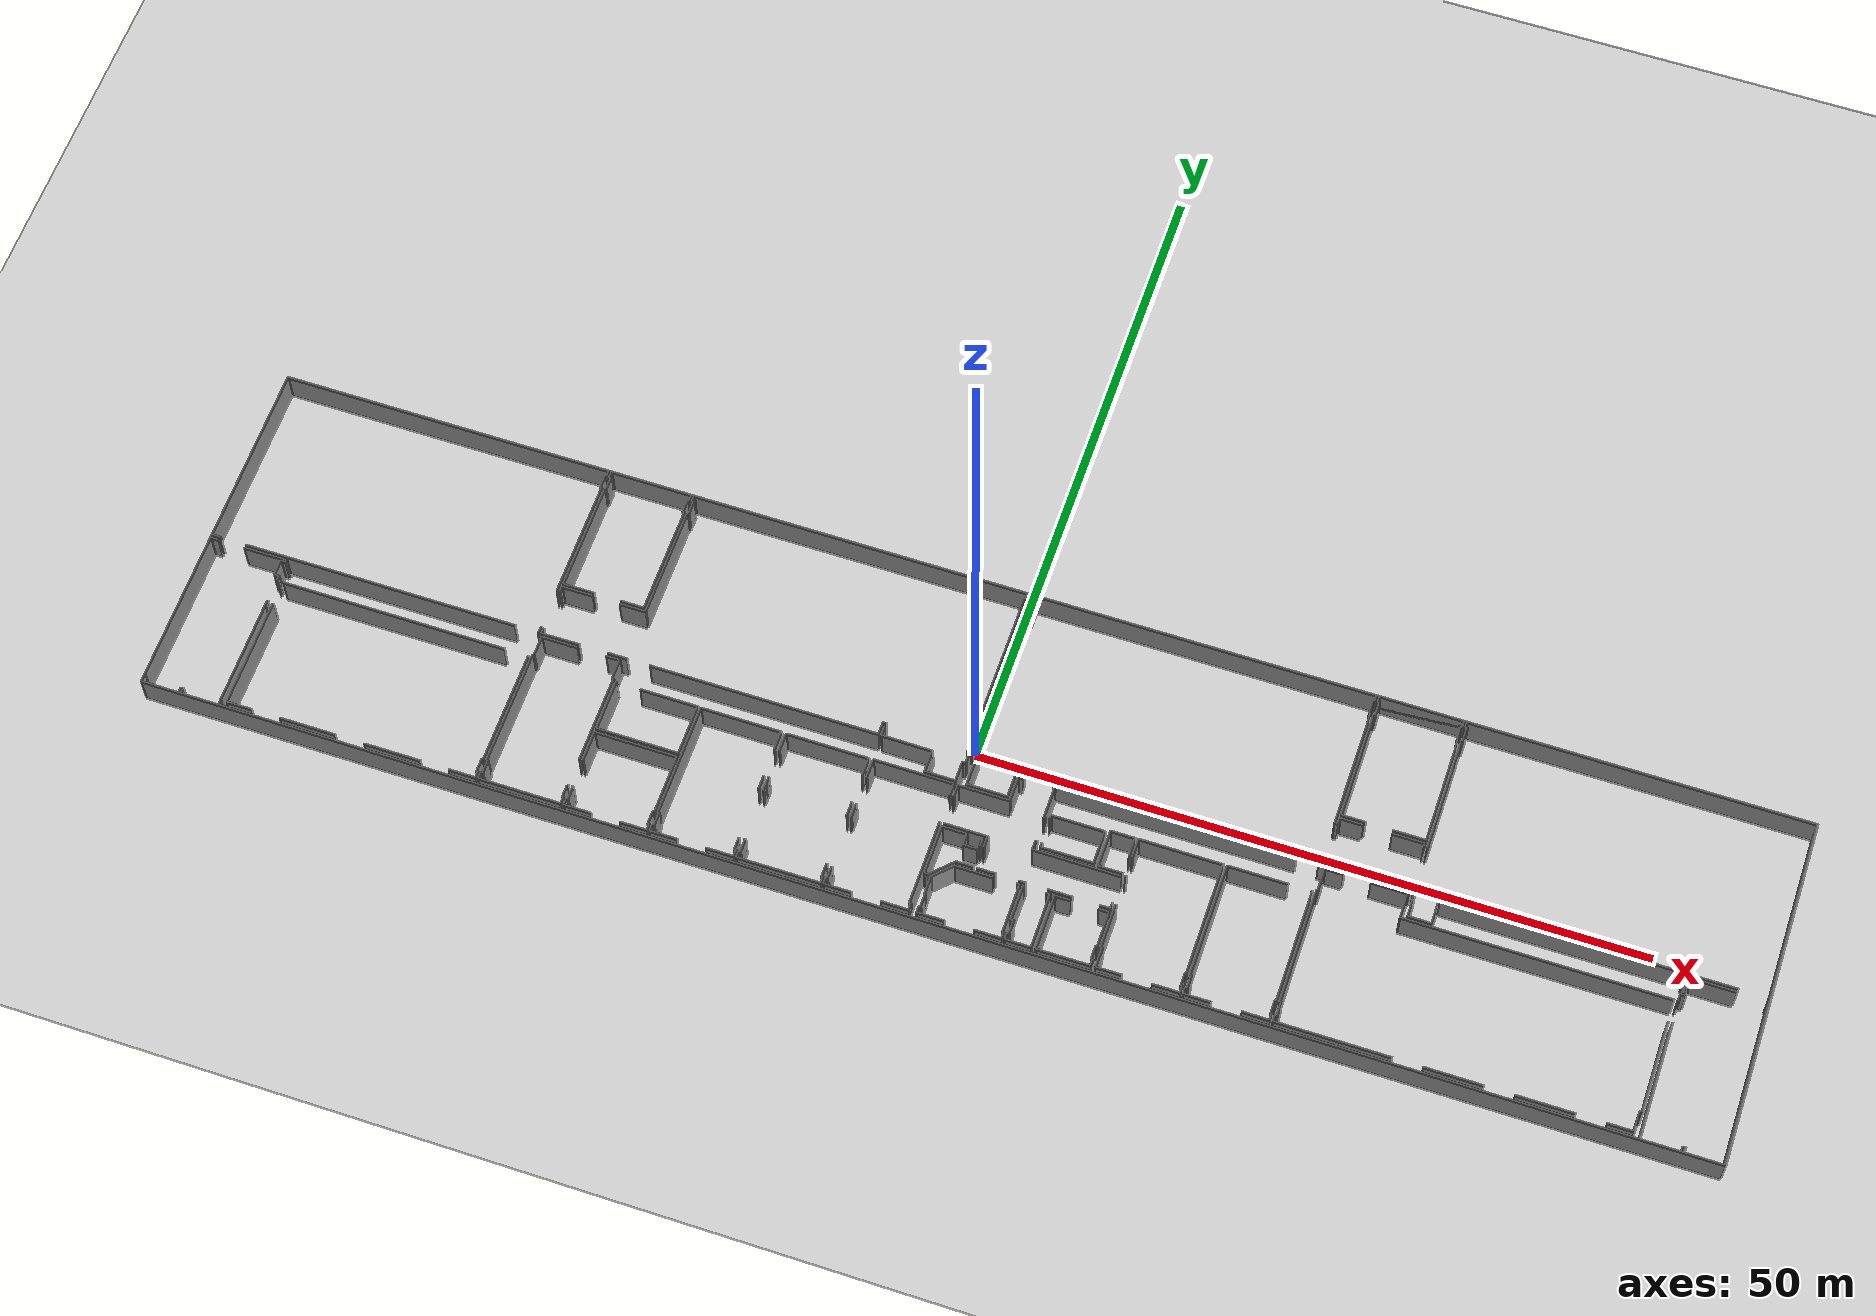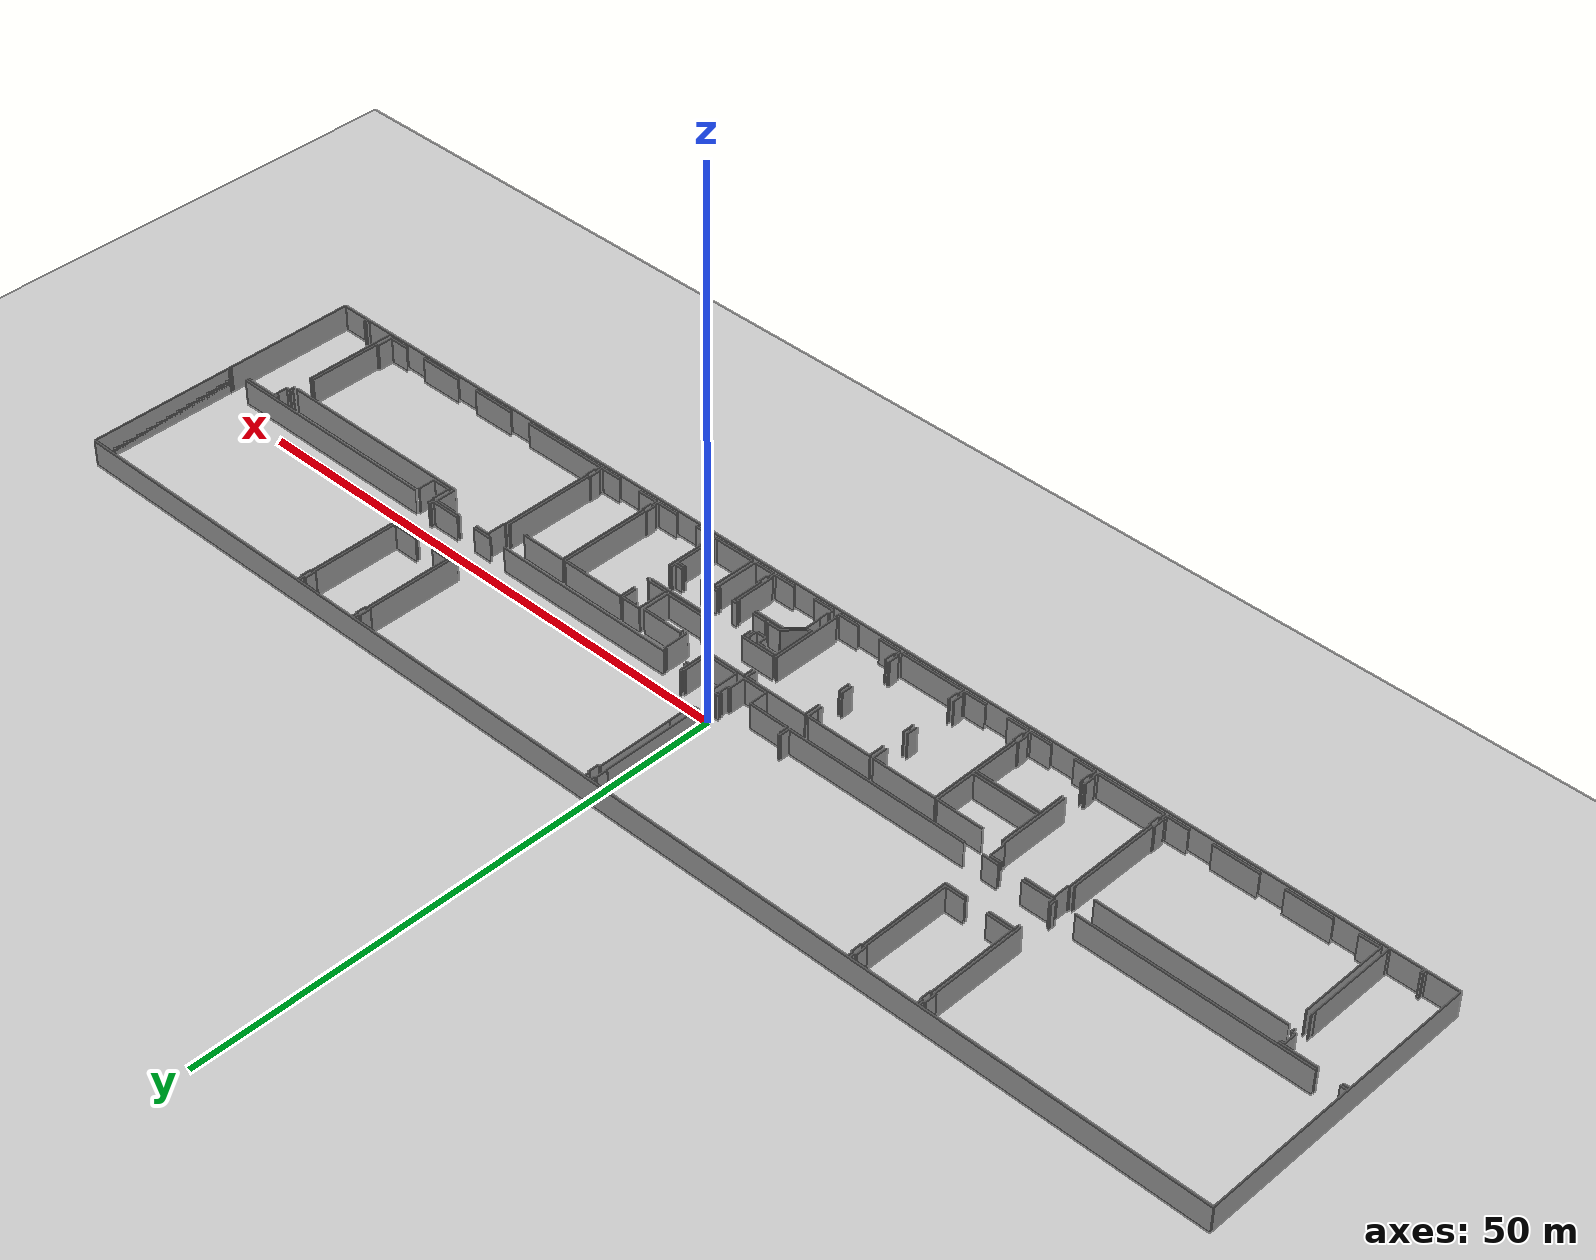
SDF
<sdf version="1.6">
  <world name="default">
    <light name="sun" type="directional">
      <cast_shadows>1</cast_shadows>
      <pose frame="">0 0 10 0 -0 0</pose>
      <diffuse>0.8 0.8 0.8 1</diffuse>
      <specular>0.1 0.1 0.1 1</specular>
      <attenuation>
        <range>1000</range>
        <constant>0.9</constant>
        <linear>0.01</linear>
        <quadratic>0.001</quadratic>
      </attenuation>
      <direction>-0.5 0.5 -1</direction>
    </light>
    <model name="ground_plane">
      <static>1</static>
      <link name="link">
        <collision name="collision">
          <geometry>
            <plane>
              <normal>0 0 1</normal>
              <size>100 100</size>
            </plane>
          </geometry>
          <surface>
            <friction>
              <ode>
                <mu>100</mu>
                <mu2>50</mu2>
              </ode>
              <torsional>
                <ode />
              </torsional>
            </friction>
            <contact>
              <ode />
            </contact>
            <bounce />
          </surface>
          <max_contacts>10</max_contacts>
        </collision>
        <visual name="visual">
          <cast_shadows>0</cast_shadows>
          <geometry>
            <plane>
              <normal>0 0 1</normal>
              <size>100 100</size>
            </plane>
          </geometry>
          <material>
            <script>
              <uri>file://media/materials/scripts/gazebo.material</uri>
              <name>Gazebo/Grey</name>
            </script>
          </material>
        </visual>
        <self_collide>0</self_collide>
        <kinematic>0</kinematic>
        <gravity>1</gravity>
      </link>
    </model>
    <gravity>0 0 -9.8</gravity>
    <magnetic_field>6e-06 2.3e-05 -4.2e-05</magnetic_field>
    <atmosphere type="adiabatic" />
    <physics default="0" name="default_physics" type="ode">
      <max_step_size>0.001</max_step_size>
      <real_time_factor>1</real_time_factor>
      <real_time_update_rate>1000</real_time_update_rate>
    </physics>
    <scene>
      <ambient>0.4 0.4 0.4 1</ambient>
      <background>0.7 0.7 0.7 1</background>
      <shadows>1</shadows>
    </scene>
    <spherical_coordinates>
      <surface_model>EARTH_WGS84</surface_model>
      <latitude_deg>0</latitude_deg>
      <longitude_deg>0</longitude_deg>
      <elevation>0</elevation>
      <heading_deg>0</heading_deg>
    </spherical_coordinates>
  <model name="0510040941_A-40">
		<static>1</static>
		<link name="Wall_0">
			<collision name="Wall_0_Collision">
				<geometry>
					<box>
						<size>14.2707666161 0.1 2.5</size>
					</box>
				</geometry>
				<pose frame="">7.13538330807 0 1.25 0 0 0</pose>
			</collision>
			<visual name="Wall_0_Visual">
				<pose frame="">7.13538330807 0 1.25 0 0 0</pose>
				<geometry>
					<box>
						<size>14.2707666161 0.1 2.5</size>
					</box>
				</geometry>
				<material>
					<script>
						<uri>file://media/materials/scripts/gazebo.material</uri>
						<name>Gazebo/Grey</name>
					</script>
					<ambient>1 1 1 1</ambient>
				</material>
			</visual>
			<pose frame="">0.0133170147058 -14.2916933535 0 0 0 1.57079632679</pose>
		</link>
		<link name="Wall_1">
			<collision name="Wall_1_Collision">
				<geometry>
					<box>
						<size>25.6027851585 0.1 2.5</size>
					</box>
				</geometry>
				<pose frame="">12.8013925793 0 1.25 0 0 0</pose>
			</collision>
			<visual name="Wall_1_Visual">
				<pose frame="">12.8013925793 0 1.25 0 0 0</pose>
				<geometry>
					<box>
						<size>25.6027851585 0.1 2.5</size>
					</box>
				</geometry>
				<material>
					<script>
						<uri>file://media/materials/scripts/gazebo.material</uri>
						<name>Gazebo/Grey</name>
					</script>
					<ambient>1 1 1 1</ambient>
				</material>
			</visual>
			<pose frame="">0.0133170147058 -0.0209267373948 0 0 0 0.0</pose>
		</link>
		<link name="Wall_2">
			<collision name="Wall_2_Collision">
				<geometry>
					<box>
						<size>0.474212552238 0.1 2.5</size>
					</box>
				</geometry>
				<pose frame="">0.237106276119 0 1.25 0 0 0</pose>
			</collision>
			<visual name="Wall_2_Visual">
				<pose frame="">0.237106276119 0 1.25 0 0 0</pose>
				<geometry>
					<box>
						<size>0.474212552238 0.1 2.5</size>
					</box>
				</geometry>
				<material>
					<script>
						<uri>file://media/materials/scripts/gazebo.material</uri>
						<name>Gazebo/Grey</name>
					</script>
					<ambient>1 1 1 1</ambient>
				</material>
			</visual>
			<pose frame="">25.6161021732 -0.0209267373948 0 0 0 -1.57079632679</pose>
		</link>
		<link name="Wall_3">
			<collision name="Wall_3_Collision">
				<geometry>
					<box>
						<size>0.125179938234 0.1 2.5</size>
					</box>
				</geometry>
				<pose frame="">0.0625899691172 0 1.25 0 0 0</pose>
			</collision>
			<visual name="Wall_3_Visual">
				<pose frame="">0.0625899691172 0 1.25 0 0 0</pose>
				<geometry>
					<box>
						<size>0.125179938234 0.1 2.5</size>
					</box>
				</geometry>
				<material>
					<script>
						<uri>file://media/materials/scripts/gazebo.material</uri>
						<name>Gazebo/Grey</name>
					</script>
					<ambient>1 1 1 1</ambient>
				</material>
			</visual>
			<pose frame="">25.6161021732 -0.495139289632 0 0 0 3.14159265359</pose>
		</link>
		<link name="Wall_4">
			<collision name="Wall_4_Collision">
				<geometry>
					<box>
						<size>1.06472703291 0.1 2.5</size>
					</box>
				</geometry>
				<pose frame="">0.532363516453 0 1.25 0 0 0</pose>
			</collision>
			<visual name="Wall_4_Visual">
				<pose frame="">0.532363516453 0 1.25 0 0 0</pose>
				<geometry>
					<box>
						<size>1.06472703291 0.1 2.5</size>
					</box>
				</geometry>
				<material>
					<script>
						<uri>file://media/materials/scripts/gazebo.material</uri>
						<name>Gazebo/Grey</name>
					</script>
					<ambient>1 1 1 1</ambient>
				</material>
			</visual>
			<pose frame="">25.490922235 -0.495139289632 0 0 0 -1.57079632679</pose>
		</link>
		<link name="Wall_5">
			<collision name="Wall_5_Collision">
				<geometry>
					<box>
						<size>0.106916603781 0.1 2.5</size>
					</box>
				</geometry>
				<pose frame="">0.0534583018904 0 1.25 0 0 0</pose>
			</collision>
			<visual name="Wall_5_Visual">
				<pose frame="">0.0534583018904 0 1.25 0 0 0</pose>
				<geometry>
					<box>
						<size>0.106916603781 0.1 2.5</size>
					</box>
				</geometry>
				<material>
					<script>
						<uri>file://media/materials/scripts/gazebo.material</uri>
						<name>Gazebo/Grey</name>
					</script>
					<ambient>1 1 1 1</ambient>
				</material>
			</visual>
			<pose frame="">25.490922235 -1.55986632254 0 0 0 0.0</pose>
		</link>
		<link name="Wall_6">
			<collision name="Wall_6_Collision">
				<geometry>
					<box>
						<size>9.09247715498 0.1 2.5</size>
					</box>
				</geometry>
				<pose frame="">4.54623857749 0 1.25 0 0 0</pose>
			</collision>
			<visual name="Wall_6_Visual">
				<pose frame="">4.54623857749 0 1.25 0 0 0</pose>
				<geometry>
					<box>
						<size>9.09247715498 0.1 2.5</size>
					</box>
				</geometry>
				<material>
					<script>
						<uri>file://media/materials/scripts/gazebo.material</uri>
						<name>Gazebo/Grey</name>
					</script>
					<ambient>1 1 1 1</ambient>
				</material>
			</visual>
			<pose frame="">25.5978388388 -1.55986632254 0 0 0 -1.57079632679</pose>
		</link>
		<link name="Wall_7">
			<collision name="Wall_7_Collision">
				<geometry>
					<box>
						<size>0.529383041733 0.1 2.5</size>
					</box>
				</geometry>
				<pose frame="">0.264691520866 0 1.25 0 0 0</pose>
			</collision>
			<visual name="Wall_7_Visual">
				<pose frame="">0.264691520866 0 1.25 0 0 0</pose>
				<geometry>
					<box>
						<size>0.529383041733 0.1 2.5</size>
					</box>
				</geometry>
				<material>
					<script>
						<uri>file://media/materials/scripts/gazebo.material</uri>
						<name>Gazebo/Grey</name>
					</script>
					<ambient>1 1 1 1</ambient>
				</material>
			</visual>
			<pose frame="">25.5978388388 -13.7612956821 0 0 0 -1.57079632679</pose>
		</link>
		<link name="Wall_8">
			<collision name="Wall_8_Collision">
				<geometry>
					<box>
						<size>0.0811703753496 0.1 2.5</size>
					</box>
				</geometry>
				<pose frame="">0.0405851876748 0 1.25 0 0 0</pose>
			</collision>
			<visual name="Wall_8_Visual">
				<pose frame="">0.0405851876748 0 1.25 0 0 0</pose>
				<geometry>
					<box>
						<size>0.0811703753496 0.1 2.5</size>
					</box>
				</geometry>
				<material>
					<script>
						<uri>file://media/materials/scripts/gazebo.material</uri>
						<name>Gazebo/Grey</name>
					</script>
					<ambient>1 1 1 1</ambient>
				</material>
			</visual>
			<pose frame="">25.5978388388 -14.2906787238 0 0 0 3.14159265359</pose>
		</link>
		<link name="Wall_9">
			<collision name="Wall_9_Collision">
				<geometry>
					<box>
						<size>21.0982098127 0.1 2.5</size>
					</box>
				</geometry>
				<pose frame="">10.5491049064 0 1.25 0 0 0</pose>
			</collision>
			<visual name="Wall_9_Visual">
				<pose frame="">10.5491049064 0 1.25 0 0 0</pose>
				<geometry>
					<box>
						<size>21.0982098127 0.1 2.5</size>
					</box>
				</geometry>
				<material>
					<script>
						<uri>file://media/materials/scripts/gazebo.material</uri>
						<name>Gazebo/Grey</name>
					</script>
					<ambient>1 1 1 1</ambient>
				</material>
			</visual>
			<pose frame="">23.7647834717 -14.2906787238 0 0 0 3.14159265359</pose>
		</link>
		<link name="Wall_10">
			<collision name="Wall_10_Collision">
				<geometry>
					<box>
						<size>0.639724825346 0.1 2.5</size>
					</box>
				</geometry>
				<pose frame="">0.319862412673 0 1.25 0 0 0</pose>
			</collision>
			<visual name="Wall_10_Visual">
				<pose frame="">0.319862412673 0 1.25 0 0 0</pose>
				<geometry>
					<box>
						<size>0.639724825346 0.1 2.5</size>
					</box>
				</geometry>
				<material>
					<script>
						<uri>file://media/materials/scripts/gazebo.material</uri>
						<name>Gazebo/Grey</name>
					</script>
					<ambient>1 1 1 1</ambient>
				</material>
			</visual>
			<pose frame="">0.65304103543 -14.2906787238 0 0 0 -3.1400066121</pose>
		</link>
		<link name="Wall_11">
			<collision name="Wall_11_Collision">
				<geometry>
					<box>
						<size>11.9235476527 0.1 2.5</size>
					</box>
				</geometry>
				<pose frame="">5.96177382636 0 1.25 0 0 0</pose>
			</collision>
			<visual name="Wall_11_Visual">
				<pose frame="">5.96177382636 0 1.25 0 0 0</pose>
				<geometry>
					<box>
						<size>11.9235476527 0.1 2.5</size>
					</box>
				</geometry>
				<material>
					<script>
						<uri>file://media/materials/scripts/gazebo.material</uri>
						<name>Gazebo/Grey</name>
					</script>
					<ambient>1 1 1 1</ambient>
				</material>
			</visual>
			<pose frame="">0.00596094943974 -26.4680106282 0 0 0 1.57079632679</pose>
		</link>
		<link name="Wall_12">
			<collision name="Wall_12_Collision">
				<geometry>
					<box>
						<size>0.609158301256 0.1 2.5</size>
					</box>
				</geometry>
				<pose frame="">0.304579150628 0 1.25 0 0 0</pose>
			</collision>
			<visual name="Wall_12_Visual">
				<pose frame="">0.304579150628 0 1.25 0 0 0</pose>
				<geometry>
					<box>
						<size>0.609158301256 0.1 2.5</size>
					</box>
				</geometry>
				<material>
					<script>
						<uri>file://media/materials/scripts/gazebo.material</uri>
						<name>Gazebo/Grey</name>
					</script>
					<ambient>1 1 1 1</ambient>
				</material>
			</visual>
			<pose frame="">0.00596094943974 -14.5444629755 0 0 0 0.0</pose>
		</link>
		<link name="Wall_13">
			<collision name="Wall_13_Collision">
				<geometry>
					<box>
						<size>3.33369268135 0.1 2.5</size>
					</box>
				</geometry>
				<pose frame="">1.66684634067 0 1.25 0 0 0</pose>
			</collision>
			<visual name="Wall_13_Visual">
				<pose frame="">1.66684634067 0 1.25 0 0 0</pose>
				<geometry>
					<box>
						<size>3.33369268135 0.1 2.5</size>
					</box>
				</geometry>
				<material>
					<script>
						<uri>file://media/materials/scripts/gazebo.material</uri>
						<name>Gazebo/Grey</name>
					</script>
					<ambient>1 1 1 1</ambient>
				</material>
			</visual>
			<pose frame="">2.66010539466 -14.5444629755 0 0 0 0.0</pose>
		</link>
		<link name="Wall_14">
			<collision name="Wall_14_Collision">
				<geometry>
					<box>
						<size>0.155999315125 0.1 2.5</size>
					</box>
				</geometry>
				<pose frame="">0.0779996575625 0 1.25 0 0 0</pose>
			</collision>
			<visual name="Wall_14_Visual">
				<pose frame="">0.0779996575625 0 1.25 0 0 0</pose>
				<geometry>
					<box>
						<size>0.155999315125 0.1 2.5</size>
					</box>
				</geometry>
				<material>
					<script>
						<uri>file://media/materials/scripts/gazebo.material</uri>
						<name>Gazebo/Grey</name>
					</script>
					<ambient>1 1 1 1</ambient>
				</material>
			</visual>
			<pose frame="">5.99379807601 -14.5444629755 0 0 0 -1.57079632679</pose>
		</link>
		<link name="Wall_15">
			<collision name="Wall_15_Collision">
				<geometry>
					<box>
						<size>0.359305739633 0.1 2.5</size>
					</box>
				</geometry>
				<pose frame="">0.179652869817 0 1.25 0 0 0</pose>
			</collision>
			<visual name="Wall_15_Visual">
				<pose frame="">0.179652869817 0 1.25 0 0 0</pose>
				<geometry>
					<box>
						<size>0.359305739633 0.1 2.5</size>
					</box>
				</geometry>
				<material>
					<script>
						<uri>file://media/materials/scripts/gazebo.material</uri>
						<name>Gazebo/Grey</name>
					</script>
					<ambient>1 1 1 1</ambient>
				</material>
			</visual>
			<pose frame="">5.99379807601 -14.7004622907 0 0 0 3.14159265359</pose>
		</link>
		<link name="Wall_16">
			<collision name="Wall_16_Collision">
				<geometry>
					<box>
						<size>1.24165308543 0.1 2.5</size>
					</box>
				</geometry>
				<pose frame="">0.620826542713 0 1.25 0 0 0</pose>
			</collision>
			<visual name="Wall_16_Visual">
				<pose frame="">0.620826542713 0 1.25 0 0 0</pose>
				<geometry>
					<box>
						<size>1.24165308543 0.1 2.5</size>
					</box>
				</geometry>
				<material>
					<script>
						<uri>file://media/materials/scripts/gazebo.material</uri>
						<name>Gazebo/Grey</name>
					</script>
					<ambient>1 1 1 1</ambient>
				</material>
			</visual>
			<pose frame="">5.63449233638 -14.7004622907 0 0 0 -1.57079632679</pose>
		</link>
		<link name="Wall_17">
			<collision name="Wall_17_Collision">
				<geometry>
					<box>
						<size>0.360954512883 0.1 2.5</size>
					</box>
				</geometry>
				<pose frame="">0.180477256441 0 1.25 0 0 0</pose>
			</collision>
			<visual name="Wall_17_Visual">
				<pose frame="">0.180477256441 0 1.25 0 0 0</pose>
				<geometry>
					<box>
						<size>0.360954512883 0.1 2.5</size>
					</box>
				</geometry>
				<material>
					<script>
						<uri>file://media/materials/scripts/gazebo.material</uri>
						<name>Gazebo/Grey</name>
					</script>
					<ambient>1 1 1 1</ambient>
				</material>
			</visual>
			<pose frame="">5.63449233638 -15.9421153761 0 0 0 0.0</pose>
		</link>
		<link name="Wall_18">
			<collision name="Wall_18_Collision">
				<geometry>
					<box>
						<size>0.367422777168 0.1 2.5</size>
					</box>
				</geometry>
				<pose frame="">0.183711388584 0 1.25 0 0 0</pose>
			</collision>
			<visual name="Wall_18_Visual">
				<pose frame="">0.183711388584 0 1.25 0 0 0</pose>
				<geometry>
					<box>
						<size>0.367422777168 0.1 2.5</size>
					</box>
				</geometry>
				<material>
					<script>
						<uri>file://media/materials/scripts/gazebo.material</uri>
						<name>Gazebo/Grey</name>
					</script>
					<ambient>1 1 1 1</ambient>
				</material>
			</visual>
			<pose frame="">5.99544684926 -15.9421153761 0 0 0 -1.57079632679</pose>
		</link>
		<link name="Wall_19">
			<collision name="Wall_19_Collision">
				<geometry>
					<box>
						<size>0.456837018764 0.1 2.5</size>
					</box>
				</geometry>
				<pose frame="">0.228418509382 0 1.25 0 0 0</pose>
			</collision>
			<visual name="Wall_19_Visual">
				<pose frame="">0.228418509382 0 1.25 0 0 0</pose>
				<geometry>
					<box>
						<size>0.456837018764 0.1 2.5</size>
					</box>
				</geometry>
				<material>
					<script>
						<uri>file://media/materials/scripts/gazebo.material</uri>
						<name>Gazebo/Grey</name>
					</script>
					<ambient>1 1 1 1</ambient>
				</material>
			</visual>
			<pose frame="">5.99544684926 -18.0831108546 0 0 0 -1.57079632679</pose>
		</link>
		<link name="Wall_20">
			<collision name="Wall_20_Collision">
				<geometry>
					<box>
						<size>8.16523244532 0.1 2.5</size>
					</box>
				</geometry>
				<pose frame="">4.08261622266 0 1.25 0 0 0</pose>
			</collision>
			<visual name="Wall_20_Visual">
				<pose frame="">4.08261622266 0 1.25 0 0 0</pose>
				<geometry>
					<box>
						<size>8.16523244532 0.1 2.5</size>
					</box>
				</geometry>
				<material>
					<script>
						<uri>file://media/materials/scripts/gazebo.material</uri>
						<name>Gazebo/Grey</name>
					</script>
					<ambient>1 1 1 1</ambient>
				</material>
			</visual>
			<pose frame="">5.99544684926 -18.5399478734 0 0 0 -1.57079632679</pose>
		</link>
		<link name="Wall_21">
			<collision name="Wall_21_Collision">
				<geometry>
					<box>
						<size>0.37528615728 0.1 2.5</size>
					</box>
				</geometry>
				<pose frame="">0.18764307864 0 1.25 0 0 0</pose>
			</collision>
			<visual name="Wall_21_Visual">
				<pose frame="">0.18764307864 0 1.25 0 0 0</pose>
				<geometry>
					<box>
						<size>0.37528615728 0.1 2.5</size>
					</box>
				</geometry>
				<material>
					<script>
						<uri>file://media/materials/scripts/gazebo.material</uri>
						<name>Gazebo/Grey</name>
					</script>
					<ambient>1 1 1 1</ambient>
				</material>
			</visual>
			<pose frame="">5.99544684926 -26.7051803187 0 0 0 -1.57079632679</pose>
		</link>
		<link name="Wall_22">
			<collision name="Wall_22_Collision">
				<geometry>
					<box>
						<size>0.399003126328 0.1 2.5</size>
					</box>
				</geometry>
				<pose frame="">0.199501563164 0 1.25 0 0 0</pose>
			</collision>
			<visual name="Wall_22_Visual">
				<pose frame="">0.199501563164 0 1.25 0 0 0</pose>
				<geometry>
					<box>
						<size>0.399003126328 0.1 2.5</size>
					</box>
				</geometry>
				<material>
					<script>
						<uri>file://media/materials/scripts/gazebo.material</uri>
						<name>Gazebo/Grey</name>
					</script>
					<ambient>1 1 1 1</ambient>
				</material>
			</visual>
			<pose frame="">3.09918639382 -27.080466476 0 0 0 1.57079632679</pose>
		</link>
		<link name="Wall_23">
			<collision name="Wall_23_Collision">
				<geometry>
					<box>
						<size>0.195443044396 0.1 2.5</size>
					</box>
				</geometry>
				<pose frame="">0.0977215221982 0 1.25 0 0 0</pose>
			</collision>
			<visual name="Wall_23_Visual">
				<pose frame="">0.0977215221982 0 1.25 0 0 0</pose>
				<geometry>
					<box>
						<size>0.195443044396 0.1 2.5</size>
					</box>
				</geometry>
				<material>
					<script>
						<uri>file://media/materials/scripts/gazebo.material</uri>
						<name>Gazebo/Grey</name>
					</script>
					<ambient>1 1 1 1</ambient>
				</material>
			</visual>
			<pose frame="">3.09918639382 -26.6814633497 0 0 0 3.14159265359</pose>
		</link>
		<link name="Wall_24">
			<collision name="Wall_24_Collision">
				<geometry>
					<box>
						<size>0.400525070866 0.1 2.5</size>
					</box>
				</geometry>
				<pose frame="">0.200262535433 0 1.25 0 0 0</pose>
			</collision>
			<visual name="Wall_24_Visual">
				<pose frame="">0.200262535433 0 1.25 0 0 0</pose>
				<geometry>
					<box>
						<size>0.400525070866 0.1 2.5</size>
					</box>
				</geometry>
				<material>
					<script>
						<uri>file://media/materials/scripts/gazebo.material</uri>
						<name>Gazebo/Grey</name>
					</script>
					<ambient>1 1 1 1</ambient>
				</material>
			</visual>
			<pose frame="">2.90374334942 -26.6814633497 0 0 0 -1.57079632679</pose>
		</link>
		<link name="Wall_25">
			<collision name="Wall_25_Collision">
				<geometry>
					<box>
						<size>0.614006728259 0.1 2.5</size>
					</box>
				</geometry>
				<pose frame="">0.307003364129 0 1.25 0 0 0</pose>
			</collision>
			<visual name="Wall_25_Visual">
				<pose frame="">0.307003364129 0 1.25 0 0 0</pose>
				<geometry>
					<box>
						<size>0.614006728259 0.1 2.5</size>
					</box>
				</geometry>
				<material>
					<script>
						<uri>file://media/materials/scripts/gazebo.material</uri>
						<name>Gazebo/Grey</name>
					</script>
					<ambient>1 1 1 1</ambient>
				</material>
			</visual>
			<pose frame="">0.0 -27.0819884205 0 0 0 1.56108789396</pose>
		</link>
		<link name="Wall_26">
			<collision name="Wall_26_Collision">
				<geometry>
					<box>
						<size>8.49384563678 0.1 2.5</size>
					</box>
				</geometry>
				<pose frame="">4.24692281839 0 1.25 0 0 0</pose>
			</collision>
			<visual name="Wall_26_Visual">
				<pose frame="">4.24692281839 0 1.25 0 0 0</pose>
				<geometry>
					<box>
						<size>8.49384563678 0.1 2.5</size>
					</box>
				</geometry>
				<material>
					<script>
						<uri>file://media/materials/scripts/gazebo.material</uri>
						<name>Gazebo/Grey</name>
					</script>
					<ambient>1 1 1 1</ambient>
				</material>
			</visual>
			<pose frame="">6.48589347657 -26.6884389288 0 0 0 1.57079632679</pose>
		</link>
		<link name="Wall_27">
			<collision name="Wall_27_Collision">
				<geometry>
					<box>
						<size>17.2592315448 0.1 2.5</size>
					</box>
				</geometry>
				<pose frame="">8.62961577242 0 1.25 0 0 0</pose>
			</collision>
			<visual name="Wall_27_Visual">
				<pose frame="">8.62961577242 0 1.25 0 0 0</pose>
				<geometry>
					<box>
						<size>17.2592315448 0.1 2.5</size>
					</box>
				</geometry>
				<material>
					<script>
						<uri>file://media/materials/scripts/gazebo.material</uri>
						<name>Gazebo/Grey</name>
					</script>
					<ambient>1 1 1 1</ambient>
				</material>
			</visual>
			<pose frame="">6.48589347657 -16.3312258629 0 0 0 0.0</pose>
		</link>
		<link name="Wall_28">
			<collision name="Wall_28_Collision">
				<geometry>
					<box>
						<size>0.0575802350136 0.1 2.5</size>
					</box>
				</geometry>
				<pose frame="">0.0287901175068 0 1.25 0 0 0</pose>
			</collision>
			<visual name="Wall_28_Visual">
				<pose frame="">0.0287901175068 0 1.25 0 0 0</pose>
				<geometry>
					<box>
						<size>0.0575802350136 0.1 2.5</size>
					</box>
				</geometry>
				<material>
					<script>
						<uri>file://media/materials/scripts/gazebo.material</uri>
						<name>Gazebo/Grey</name>
					</script>
					<ambient>1 1 1 1</ambient>
				</material>
			</visual>
			<pose frame="">25.5384830018 -16.3312258629 0 0 0 0.0</pose>
		</link>
		<link name="Wall_29">
			<collision name="Wall_29_Collision">
				<geometry>
					<box>
						<size>8.79252725232 0.1 2.5</size>
					</box>
				</geometry>
				<pose frame="">4.39626362616 0 1.25 0 0 0</pose>
			</collision>
			<visual name="Wall_29_Visual">
				<pose frame="">4.39626362616 0 1.25 0 0 0</pose>
				<geometry>
					<box>
						<size>8.79252725232 0.1 2.5</size>
					</box>
				</geometry>
				<material>
					<script>
						<uri>file://media/materials/scripts/gazebo.material</uri>
						<name>Gazebo/Grey</name>
					</script>
					<ambient>1 1 1 1</ambient>
				</material>
			</visual>
			<pose frame="">25.5960632368 -16.3312258629 0 0 0 -1.57079632679</pose>
		</link>
		<link name="Wall_30">
			<collision name="Wall_30_Collision">
				<geometry>
					<box>
						<size>0.111482437394 0.1 2.5</size>
					</box>
				</geometry>
				<pose frame="">0.0557412186971 0 1.25 0 0 0</pose>
			</collision>
			<visual name="Wall_30_Visual">
				<pose frame="">0.0557412186971 0 1.25 0 0 0</pose>
				<geometry>
					<box>
						<size>0.111482437394 0.1 2.5</size>
					</box>
				</geometry>
				<material>
					<script>
						<uri>file://media/materials/scripts/gazebo.material</uri>
						<name>Gazebo/Grey</name>
					</script>
					<ambient>1 1 1 1</ambient>
				</material>
			</visual>
			<pose frame="">25.5960632368 -25.1237531152 0 0 0 3.14159265359</pose>
		</link>
		<link name="Wall_31">
			<collision name="Wall_31_Collision">
				<geometry>
					<box>
						<size>1.05927339831 0.1 2.5</size>
					</box>
				</geometry>
				<pose frame="">0.529636699156 0 1.25 0 0 0</pose>
			</collision>
			<visual name="Wall_31_Visual">
				<pose frame="">0.529636699156 0 1.25 0 0 0</pose>
				<geometry>
					<box>
						<size>1.05927339831 0.1 2.5</size>
					</box>
				</geometry>
				<material>
					<script>
						<uri>file://media/materials/scripts/gazebo.material</uri>
						<name>Gazebo/Grey</name>
					</script>
					<ambient>1 1 1 1</ambient>
				</material>
			</visual>
			<pose frame="">25.4845807994 -25.1237531152 0 0 0 -1.57079632679</pose>
		</link>
		<link name="Wall_32">
			<collision name="Wall_32_Collision">
				<geometry>
					<box>
						<size>0.119726303641 0.1 2.5</size>
					</box>
				</geometry>
				<pose frame="">0.0598631518203 0 1.25 0 0 0</pose>
			</collision>
			<visual name="Wall_32_Visual">
				<pose frame="">0.0598631518203 0 1.25 0 0 0</pose>
				<geometry>
					<box>
						<size>0.119726303641 0.1 2.5</size>
					</box>
				</geometry>
				<material>
					<script>
						<uri>file://media/materials/scripts/gazebo.material</uri>
						<name>Gazebo/Grey</name>
					</script>
					<ambient>1 1 1 1</ambient>
				</material>
			</visual>
			<pose frame="">25.4845807994 -26.1830265135 0 0 0 0.0</pose>
		</link>
		<link name="Wall_33">
			<collision name="Wall_33_Collision">
				<geometry>
					<box>
						<size>0.47865155714 0.1 2.5</size>
					</box>
				</geometry>
				<pose frame="">0.23932577857 0 1.25 0 0 0</pose>
			</collision>
			<visual name="Wall_33_Visual">
				<pose frame="">0.23932577857 0 1.25 0 0 0</pose>
				<geometry>
					<box>
						<size>0.47865155714 0.1 2.5</size>
					</box>
				</geometry>
				<material>
					<script>
						<uri>file://media/materials/scripts/gazebo.material</uri>
						<name>Gazebo/Grey</name>
					</script>
					<ambient>1 1 1 1</ambient>
				</material>
			</visual>
			<pose frame="">25.604307103 -26.1830265135 0 0 0 -1.57079632679</pose>
		</link>
		<link name="Wall_34">
			<collision name="Wall_34_Collision">
				<geometry>
					<box>
						<size>2.05728852898 0.1 2.5</size>
					</box>
				</geometry>
				<pose frame="">1.02864426449 0 1.25 0 0 0</pose>
			</collision>
			<visual name="Wall_34_Visual">
				<pose frame="">1.02864426449 0 1.25 0 0 0</pose>
				<geometry>
					<box>
						<size>2.05728852898 0.1 2.5</size>
					</box>
				</geometry>
				<material>
					<script>
						<uri>file://media/materials/scripts/gazebo.material</uri>
						<name>Gazebo/Grey</name>
					</script>
					<ambient>1 1 1 1</ambient>
				</material>
			</visual>
			<pose frame="">25.604307103 -26.6616780707 0 0 0 3.14159265359</pose>
		</link>
		<link name="Wall_35">
			<collision name="Wall_35_Collision">
				<geometry>
					<box>
						<size>4.29327871243 0.1 2.5</size>
					</box>
				</geometry>
				<pose frame="">2.14663935622 0 1.25 0 0 0</pose>
			</collision>
			<visual name="Wall_35_Visual">
				<pose frame="">2.14663935622 0 1.25 0 0 0</pose>
				<geometry>
					<box>
						<size>4.29327871243 0.1 2.5</size>
					</box>
				</geometry>
				<material>
					<script>
						<uri>file://media/materials/scripts/gazebo.material</uri>
						<name>Gazebo/Grey</name>
					</script>
					<ambient>1 1 1 1</ambient>
				</material>
			</visual>
			<pose frame="">21.3733012879 -26.6616780707 0 0 0 3.14159265359</pose>
		</link>
		<link name="Wall_36">
			<collision name="Wall_36_Collision">
				<geometry>
					<box>
						<size>4.28465436005 0.1 2.5</size>
					</box>
				</geometry>
				<pose frame="">2.14232718003 0 1.25 0 0 0</pose>
			</collision>
			<visual name="Wall_36_Visual">
				<pose frame="">2.14232718003 0 1.25 0 0 0</pose>
				<geometry>
					<box>
						<size>4.28465436005 0.1 2.5</size>
					</box>
				</geometry>
				<material>
					<script>
						<uri>file://media/materials/scripts/gazebo.material</uri>
						<name>Gazebo/Grey</name>
					</script>
					<ambient>1 1 1 1</ambient>
				</material>
			</visual>
			<pose frame="">14.8501201702 -26.6616780707 0 0 0 3.14159265359</pose>
		</link>
		<link name="Wall_37">
			<collision name="Wall_37_Collision">
				<geometry>
					<box>
						<size>1.90299932949 0.1 2.5</size>
					</box>
				</geometry>
				<pose frame="">0.951499664743 0 1.25 0 0 0</pose>
			</collision>
			<visual name="Wall_37_Visual">
				<pose frame="">0.951499664743 0 1.25 0 0 0</pose>
				<geometry>
					<box>
						<size>1.90299932949 0.1 2.5</size>
					</box>
				</geometry>
				<material>
					<script>
						<uri>file://media/materials/scripts/gazebo.material</uri>
						<name>Gazebo/Grey</name>
					</script>
					<ambient>1 1 1 1</ambient>
				</material>
			</visual>
			<pose frame="">8.38870463496 -26.6616780707 0 0 0 -3.12752972682</pose>
		</link>
		<link name="Wall_38">
			<collision name="Wall_38_Collision">
				<geometry>
					<box>
						<size>8.42599227613 0.1 2.5</size>
					</box>
				</geometry>
				<pose frame="">4.21299613807 0 1.25 0 0 0</pose>
			</collision>
			<visual name="Wall_38_Visual">
				<pose frame="">4.21299613807 0 1.25 0 0 0</pose>
				<geometry>
					<box>
						<size>8.42599227613 0.1 2.5</size>
					</box>
				</geometry>
				<material>
					<script>
						<uri>file://media/materials/scripts/gazebo.material</uri>
						<name>Gazebo/Grey</name>
					</script>
					<ambient>1 1 1 1</ambient>
				</material>
			</visual>
			<pose frame="">25.8578376973 -9.9850976264 0 0 0 1.57079632679</pose>
		</link>
		<link name="Wall_39">
			<collision name="Wall_39_Collision">
				<geometry>
					<box>
						<size>0.0949947049013 0.1 2.5</size>
					</box>
				</geometry>
				<pose frame="">0.0474973524506 0 1.25 0 0 0</pose>
			</collision>
			<visual name="Wall_39_Visual">
				<pose frame="">0.0474973524506 0 1.25 0 0 0</pose>
				<geometry>
					<box>
						<size>0.0949947049013 0.1 2.5</size>
					</box>
				</geometry>
				<material>
					<script>
						<uri>file://media/materials/scripts/gazebo.material</uri>
						<name>Gazebo/Grey</name>
					</script>
					<ambient>1 1 1 1</ambient>
				</material>
			</visual>
			<pose frame="">25.8578376973 -1.55910535027 0 0 0 0.0</pose>
		</link>
		<link name="Wall_40">
			<collision name="Wall_40_Collision">
				<geometry>
					<box>
						<size>1.04062957772 0.1 2.5</size>
					</box>
				</geometry>
				<pose frame="">0.520314788862 0 1.25 0 0 0</pose>
			</collision>
			<visual name="Wall_40_Visual">
				<pose frame="">0.520314788862 0 1.25 0 0 0</pose>
				<geometry>
					<box>
						<size>1.04062957772 0.1 2.5</size>
					</box>
				</geometry>
				<material>
					<script>
						<uri>file://media/materials/scripts/gazebo.material</uri>
						<name>Gazebo/Grey</name>
					</script>
					<ambient>1 1 1 1</ambient>
				</material>
			</visual>
			<pose frame="">25.9528324022 -1.55910535027 0 0 0 1.57079632679</pose>
		</link>
		<link name="Wall_41">
			<collision name="Wall_41_Collision">
				<geometry>
					<box>
						<size>0.128477484733 0.1 2.5</size>
					</box>
				</geometry>
				<pose frame="">0.0642387423665 0 1.25 0 0 0</pose>
			</collision>
			<visual name="Wall_41_Visual">
				<pose frame="">0.0642387423665 0 1.25 0 0 0</pose>
				<geometry>
					<box>
						<size>0.128477484733 0.1 2.5</size>
					</box>
				</geometry>
				<material>
					<script>
						<uri>file://media/materials/scripts/gazebo.material</uri>
						<name>Gazebo/Grey</name>
					</script>
					<ambient>1 1 1 1</ambient>
				</material>
			</visual>
			<pose frame="">25.9528324022 -0.518475772545 0 0 0 3.14159265359</pose>
		</link>
		<link name="Wall_42">
			<collision name="Wall_42_Collision">
				<geometry>
					<box>
						<size>0.497549035151 0.1 2.5</size>
					</box>
				</geometry>
				<pose frame="">0.248774517575 0 1.25 0 0 0</pose>
			</collision>
			<visual name="Wall_42_Visual">
				<pose frame="">0.248774517575 0 1.25 0 0 0</pose>
				<geometry>
					<box>
						<size>0.497549035151 0.1 2.5</size>
					</box>
				</geometry>
				<material>
					<script>
						<uri>file://media/materials/scripts/gazebo.material</uri>
						<name>Gazebo/Grey</name>
					</script>
					<ambient>1 1 1 1</ambient>
				</material>
			</visual>
			<pose frame="">25.8243549175 -0.518475772545 0 0 0 1.57079632679</pose>
		</link>
		<link name="Wall_43">
			<collision name="Wall_43_Collision">
				<geometry>
					<box>
						<size>6.27840170458 0.1 2.5</size>
					</box>
				</geometry>
				<pose frame="">3.13920085229 0 1.25 0 0 0</pose>
			</collision>
			<visual name="Wall_43_Visual">
				<pose frame="">3.13920085229 0 1.25 0 0 0</pose>
				<geometry>
					<box>
						<size>6.27840170458 0.1 2.5</size>
					</box>
				</geometry>
				<material>
					<script>
						<uri>file://media/materials/scripts/gazebo.material</uri>
						<name>Gazebo/Grey</name>
					</script>
					<ambient>1 1 1 1</ambient>
				</material>
			</visual>
			<pose frame="">25.8243549175 -0.0209267373948 0 0 0 0.0</pose>
		</link>
		<link name="Wall_44">
			<collision name="Wall_44_Collision">
				<geometry>
					<box>
						<size>0.484485677868 0.1 2.5</size>
					</box>
				</geometry>
				<pose frame="">0.242242838934 0 1.25 0 0 0</pose>
			</collision>
			<visual name="Wall_44_Visual">
				<pose frame="">0.242242838934 0 1.25 0 0 0</pose>
				<geometry>
					<box>
						<size>0.484485677868 0.1 2.5</size>
					</box>
				</geometry>
				<material>
					<script>
						<uri>file://media/materials/scripts/gazebo.material</uri>
						<name>Gazebo/Grey</name>
					</script>
					<ambient>1 1 1 1</ambient>
				</material>
			</visual>
			<pose frame="">32.102756622 -0.0209267373948 0 0 0 -1.57079632679</pose>
		</link>
		<link name="Wall_45">
			<collision name="Wall_45_Collision">
				<geometry>
					<box>
						<size>0.128731142156 0.1 2.5</size>
					</box>
				</geometry>
				<pose frame="">0.064365571078 0 1.25 0 0 0</pose>
			</collision>
			<visual name="Wall_45_Visual">
				<pose frame="">0.064365571078 0 1.25 0 0 0</pose>
				<geometry>
					<box>
						<size>0.128731142156 0.1 2.5</size>
					</box>
				</geometry>
				<material>
					<script>
						<uri>file://media/materials/scripts/gazebo.material</uri>
						<name>Gazebo/Grey</name>
					</script>
					<ambient>1 1 1 1</ambient>
				</material>
			</visual>
			<pose frame="">32.102756622 -0.505412415263 0 0 0 3.14159265359</pose>
		</link>
		<link name="Wall_46">
			<collision name="Wall_46_Collision">
				<geometry>
					<box>
						<size>1.05990754187 0.1 2.5</size>
					</box>
				</geometry>
				<pose frame="">0.529953770935 0 1.25 0 0 0</pose>
			</collision>
			<visual name="Wall_46_Visual">
				<pose frame="">0.529953770935 0 1.25 0 0 0</pose>
				<geometry>
					<box>
						<size>1.05990754187 0.1 2.5</size>
					</box>
				</geometry>
				<material>
					<script>
						<uri>file://media/materials/scripts/gazebo.material</uri>
						<name>Gazebo/Grey</name>
					</script>
					<ambient>1 1 1 1</ambient>
				</material>
			</visual>
			<pose frame="">31.9740254799 -0.505412415263 0 0 0 -1.57079632679</pose>
		</link>
		<link name="Wall_47">
			<collision name="Wall_47_Collision">
				<geometry>
					<box>
						<size>0.121248248178 0.1 2.5</size>
					</box>
				</geometry>
				<pose frame="">0.0606241240892 0 1.25 0 0 0</pose>
			</collision>
			<visual name="Wall_47_Visual">
				<pose frame="">0.0606241240892 0 1.25 0 0 0</pose>
				<geometry>
					<box>
						<size>0.121248248178 0.1 2.5</size>
					</box>
				</geometry>
				<material>
					<script>
						<uri>file://media/materials/scripts/gazebo.material</uri>
						<name>Gazebo/Grey</name>
					</script>
					<ambient>1 1 1 1</ambient>
				</material>
			</visual>
			<pose frame="">31.9740254799 -1.56531995713 0 0 0 0.0</pose>
		</link>
		<link name="Wall_48">
			<collision name="Wall_48_Collision">
				<geometry>
					<box>
						<size>8.41064600204 0.1 2.5</size>
					</box>
				</geometry>
				<pose frame="">4.20532300102 0 1.25 0 0 0</pose>
			</collision>
			<visual name="Wall_48_Visual">
				<pose frame="">4.20532300102 0 1.25 0 0 0</pose>
				<geometry>
					<box>
						<size>8.41064600204 0.1 2.5</size>
					</box>
				</geometry>
				<material>
					<script>
						<uri>file://media/materials/scripts/gazebo.material</uri>
						<name>Gazebo/Grey</name>
					</script>
					<ambient>1 1 1 1</ambient>
				</material>
			</visual>
			<pose frame="">32.0952737281 -1.56531995713 0 0 0 -1.57079632679</pose>
		</link>
		<link name="Wall_49">
			<collision name="Wall_49_Collision">
				<geometry>
					<box>
						<size>1.80705548122 0.1 2.5</size>
					</box>
				</geometry>
				<pose frame="">0.90352774061 0 1.25 0 0 0</pose>
			</collision>
			<visual name="Wall_49_Visual">
				<pose frame="">0.90352774061 0 1.25 0 0 0</pose>
				<geometry>
					<box>
						<size>1.80705548122 0.1 2.5</size>
					</box>
				</geometry>
				<material>
					<script>
						<uri>file://media/materials/scripts/gazebo.material</uri>
						<name>Gazebo/Grey</name>
					</script>
					<ambient>1 1 1 1</ambient>
				</material>
			</visual>
			<pose frame="">32.0952737281 -9.97596595917 0 0 0 3.14159265359</pose>
		</link>
		<link name="Wall_50">
			<collision name="Wall_50_Collision">
				<geometry>
					<box>
						<size>2.38503140091 0.1 2.5</size>
					</box>
				</geometry>
				<pose frame="">1.19251570045 0 1.25 0 0 0</pose>
			</collision>
			<visual name="Wall_50_Visual">
				<pose frame="">1.19251570045 0 1.25 0 0 0</pose>
				<geometry>
					<box>
						<size>2.38503140091 0.1 2.5</size>
					</box>
				</geometry>
				<material>
					<script>
						<uri>file://media/materials/scripts/gazebo.material</uri>
						<name>Gazebo/Grey</name>
					</script>
					<ambient>1 1 1 1</ambient>
				</material>
			</visual>
			<pose frame="">28.2428516167 -9.97596595917 0 0 0 -3.13776390335</pose>
		</link>
		<link name="Wall_51">
			<collision name="Wall_51_Collision">
				<geometry>
					<box>
						<size>0.412320141034 0.1 2.5</size>
					</box>
				</geometry>
				<pose frame="">0.206160070517 0 1.25 0 0 0</pose>
			</collision>
			<visual name="Wall_51_Visual">
				<pose frame="">0.206160070517 0 1.25 0 0 0</pose>
				<geometry>
					<box>
						<size>0.412320141034 0.1 2.5</size>
					</box>
				</geometry>
				<material>
					<script>
						<uri>file://media/materials/scripts/gazebo.material</uri>
						<name>Gazebo/Grey</name>
					</script>
					<ambient>1 1 1 1</ambient>
				</material>
			</visual>
			<pose frame="">25.8357695015 -14.3151566652 0 0 0 1.57079632679</pose>
		</link>
		<link name="Wall_52">
			<collision name="Wall_52_Collision">
				<geometry>
					<box>
						<size>0.458612620725 0.1 2.5</size>
					</box>
				</geometry>
				<pose frame="">0.229306310363 0 1.25 0 0 0</pose>
			</collision>
			<visual name="Wall_52_Visual">
				<pose frame="">0.229306310363 0 1.25 0 0 0</pose>
				<geometry>
					<box>
						<size>0.458612620725 0.1 2.5</size>
					</box>
				</geometry>
				<material>
					<script>
						<uri>file://media/materials/scripts/gazebo.material</uri>
						<name>Gazebo/Grey</name>
					</script>
					<ambient>1 1 1 1</ambient>
				</material>
			</visual>
			<pose frame="">25.8357695015 -10.677201905 0 0 0 1.57079632679</pose>
		</link>
		<link name="Wall_53">
			<collision name="Wall_53_Collision">
				<geometry>
					<box>
						<size>2.38197003038 0.1 2.5</size>
					</box>
				</geometry>
				<pose frame="">1.19098501519 0 1.25 0 0 0</pose>
			</collision>
			<visual name="Wall_53_Visual">
				<pose frame="">1.19098501519 0 1.25 0 0 0</pose>
				<geometry>
					<box>
						<size>2.38197003038 0.1 2.5</size>
					</box>
				</geometry>
				<material>
					<script>
						<uri>file://media/materials/scripts/gazebo.material</uri>
						<name>Gazebo/Grey</name>
					</script>
					<ambient>1 1 1 1</ambient>
				</material>
			</visual>
			<pose frame="">25.8357695015 -10.2185892842 0 0 0 0.0</pose>
		</link>
		<link name="Wall_54">
			<collision name="Wall_54_Collision">
				<geometry>
					<box>
						<size>2.02621549466 0.1 2.5</size>
					</box>
				</geometry>
				<pose frame="">1.01310774733 0 1.25 0 0 0</pose>
			</collision>
			<visual name="Wall_54_Visual">
				<pose frame="">1.01310774733 0 1.25 0 0 0</pose>
				<geometry>
					<box>
						<size>2.02621549466 0.1 2.5</size>
					</box>
				</geometry>
				<material>
					<script>
						<uri>file://media/materials/scripts/gazebo.material</uri>
						<name>Gazebo/Grey</name>
					</script>
					<ambient>1 1 1 1</ambient>
				</material>
			</visual>
			<pose frame="">30.3020425764 -10.2185892842 0 0 0 0.0</pose>
		</link>
		<link name="Wall_55">
			<collision name="Wall_55_Collision">
				<geometry>
					<box>
						<size>8.65605955876 0.1 2.5</size>
					</box>
				</geometry>
				<pose frame="">4.32802977938 0 1.25 0 0 0</pose>
			</collision>
			<visual name="Wall_55_Visual">
				<pose frame="">4.32802977938 0 1.25 0 0 0</pose>
				<geometry>
					<box>
						<size>8.65605955876 0.1 2.5</size>
					</box>
				</geometry>
				<material>
					<script>
						<uri>file://media/materials/scripts/gazebo.material</uri>
						<name>Gazebo/Grey</name>
					</script>
					<ambient>1 1 1 1</ambient>
				</material>
			</visual>
			<pose frame="">32.3282580711 -10.2185892842 0 0 0 1.57079632679</pose>
		</link>
		<link name="Wall_56">
			<collision name="Wall_56_Collision">
				<geometry>
					<box>
						<size>0.109199520587 0.1 2.5</size>
					</box>
				</geometry>
				<pose frame="">0.0545997602937 0 1.25 0 0 0</pose>
			</collision>
			<visual name="Wall_56_Visual">
				<pose frame="">0.0545997602937 0 1.25 0 0 0</pose>
				<geometry>
					<box>
						<size>0.109199520587 0.1 2.5</size>
					</box>
				</geometry>
				<material>
					<script>
						<uri>file://media/materials/scripts/gazebo.material</uri>
						<name>Gazebo/Grey</name>
					</script>
					<ambient>1 1 1 1</ambient>
				</material>
			</visual>
			<pose frame="">32.3282580711 -1.56252972548 0 0 0 0.0</pose>
		</link>
		<link name="Wall_57">
			<collision name="Wall_57_Collision">
				<geometry>
					<box>
						<size>1.0591465696 0.1 2.5</size>
					</box>
				</geometry>
				<pose frame="">0.5295732848 0 1.25 0 0 0</pose>
			</collision>
			<visual name="Wall_57_Visual">
				<pose frame="">0.5295732848 0 1.25 0 0 0</pose>
				<geometry>
					<box>
						<size>1.0591465696 0.1 2.5</size>
					</box>
				</geometry>
				<material>
					<script>
						<uri>file://media/materials/scripts/gazebo.material</uri>
						<name>Gazebo/Grey</name>
					</script>
					<ambient>1 1 1 1</ambient>
				</material>
			</visual>
			<pose frame="">32.4374575916 -1.56252972548 0 0 0 1.57079632679</pose>
		</link>
		<link name="Wall_58">
			<collision name="Wall_58_Collision">
				<geometry>
					<box>
						<size>0.125053109523 0.1 2.5</size>
					</box>
				</geometry>
				<pose frame="">0.0625265547615 0 1.25 0 0 0</pose>
			</collision>
			<visual name="Wall_58_Visual">
				<pose frame="">0.0625265547615 0 1.25 0 0 0</pose>
				<geometry>
					<box>
						<size>0.125053109523 0.1 2.5</size>
					</box>
				</geometry>
				<material>
					<script>
						<uri>file://media/materials/scripts/gazebo.material</uri>
						<name>Gazebo/Grey</name>
					</script>
					<ambient>1 1 1 1</ambient>
				</material>
			</visual>
			<pose frame="">32.4374575916 -0.503383155879 0 0 0 3.14159265359</pose>
		</link>
		<link name="Wall_59">
			<collision name="Wall_59_Collision">
				<geometry>
					<box>
						<size>0.483597876887 0.1 2.5</size>
					</box>
				</geometry>
				<pose frame="">0.241798938444 0 1.25 0 0 0</pose>
			</collision>
			<visual name="Wall_59_Visual">
				<pose frame="">0.241798938444 0 1.25 0 0 0</pose>
				<geometry>
					<box>
						<size>0.483597876887 0.1 2.5</size>
					</box>
				</geometry>
				<material>
					<script>
						<uri>file://media/materials/scripts/gazebo.material</uri>
						<name>Gazebo/Grey</name>
					</script>
					<ambient>1 1 1 1</ambient>
				</material>
			</visual>
			<pose frame="">32.3124044821 -0.503383155879 0 0 0 1.57079632679</pose>
		</link>
		<link name="Wall_60">
			<collision name="Wall_60_Collision">
				<geometry>
					<box>
						<size>25.780599012 0.1 2.5</size>
					</box>
				</geometry>
				<pose frame="">12.890299506 0 1.25 0 0 0</pose>
			</collision>
			<visual name="Wall_60_Visual">
				<pose frame="">12.890299506 0 1.25 0 0 0</pose>
				<geometry>
					<box>
						<size>25.780599012 0.1 2.5</size>
					</box>
				</geometry>
				<material>
					<script>
						<uri>file://media/materials/scripts/gazebo.material</uri>
						<name>Gazebo/Grey</name>
					</script>
					<ambient>1 1 1 1</ambient>
				</material>
			</visual>
			<pose frame="">32.3124044821 -0.0197852789915 0 0 0 0.0</pose>
		</link>
		<link name="Wall_61">
			<collision name="Wall_61_Collision">
				<geometry>
					<box>
						<size>0.488544196635 0.1 2.5</size>
					</box>
				</geometry>
				<pose frame="">0.244272098318 0 1.25 0 0 0</pose>
			</collision>
			<visual name="Wall_61_Visual">
				<pose frame="">0.244272098318 0 1.25 0 0 0</pose>
				<geometry>
					<box>
						<size>0.488544196635 0.1 2.5</size>
					</box>
				</geometry>
				<material>
					<script>
						<uri>file://media/materials/scripts/gazebo.material</uri>
						<name>Gazebo/Grey</name>
					</script>
					<ambient>1 1 1 1</ambient>
				</material>
			</visual>
			<pose frame="">58.0930034941 -0.0197852789915 0 0 0 -1.57079632679</pose>
		</link>
		<link name="Wall_62">
			<collision name="Wall_62_Collision">
				<geometry>
					<box>
						<size>0.143443272688 0.1 2.5</size>
					</box>
				</geometry>
				<pose frame="">0.071721636344 0 1.25 0 0 0</pose>
			</collision>
			<visual name="Wall_62_Visual">
				<pose frame="">0.071721636344 0 1.25 0 0 0</pose>
				<geometry>
					<box>
						<size>0.143443272688 0.1 2.5</size>
					</box>
				</geometry>
				<material>
					<script>
						<uri>file://media/materials/scripts/gazebo.material</uri>
						<name>Gazebo/Grey</name>
					</script>
					<ambient>1 1 1 1</ambient>
				</material>
			</visual>
			<pose frame="">58.0930034941 -0.508329475627 0 0 0 3.14159265359</pose>
		</link>
		<link name="Wall_63">
			<collision name="Wall_63_Collision">
				<geometry>
					<box>
						<size>1.05153684691 0.1 2.5</size>
					</box>
				</geometry>
				<pose frame="">0.525768423456 0 1.25 0 0 0</pose>
			</collision>
			<visual name="Wall_63_Visual">
				<pose frame="">0.525768423456 0 1.25 0 0 0</pose>
				<geometry>
					<box>
						<size>1.05153684691 0.1 2.5</size>
					</box>
				</geometry>
				<material>
					<script>
						<uri>file://media/materials/scripts/gazebo.material</uri>
						<name>Gazebo/Grey</name>
					</script>
					<ambient>1 1 1 1</ambient>
				</material>
			</visual>
			<pose frame="">57.9495602214 -0.508329475627 0 0 0 -1.57079632679</pose>
		</link>
		<link name="Wall_64">
			<collision name="Wall_64_Collision">
				<geometry>
					<box>
						<size>0.0591021795514 0.1 2.5</size>
					</box>
				</geometry>
				<pose frame="">0.0295510897757 0 1.25 0 0 0</pose>
			</collision>
			<visual name="Wall_64_Visual">
				<pose frame="">0.0295510897757 0 1.25 0 0 0</pose>
				<geometry>
					<box>
						<size>0.0591021795514 0.1 2.5</size>
					</box>
				</geometry>
				<material>
					<script>
						<uri>file://media/materials/scripts/gazebo.material</uri>
						<name>Gazebo/Grey</name>
					</script>
					<ambient>1 1 1 1</ambient>
				</material>
			</visual>
			<pose frame="">57.9495602214 -1.55986632254 0 0 0 0.0</pose>
		</link>
		<link name="Wall_65">
			<collision name="Wall_65_Collision">
				<geometry>
					<box>
						<size>9.54639711338 0.1 2.5</size>
					</box>
				</geometry>
				<pose frame="">4.77319855669 0 1.25 0 0 0</pose>
			</collision>
			<visual name="Wall_65_Visual">
				<pose frame="">4.77319855669 0 1.25 0 0 0</pose>
				<geometry>
					<box>
						<size>9.54639711338 0.1 2.5</size>
					</box>
				</geometry>
				<material>
					<script>
						<uri>file://media/materials/scripts/gazebo.material</uri>
						<name>Gazebo/Grey</name>
					</script>
					<ambient>1 1 1 1</ambient>
				</material>
			</visual>
			<pose frame="">58.008662401 -1.55986632254 0 0 0 -1.57079632679</pose>
		</link>
		<link name="Wall_66">
			<collision name="Wall_66_Collision">
				<geometry>
					<box>
						<size>0.353471618905 0.1 2.5</size>
					</box>
				</geometry>
				<pose frame="">0.176735809453 0 1.25 0 0 0</pose>
			</collision>
			<visual name="Wall_66_Visual">
				<pose frame="">0.176735809453 0 1.25 0 0 0</pose>
				<geometry>
					<box>
						<size>0.353471618905 0.1 2.5</size>
					</box>
				</geometry>
				<material>
					<script>
						<uri>file://media/materials/scripts/gazebo.material</uri>
						<name>Gazebo/Grey</name>
					</script>
					<ambient>1 1 1 1</ambient>
				</material>
			</visual>
			<pose frame="">58.008662401 -11.1062634359 0 0 0 0.0</pose>
		</link>
		<link name="Wall_67">
			<collision name="Wall_67_Collision">
				<geometry>
					<box>
						<size>0.0672192170864 0.1 2.5</size>
					</box>
				</geometry>
				<pose frame="">0.0336096085432 0 1.25 0 0 0</pose>
			</collision>
			<visual name="Wall_67_Visual">
				<pose frame="">0.0336096085432 0 1.25 0 0 0</pose>
				<geometry>
					<box>
						<size>0.0672192170864 0.1 2.5</size>
					</box>
				</geometry>
				<material>
					<script>
						<uri>file://media/materials/scripts/gazebo.material</uri>
						<name>Gazebo/Grey</name>
					</script>
					<ambient>1 1 1 1</ambient>
				</material>
			</visual>
			<pose frame="">58.3621340199 -13.2506832897 0 0 0 -1.57079632679</pose>
		</link>
		<link name="Wall_68">
			<collision name="Wall_68_Collision">
				<geometry>
					<box>
						<size>0.389998287812 0.1 2.5</size>
					</box>
				</geometry>
				<pose frame="">0.194999143906 0 1.25 0 0 0</pose>
			</collision>
			<visual name="Wall_68_Visual">
				<pose frame="">0.194999143906 0 1.25 0 0 0</pose>
				<geometry>
					<box>
						<size>0.389998287812 0.1 2.5</size>
					</box>
				</geometry>
				<material>
					<script>
						<uri>file://media/materials/scripts/gazebo.material</uri>
						<name>Gazebo/Grey</name>
					</script>
					<ambient>1 1 1 1</ambient>
				</material>
			</visual>
			<pose frame="">58.3621340199 -13.3179025068 0 0 0 3.14159265359</pose>
		</link>
		<link name="Wall_69">
			<collision name="Wall_69_Collision">
				<geometry>
					<box>
						<size>0.232096542015 0.1 2.5</size>
					</box>
				</geometry>
				<pose frame="">0.116048271008 0 1.25 0 0 0</pose>
			</collision>
			<visual name="Wall_69_Visual">
				<pose frame="">0.116048271008 0 1.25 0 0 0</pose>
				<geometry>
					<box>
						<size>0.232096542015 0.1 2.5</size>
					</box>
				</geometry>
				<material>
					<script>
						<uri>file://media/materials/scripts/gazebo.material</uri>
						<name>Gazebo/Grey</name>
					</script>
					<ambient>1 1 1 1</ambient>
				</material>
			</visual>
			<pose frame="">51.8033140342 -13.3179025068 0 0 0 3.14159265359</pose>
		</link>
		<link name="Wall_70">
			<collision name="Wall_70_Collision">
				<geometry>
					<box>
						<size>0.965546980525 0.1 2.5</size>
					</box>
				</geometry>
				<pose frame="">0.482773490263 0 1.25 0 0 0</pose>
			</collision>
			<visual name="Wall_70_Visual">
				<pose frame="">0.482773490263 0 1.25 0 0 0</pose>
				<geometry>
					<box>
						<size>0.965546980525 0.1 2.5</size>
					</box>
				</geometry>
				<material>
					<script>
						<uri>file://media/materials/scripts/gazebo.material</uri>
						<name>Gazebo/Grey</name>
					</script>
					<ambient>1 1 1 1</ambient>
				</material>
			</visual>
			<pose frame="">51.5712174922 -13.3179025068 0 0 0 -1.57079632679</pose>
		</link>
		<link name="Wall_71">
			<collision name="Wall_71_Collision">
				<geometry>
					<box>
						<size>17.3992504423 0.1 2.5</size>
					</box>
				</geometry>
				<pose frame="">8.69962522116 0 1.25 0 0 0</pose>
			</collision>
			<visual name="Wall_71_Visual">
				<pose frame="">8.69962522116 0 1.25 0 0 0</pose>
				<geometry>
					<box>
						<size>17.3992504423 0.1 2.5</size>
					</box>
				</geometry>
				<material>
					<script>
						<uri>file://media/materials/scripts/gazebo.material</uri>
						<name>Gazebo/Grey</name>
					</script>
					<ambient>1 1 1 1</ambient>
				</material>
			</visual>
			<pose frame="">51.5712174922 -14.2834494873 0 0 0 3.14159265359</pose>
		</link>
		<link name="Wall_72">
			<collision name="Wall_72_Collision">
				<geometry>
					<box>
						<size>1.51091043991 0.1 2.5</size>
					</box>
				</geometry>
				<pose frame="">0.755455219953 0 1.25 0 0 0</pose>
			</collision>
			<visual name="Wall_72_Visual">
				<pose frame="">0.755455219953 0 1.25 0 0 0</pose>
				<geometry>
					<box>
						<size>1.51091043991 0.1 2.5</size>
					</box>
				</geometry>
				<material>
					<script>
						<uri>file://media/materials/scripts/gazebo.material</uri>
						<name>Gazebo/Grey</name>
					</script>
					<ambient>1 1 1 1</ambient>
				</material>
			</visual>
			<pose frame="">32.4184332849 -14.2834494873 0 0 0 3.14159265359</pose>
		</link>
		<link name="Wall_73">
			<collision name="Wall_73_Collision">
				<geometry>
					<box>
						<size>2.88679560684 0.1 2.5</size>
					</box>
				</geometry>
				<pose frame="">1.44339780342 0 1.25 0 0 0</pose>
			</collision>
			<visual name="Wall_73_Visual">
				<pose frame="">1.44339780342 0 1.25 0 0 0</pose>
				<geometry>
					<box>
						<size>2.88679560684 0.1 2.5</size>
					</box>
				</geometry>
				<material>
					<script>
						<uri>file://media/materials/scripts/gazebo.material</uri>
						<name>Gazebo/Grey</name>
					</script>
					<ambient>1 1 1 1</ambient>
				</material>
			</visual>
			<pose frame="">28.7223909749 -14.2834494873 0 0 0 -3.13060891254</pose>
		</link>
		<link name="Wall_74">
			<collision name="Wall_74_Collision">
				<geometry>
					<box>
						<size>8.99545319069 0.1 2.5</size>
					</box>
				</geometry>
				<pose frame="">4.49772659535 0 1.25 0 0 0</pose>
			</collision>
			<visual name="Wall_74_Visual">
				<pose frame="">4.49772659535 0 1.25 0 0 0</pose>
				<geometry>
					<box>
						<size>8.99545319069 0.1 2.5</size>
					</box>
				</geometry>
				<material>
					<script>
						<uri>file://media/materials/scripts/gazebo.material</uri>
						<name>Gazebo/Grey</name>
					</script>
					<ambient>1 1 1 1</ambient>
				</material>
			</visual>
			<pose frame="">25.8454084836 -25.1232458004 0 0 0 1.57079632679</pose>
		</link>
		<link name="Wall_75">
			<collision name="Wall_75_Collision">
				<geometry>
					<box>
						<size>0.105521487954 0.1 2.5</size>
					</box>
				</geometry>
				<pose frame="">0.0527607439772 0 1.25 0 0 0</pose>
			</collision>
			<visual name="Wall_75_Visual">
				<pose frame="">0.0527607439772 0 1.25 0 0 0</pose>
				<geometry>
					<box>
						<size>0.105521487954 0.1 2.5</size>
					</box>
				</geometry>
				<material>
					<script>
						<uri>file://media/materials/scripts/gazebo.material</uri>
						<name>Gazebo/Grey</name>
					</script>
					<ambient>1 1 1 1</ambient>
				</material>
			</visual>
			<pose frame="">25.8454084836 -16.1277926097 0 0 0 0.0</pose>
		</link>
		<link name="Wall_76">
			<collision name="Wall_76_Collision">
				<geometry>
					<box>
						<size>1.57863697184 0.1 2.5</size>
					</box>
				</geometry>
				<pose frame="">0.789318485919 0 1.25 0 0 0</pose>
			</collision>
			<visual name="Wall_76_Visual">
				<pose frame="">0.789318485919 0 1.25 0 0 0</pose>
				<geometry>
					<box>
						<size>1.57863697184 0.1 2.5</size>
					</box>
				</geometry>
				<material>
					<script>
						<uri>file://media/materials/scripts/gazebo.material</uri>
						<name>Gazebo/Grey</name>
					</script>
					<ambient>1 1 1 1</ambient>
				</material>
			</visual>
			<pose frame="">25.9509299715 -16.1277926097 0 0 0 1.57079632679</pose>
		</link>
		<link name="Wall_77">
			<collision name="Wall_77_Collision">
				<geometry>
					<box>
						<size>2.73062215824 0.1 2.5</size>
					</box>
				</geometry>
				<pose frame="">1.36531107912 0 1.25 0 0 0</pose>
			</collision>
			<visual name="Wall_77_Visual">
				<pose frame="">1.36531107912 0 1.25 0 0 0</pose>
				<geometry>
					<box>
						<size>2.73062215824 0.1 2.5</size>
					</box>
				</geometry>
				<material>
					<script>
						<uri>file://media/materials/scripts/gazebo.material</uri>
						<name>Gazebo/Grey</name>
					</script>
					<ambient>1 1 1 1</ambient>
				</material>
			</visual>
			<pose frame="">25.9509299715 -14.5491556379 0 0 0 0.0</pose>
		</link>
		<link name="Wall_78">
			<collision name="Wall_78_Collision">
				<geometry>
					<box>
						<size>1.04849295784 0.1 2.5</size>
					</box>
				</geometry>
				<pose frame="">0.524246478918 0 1.25 0 0 0</pose>
			</collision>
			<visual name="Wall_78_Visual">
				<pose frame="">0.524246478918 0 1.25 0 0 0</pose>
				<geometry>
					<box>
						<size>1.04849295784 0.1 2.5</size>
					</box>
				</geometry>
				<material>
					<script>
						<uri>file://media/materials/scripts/gazebo.material</uri>
						<name>Gazebo/Grey</name>
					</script>
					<ambient>1 1 1 1</ambient>
				</material>
			</visual>
			<pose frame="">30.907522845 -14.5491556379 0 0 0 0.0</pose>
		</link>
		<link name="Wall_79">
			<collision name="Wall_79_Collision">
				<geometry>
					<box>
						<size>1.57610039761 0.1 2.5</size>
					</box>
				</geometry>
				<pose frame="">0.788050198804 0 1.25 0 0 0</pose>
			</collision>
			<visual name="Wall_79_Visual">
				<pose frame="">0.788050198804 0 1.25 0 0 0</pose>
				<geometry>
					<box>
						<size>1.57610039761 0.1 2.5</size>
					</box>
				</geometry>
				<material>
					<script>
						<uri>file://media/materials/scripts/gazebo.material</uri>
						<name>Gazebo/Grey</name>
					</script>
					<ambient>1 1 1 1</ambient>
				</material>
			</visual>
			<pose frame="">31.9560158029 -14.5491556379 0 0 0 -1.57079632679</pose>
		</link>
		<link name="Wall_80">
			<collision name="Wall_80_Collision">
				<geometry>
					<box>
						<size>0.116048271008 0.1 2.5</size>
					</box>
				</geometry>
				<pose frame="">0.0580241355038 0 1.25 0 0 0</pose>
			</collision>
			<visual name="Wall_80_Visual">
				<pose frame="">0.0580241355038 0 1.25 0 0 0</pose>
				<geometry>
					<box>
						<size>0.116048271008 0.1 2.5</size>
					</box>
				</geometry>
				<material>
					<script>
						<uri>file://media/materials/scripts/gazebo.material</uri>
						<name>Gazebo/Grey</name>
					</script>
					<ambient>1 1 1 1</ambient>
				</material>
			</visual>
			<pose frame="">31.9560158029 -16.1252560355 0 0 0 0.0</pose>
		</link>
		<link name="Wall_81">
			<collision name="Wall_81_Collision">
				<geometry>
					<box>
						<size>6.82630173819 0.1 2.5</size>
					</box>
				</geometry>
				<pose frame="">3.41315086909 0 1.25 0 0 0</pose>
			</collision>
			<visual name="Wall_81_Visual">
				<pose frame="">3.41315086909 0 1.25 0 0 0</pose>
				<geometry>
					<box>
						<size>6.82630173819 0.1 2.5</size>
					</box>
				</geometry>
				<material>
					<script>
						<uri>file://media/materials/scripts/gazebo.material</uri>
						<name>Gazebo/Grey</name>
					</script>
					<ambient>1 1 1 1</ambient>
				</material>
			</visual>
			<pose frame="">32.0720640739 -16.1252560355 0 0 0 -1.57079632679</pose>
		</link>
		<link name="Wall_82">
			<collision name="Wall_82_Collision">
				<geometry>
					<box>
						<size>0.0799020882347 0.1 2.5</size>
					</box>
				</geometry>
				<pose frame="">0.0399510441174 0 1.25 0 0 0</pose>
			</collision>
			<visual name="Wall_82_Visual">
				<pose frame="">0.0399510441174 0 1.25 0 0 0</pose>
				<geometry>
					<box>
						<size>0.0799020882347 0.1 2.5</size>
					</box>
				</geometry>
				<material>
					<script>
						<uri>file://media/materials/scripts/gazebo.material</uri>
						<name>Gazebo/Grey</name>
					</script>
					<ambient>1 1 1 1</ambient>
				</material>
			</visual>
			<pose frame="">32.0720640739 -25.1489920288 0 0 0 3.14159265359</pose>
		</link>
		<link name="Wall_83">
			<collision name="Wall_83_Collision">
				<geometry>
					<box>
						<size>1.01513700672 0.1 2.5</size>
					</box>
				</geometry>
				<pose frame="">0.507568503358 0 1.25 0 0 0</pose>
			</collision>
			<visual name="Wall_83_Visual">
				<pose frame="">0.507568503358 0 1.25 0 0 0</pose>
				<geometry>
					<box>
						<size>1.01513700672 0.1 2.5</size>
					</box>
				</geometry>
				<material>
					<script>
						<uri>file://media/materials/scripts/gazebo.material</uri>
						<name>Gazebo/Grey</name>
					</script>
					<ambient>1 1 1 1</ambient>
				</material>
			</visual>
			<pose frame="">31.9921619856 -25.1489920288 0 0 0 -1.57079632679</pose>
		</link>
		<link name="Wall_84">
			<collision name="Wall_84_Collision">
				<geometry>
					<box>
						<size>0.0880191257697 0.1 2.5</size>
					</box>
				</geometry>
				<pose frame="">0.0440095628848 0 1.25 0 0 0</pose>
			</collision>
			<visual name="Wall_84_Visual">
				<pose frame="">0.0440095628848 0 1.25 0 0 0</pose>
				<geometry>
					<box>
						<size>0.0880191257697 0.1 2.5</size>
					</box>
				</geometry>
				<material>
					<script>
						<uri>file://media/materials/scripts/gazebo.material</uri>
						<name>Gazebo/Grey</name>
					</script>
					<ambient>1 1 1 1</ambient>
				</material>
			</visual>
			<pose frame="">31.9921619856 -26.1641290355 0 0 0 0.0</pose>
		</link>
		<link name="Wall_85">
			<collision name="Wall_85_Collision">
				<geometry>
					<box>
						<size>0.491841743134 0.1 2.5</size>
					</box>
				</geometry>
				<pose frame="">0.245920871567 0 1.25 0 0 0</pose>
			</collision>
			<visual name="Wall_85_Visual">
				<pose frame="">0.245920871567 0 1.25 0 0 0</pose>
				<geometry>
					<box>
						<size>0.491841743134 0.1 2.5</size>
					</box>
				</geometry>
				<material>
					<script>
						<uri>file://media/materials/scripts/gazebo.material</uri>
						<name>Gazebo/Grey</name>
					</script>
					<ambient>1 1 1 1</ambient>
				</material>
			</visual>
			<pose frame="">32.0801811114 -26.1641290355 0 0 0 -1.57079632679</pose>
		</link>
		<link name="Wall_86">
			<collision name="Wall_86_Collision">
				<geometry>
					<box>
						<size>6.25760179589 0.1 2.5</size>
					</box>
				</geometry>
				<pose frame="">3.12880089795 0 1.25 0 0 0</pose>
			</collision>
			<visual name="Wall_86_Visual">
				<pose frame="">3.12880089795 0 1.25 0 0 0</pose>
				<geometry>
					<box>
						<size>6.25760179589 0.1 2.5</size>
					</box>
				</geometry>
				<material>
					<script>
						<uri>file://media/materials/scripts/gazebo.material</uri>
						<name>Gazebo/Grey</name>
					</script>
					<ambient>1 1 1 1</ambient>
				</material>
			</visual>
			<pose frame="">32.0801811114 -26.6559707787 0 0 0 3.14159265359</pose>
		</link>
		<link name="Wall_87">
			<collision name="Wall_87_Collision">
				<geometry>
					<box>
						<size>0.482202761061 0.1 2.5</size>
					</box>
				</geometry>
				<pose frame="">0.241101380531 0 1.25 0 0 0</pose>
			</collision>
			<visual name="Wall_87_Visual">
				<pose frame="">0.241101380531 0 1.25 0 0 0</pose>
				<geometry>
					<box>
						<size>0.482202761061 0.1 2.5</size>
					</box>
				</geometry>
				<material>
					<script>
						<uri>file://media/materials/scripts/gazebo.material</uri>
						<name>Gazebo/Grey</name>
					</script>
					<ambient>1 1 1 1</ambient>
				</material>
			</visual>
			<pose frame="">25.8225793155 -26.6559707787 0 0 0 1.57079632679</pose>
		</link>
		<link name="Wall_88">
			<collision name="Wall_88_Collision">
				<geometry>
					<box>
						<size>0.13164820252 0.1 2.5</size>
					</box>
				</geometry>
				<pose frame="">0.06582410126 0 1.25 0 0 0</pose>
			</collision>
			<visual name="Wall_88_Visual">
				<pose frame="">0.06582410126 0 1.25 0 0 0</pose>
				<geometry>
					<box>
						<size>0.13164820252 0.1 2.5</size>
					</box>
				</geometry>
				<material>
					<script>
						<uri>file://media/materials/scripts/gazebo.material</uri>
						<name>Gazebo/Grey</name>
					</script>
					<ambient>1 1 1 1</ambient>
				</material>
			</visual>
			<pose frame="">25.8225793155 -26.1737680176 0 0 0 0.0</pose>
		</link>
		<link name="Wall_89">
			<collision name="Wall_89_Collision">
				<geometry>
					<box>
						<size>1.02541013235 0.1 2.5</size>
					</box>
				</geometry>
				<pose frame="">0.512705066173 0 1.25 0 0 0</pose>
			</collision>
			<visual name="Wall_89_Visual">
				<pose frame="">0.512705066173 0 1.25 0 0 0</pose>
				<geometry>
					<box>
						<size>1.02541013235 0.1 2.5</size>
					</box>
				</geometry>
				<material>
					<script>
						<uri>file://media/materials/scripts/gazebo.material</uri>
						<name>Gazebo/Grey</name>
					</script>
					<ambient>1 1 1 1</ambient>
				</material>
			</visual>
			<pose frame="">25.954227518 -26.1737680176 0 0 0 1.57079632679</pose>
		</link>
		<link name="Wall_90">
			<collision name="Wall_90_Collision">
				<geometry>
					<box>
						<size>0.111679000112 0.1 2.5</size>
					</box>
				</geometry>
				<pose frame="">0.055839500056 0 1.25 0 0 0</pose>
			</collision>
			<visual name="Wall_90_Visual">
				<pose frame="">0.055839500056 0 1.25 0 0 0</pose>
				<geometry>
					<box>
						<size>0.111679000112 0.1 2.5</size>
					</box>
				</geometry>
				<material>
					<script>
						<uri>file://media/materials/scripts/gazebo.material</uri>
						<name>Gazebo/Grey</name>
					</script>
					<ambient>1 1 1 1</ambient>
				</material>
			</visual>
			<pose frame="">25.954227518 -25.1483578853 0 0 0 2.91479380554</pose>
		</link>
		<link name="Wall_91">
			<collision name="Wall_91_Collision">
				<geometry>
					<box>
						<size>3.9527436221 0.1 2.5</size>
					</box>
				</geometry>
				<pose frame="">1.97637181105 0 1.25 0 0 0</pose>
			</collision>
			<visual name="Wall_91_Visual">
				<pose frame="">1.97637181105 0 1.25 0 0 0</pose>
				<geometry>
					<box>
						<size>3.9527436221 0.1 2.5</size>
					</box>
				</geometry>
				<material>
					<script>
						<uri>file://media/materials/scripts/gazebo.material</uri>
						<name>Gazebo/Grey</name>
					</script>
					<ambient>1 1 1 1</ambient>
				</material>
			</visual>
			<pose frame="">32.3457604332 -20.2589842288 0 0 0 1.57079632679</pose>
		</link>
		<link name="Wall_92">
			<collision name="Wall_92_Collision">
				<geometry>
					<box>
						<size>4.38396124115 0.1 2.5</size>
					</box>
				</geometry>
				<pose frame="">2.19198062057 0 1.25 0 0 0</pose>
			</collision>
			<visual name="Wall_92_Visual">
				<pose frame="">2.19198062057 0 1.25 0 0 0</pose>
				<geometry>
					<box>
						<size>4.38396124115 0.1 2.5</size>
					</box>
				</geometry>
				<material>
					<script>
						<uri>file://media/materials/scripts/gazebo.material</uri>
						<name>Gazebo/Grey</name>
					</script>
					<ambient>1 1 1 1</ambient>
				</material>
			</visual>
			<pose frame="">34.1926401299 -16.3062406067 0 0 0 0.0</pose>
		</link>
		<link name="Wall_93">
			<collision name="Wall_93_Collision">
				<geometry>
					<box>
						<size>3.96111431706 0.1 2.5</size>
					</box>
				</geometry>
				<pose frame="">1.98055715853 0 1.25 0 0 0</pose>
			</collision>
			<visual name="Wall_93_Visual">
				<pose frame="">1.98055715853 0 1.25 0 0 0</pose>
				<geometry>
					<box>
						<size>3.96111431706 0.1 2.5</size>
					</box>
				</geometry>
				<material>
					<script>
						<uri>file://media/materials/scripts/gazebo.material</uri>
						<name>Gazebo/Grey</name>
					</script>
					<ambient>1 1 1 1</ambient>
				</material>
			</visual>
			<pose frame="">38.576601371 -16.3062406067 0 0 0 -1.57079632679</pose>
		</link>
		<link name="Wall_94">
			<collision name="Wall_94_Collision">
				<geometry>
					<box>
						<size>6.23084656049 0.1 2.5</size>
					</box>
				</geometry>
				<pose frame="">3.11542328024 0 1.25 0 0 0</pose>
			</collision>
			<visual name="Wall_94_Visual">
				<pose frame="">3.11542328024 0 1.25 0 0 0</pose>
				<geometry>
					<box>
						<size>6.23084656049 0.1 2.5</size>
					</box>
				</geometry>
				<material>
					<script>
						<uri>file://media/materials/scripts/gazebo.material</uri>
						<name>Gazebo/Grey</name>
					</script>
					<ambient>1 1 1 1</ambient>
				</material>
			</visual>
			<pose frame="">38.576601371 -20.2673549238 0 0 0 3.14024922499</pose>
		</link>
		<link name="Wall_95">
			<collision name="Wall_95_Collision">
				<geometry>
					<box>
						<size>6.26178714337 0.1 2.5</size>
					</box>
				</geometry>
				<pose frame="">3.13089357169 0 1.25 0 0 0</pose>
			</collision>
			<visual name="Wall_95_Visual">
				<pose frame="">3.13089357169 0 1.25 0 0 0</pose>
				<geometry>
					<box>
						<size>6.26178714337 0.1 2.5</size>
					</box>
				</geometry>
				<material>
					<script>
						<uri>file://media/materials/scripts/gazebo.material</uri>
						<name>Gazebo/Grey</name>
					</script>
					<ambient>1 1 1 1</ambient>
				</material>
			</visual>
			<pose frame="">32.3258483255 -20.563119479 0 0 0 0.0</pose>
		</link>
		<link name="Wall_96">
			<collision name="Wall_96_Collision">
				<geometry>
					<box>
						<size>4.55238977 0.1 2.5</size>
					</box>
				</geometry>
				<pose frame="">2.276194885 0 1.25 0 0 0</pose>
			</collision>
			<visual name="Wall_96_Visual">
				<pose frame="">2.276194885 0 1.25 0 0 0</pose>
				<geometry>
					<box>
						<size>4.55238977 0.1 2.5</size>
					</box>
				</geometry>
				<material>
					<script>
						<uri>file://media/materials/scripts/gazebo.material</uri>
						<name>Gazebo/Grey</name>
					</script>
					<ambient>1 1 1 1</ambient>
				</material>
			</visual>
			<pose frame="">38.5876354689 -20.563119479 0 0 0 -1.57079632679</pose>
		</link>
		<link name="Wall_97">
			<collision name="Wall_97_Collision">
				<geometry>
					<box>
						<size>0.11541412745 0.1 2.5</size>
					</box>
				</geometry>
				<pose frame="">0.0577070637251 0 1.25 0 0 0</pose>
			</collision>
			<visual name="Wall_97_Visual">
				<pose frame="">0.0577070637251 0 1.25 0 0 0</pose>
				<geometry>
					<box>
						<size>0.11541412745 0.1 2.5</size>
					</box>
				</geometry>
				<material>
					<script>
						<uri>file://media/materials/scripts/gazebo.material</uri>
						<name>Gazebo/Grey</name>
					</script>
					<ambient>1 1 1 1</ambient>
				</material>
			</visual>
			<pose frame="">38.5876354689 -25.115509249 0 0 0 3.14159265359</pose>
		</link>
		<link name="Wall_98">
			<collision name="Wall_98_Collision">
				<geometry>
					<box>
						<size>1.06751726456 0.1 2.5</size>
					</box>
				</geometry>
				<pose frame="">0.533758632279 0 1.25 0 0 0</pose>
			</collision>
			<visual name="Wall_98_Visual">
				<pose frame="">0.533758632279 0 1.25 0 0 0</pose>
				<geometry>
					<box>
						<size>1.06751726456 0.1 2.5</size>
					</box>
				</geometry>
				<material>
					<script>
						<uri>file://media/materials/scripts/gazebo.material</uri>
						<name>Gazebo/Grey</name>
					</script>
					<ambient>1 1 1 1</ambient>
				</material>
			</visual>
			<pose frame="">38.4722213415 -25.115509249 0 0 0 -1.57079632679</pose>
		</link>
		<link name="Wall_99">
			<collision name="Wall_99_Collision">
				<geometry>
					<box>
						<size>0.121755563024 0.1 2.5</size>
					</box>
				</geometry>
				<pose frame="">0.0608777815122 0 1.25 0 0 0</pose>
			</collision>
			<visual name="Wall_99_Visual">
				<pose frame="">0.0608777815122 0 1.25 0 0 0</pose>
				<geometry>
					<box>
						<size>0.121755563024 0.1 2.5</size>
					</box>
				</geometry>
				<material>
					<script>
						<uri>file://media/materials/scripts/gazebo.material</uri>
						<name>Gazebo/Grey</name>
					</script>
					<ambient>1 1 1 1</ambient>
				</material>
			</visual>
			<pose frame="">38.4722213415 -26.1830265135 0 0 0 0.0</pose>
		</link>
		<link name="Wall_100">
			<collision name="Wall_100_Collision">
				<geometry>
					<box>
						<size>0.491841743134 0.1 2.5</size>
					</box>
				</geometry>
				<pose frame="">0.245920871567 0 1.25 0 0 0</pose>
			</collision>
			<visual name="Wall_100_Visual">
				<pose frame="">0.245920871567 0 1.25 0 0 0</pose>
				<geometry>
					<box>
						<size>0.491841743134 0.1 2.5</size>
					</box>
				</geometry>
				<material>
					<script>
						<uri>file://media/materials/scripts/gazebo.material</uri>
						<name>Gazebo/Grey</name>
					</script>
					<ambient>1 1 1 1</ambient>
				</material>
			</visual>
			<pose frame="">38.5939769045 -26.1830265135 0 0 0 -1.57079632679</pose>
		</link>
		<link name="Wall_101">
			<collision name="Wall_101_Collision">
				<geometry>
					<box>
						<size>2.04308371329 0.1 2.5</size>
					</box>
				</geometry>
				<pose frame="">1.02154185665 0 1.25 0 0 0</pose>
			</collision>
			<visual name="Wall_101_Visual">
				<pose frame="">1.02154185665 0 1.25 0 0 0</pose>
				<geometry>
					<box>
						<size>2.04308371329 0.1 2.5</size>
					</box>
				</geometry>
				<material>
					<script>
						<uri>file://media/materials/scripts/gazebo.material</uri>
						<name>Gazebo/Grey</name>
					</script>
					<ambient>1 1 1 1</ambient>
				</material>
			</visual>
			<pose frame="">38.5939769045 -26.6748682567 0 0 0 3.14159265359</pose>
		</link>
		<link name="Wall_102">
			<collision name="Wall_102_Collision">
				<geometry>
					<box>
						<size>2.01771797099 0.1 2.5</size>
					</box>
				</geometry>
				<pose frame="">1.0088589855 0 1.25 0 0 0</pose>
			</collision>
			<visual name="Wall_102_Visual">
				<pose frame="">1.0088589855 0 1.25 0 0 0</pose>
				<geometry>
					<box>
						<size>2.01771797099 0.1 2.5</size>
					</box>
				</geometry>
				<material>
					<script>
						<uri>file://media/materials/scripts/gazebo.material</uri>
						<name>Gazebo/Grey</name>
					</script>
					<ambient>1 1 1 1</ambient>
				</material>
			</visual>
			<pose frame="">34.354346737 -26.6748682567 0 0 0 3.14159265359</pose>
		</link>
		<link name="Wall_103">
			<collision name="Wall_103_Collision">
				<geometry>
					<box>
						<size>0.495646604478 0.1 2.5</size>
					</box>
				</geometry>
				<pose frame="">0.247823302239 0 1.25 0 0 0</pose>
			</collision>
			<visual name="Wall_103_Visual">
				<pose frame="">0.247823302239 0 1.25 0 0 0</pose>
				<geometry>
					<box>
						<size>0.495646604478 0.1 2.5</size>
					</box>
				</geometry>
				<material>
					<script>
						<uri>file://media/materials/scripts/gazebo.material</uri>
						<name>Gazebo/Grey</name>
					</script>
					<ambient>1 1 1 1</ambient>
				</material>
			</visual>
			<pose frame="">32.336628766 -26.6748682567 0 0 0 1.57079632679</pose>
		</link>
		<link name="Wall_104">
			<collision name="Wall_104_Collision">
				<geometry>
					<box>
						<size>0.0986727375343 0.1 2.5</size>
					</box>
				</geometry>
				<pose frame="">0.0493363687672 0 1.25 0 0 0</pose>
			</collision>
			<visual name="Wall_104_Visual">
				<pose frame="">0.0493363687672 0 1.25 0 0 0</pose>
				<geometry>
					<box>
						<size>0.0986727375343 0.1 2.5</size>
					</box>
				</geometry>
				<material>
					<script>
						<uri>file://media/materials/scripts/gazebo.material</uri>
						<name>Gazebo/Grey</name>
					</script>
					<ambient>1 1 1 1</ambient>
				</material>
			</visual>
			<pose frame="">32.336628766 -26.1792216522 0 0 0 0.0</pose>
		</link>
		<link name="Wall_105">
			<collision name="Wall_105_Collision">
				<geometry>
					<box>
						<size>1.03022962338 0.1 2.5</size>
					</box>
				</geometry>
				<pose frame="">0.515114811691 0 1.25 0 0 0</pose>
			</collision>
			<visual name="Wall_105_Visual">
				<pose frame="">0.515114811691 0 1.25 0 0 0</pose>
				<geometry>
					<box>
						<size>1.03022962338 0.1 2.5</size>
					</box>
				</geometry>
				<material>
					<script>
						<uri>file://media/materials/scripts/gazebo.material</uri>
						<name>Gazebo/Grey</name>
					</script>
					<ambient>1 1 1 1</ambient>
				</material>
			</visual>
			<pose frame="">32.4353015036 -26.1792216522 0 0 0 1.57079632679</pose>
		</link>
		<link name="Wall_106">
			<collision name="Wall_106_Collision">
				<geometry>
					<box>
						<size>0.0965166494391 0.1 2.5</size>
					</box>
				</geometry>
				<pose frame="">0.0482583247195 0 1.25 0 0 0</pose>
			</collision>
			<visual name="Wall_106_Visual">
				<pose frame="">0.0482583247195 0 1.25 0 0 0</pose>
				<geometry>
					<box>
						<size>0.0965166494391 0.1 2.5</size>
					</box>
				</geometry>
				<material>
					<script>
						<uri>file://media/materials/scripts/gazebo.material</uri>
						<name>Gazebo/Grey</name>
					</script>
					<ambient>1 1 1 1</ambient>
				</material>
			</visual>
			<pose frame="">32.4353015036 -25.1489920288 0 0 0 3.14159265359</pose>
		</link>
		<link name="Wall_107">
			<collision name="Wall_107_Collision">
				<geometry>
					<box>
						<size>2.38847332855 0.1 2.5</size>
					</box>
				</geometry>
				<pose frame="">1.19423666427 0 1.25 0 0 0</pose>
			</collision>
			<visual name="Wall_107_Visual">
				<pose frame="">1.19423666427 0 1.25 0 0 0</pose>
				<geometry>
					<box>
						<size>2.38847332855 0.1 2.5</size>
					</box>
				</geometry>
				<material>
					<script>
						<uri>file://media/materials/scripts/gazebo.material</uri>
						<name>Gazebo/Grey</name>
					</script>
					<ambient>1 1 1 1</ambient>
				</material>
			</visual>
			<pose frame="">32.3387848541 -22.9515577736 0 0 0 1.57621258649</pose>
		</link>
		<link name="Wall_108">
			<collision name="Wall_108_Collision">
				<geometry>
					<box>
						<size>0.493110030249 0.1 2.5</size>
					</box>
				</geometry>
				<pose frame="">0.246555015124 0 1.25 0 0 0</pose>
			</collision>
			<visual name="Wall_108_Visual">
				<pose frame="">0.246555015124 0 1.25 0 0 0</pose>
				<geometry>
					<box>
						<size>0.493110030249 0.1 2.5</size>
					</box>
				</geometry>
				<material>
					<script>
						<uri>file://media/materials/scripts/gazebo.material</uri>
						<name>Gazebo/Grey</name>
					</script>
					<ambient>1 1 1 1</ambient>
				</material>
			</visual>
			<pose frame="">38.808697913 -26.6761365438 0 0 0 1.57079632679</pose>
		</link>
		<link name="Wall_109">
			<collision name="Wall_109_Collision">
				<geometry>
					<box>
						<size>0.130506744117 0.1 2.5</size>
					</box>
				</geometry>
				<pose frame="">0.0652533720584 0 1.25 0 0 0</pose>
			</collision>
			<visual name="Wall_109_Visual">
				<pose frame="">0.0652533720584 0 1.25 0 0 0</pose>
				<geometry>
					<box>
						<size>0.130506744117 0.1 2.5</size>
					</box>
				</geometry>
				<material>
					<script>
						<uri>file://media/materials/scripts/gazebo.material</uri>
						<name>Gazebo/Grey</name>
					</script>
					<ambient>1 1 1 1</ambient>
				</material>
			</visual>
			<pose frame="">38.808697913 -26.1830265135 0 0 0 0.0</pose>
		</link>
		<link name="Wall_110">
			<collision name="Wall_110_Collision">
				<geometry>
					<box>
						<size>1.0514100182 0.1 2.5</size>
					</box>
				</geometry>
				<pose frame="">0.5257050091 0 1.25 0 0 0</pose>
			</collision>
			<visual name="Wall_110_Visual">
				<pose frame="">0.5257050091 0 1.25 0 0 0</pose>
				<geometry>
					<box>
						<size>1.0514100182 0.1 2.5</size>
					</box>
				</geometry>
				<material>
					<script>
						<uri>file://media/materials/scripts/gazebo.material</uri>
						<name>Gazebo/Grey</name>
					</script>
					<ambient>1 1 1 1</ambient>
				</material>
			</visual>
			<pose frame="">38.9392046572 -26.1830265135 0 0 0 1.57079632679</pose>
		</link>
		<link name="Wall_111">
			<collision name="Wall_111_Collision">
				<geometry>
					<box>
						<size>0.101589797898 0.1 2.5</size>
					</box>
				</geometry>
				<pose frame="">0.0507948989492 0 1.25 0 0 0</pose>
			</collision>
			<visual name="Wall_111_Visual">
				<pose frame="">0.0507948989492 0 1.25 0 0 0</pose>
				<geometry>
					<box>
						<size>0.101589797898 0.1 2.5</size>
					</box>
				</geometry>
				<material>
					<script>
						<uri>file://media/materials/scripts/gazebo.material</uri>
						<name>Gazebo/Grey</name>
					</script>
					<ambient>1 1 1 1</ambient>
				</material>
			</visual>
			<pose frame="">38.9392046572 -25.1316164953 0 0 0 3.14159265359</pose>
		</link>
		<link name="Wall_112">
			<collision name="Wall_112_Collision">
				<geometry>
					<box>
						<size>8.8033076928 0.1 2.5</size>
					</box>
				</geometry>
				<pose frame="">4.4016538464 0 1.25 0 0 0</pose>
			</collision>
			<visual name="Wall_112_Visual">
				<pose frame="">4.4016538464 0 1.25 0 0 0</pose>
				<geometry>
					<box>
						<size>8.8033076928 0.1 2.5</size>
					</box>
				</geometry>
				<material>
					<script>
						<uri>file://media/materials/scripts/gazebo.material</uri>
						<name>Gazebo/Grey</name>
					</script>
					<ambient>1 1 1 1</ambient>
				</material>
			</visual>
			<pose frame="">38.8376148593 -25.1316164953 0 0 0 1.57079632679</pose>
		</link>
		<link name="Wall_113">
			<collision name="Wall_113_Collision">
				<geometry>
					<box>
						<size>6.1130170648 0.1 2.5</size>
					</box>
				</geometry>
				<pose frame="">3.0565085324 0 1.25 0 0 0</pose>
			</collision>
			<visual name="Wall_113_Visual">
				<pose frame="">3.0565085324 0 1.25 0 0 0</pose>
				<geometry>
					<box>
						<size>6.1130170648 0.1 2.5</size>
					</box>
				</geometry>
				<material>
					<script>
						<uri>file://media/materials/scripts/gazebo.material</uri>
						<name>Gazebo/Grey</name>
					</script>
					<ambient>1 1 1 1</ambient>
				</material>
			</visual>
			<pose frame="">38.8376148593 -16.3283088025 0 0 0 0.0</pose>
		</link>
		<link name="Wall_114">
			<collision name="Wall_114_Collision">
				<geometry>
					<box>
						<size>1.47933009075 0.1 2.5</size>
					</box>
				</geometry>
				<pose frame="">0.739665045373 0 1.25 0 0 0</pose>
			</collision>
			<visual name="Wall_114_Visual">
				<pose frame="">0.739665045373 0 1.25 0 0 0</pose>
				<geometry>
					<box>
						<size>1.47933009075 0.1 2.5</size>
					</box>
				</geometry>
				<material>
					<script>
						<uri>file://media/materials/scripts/gazebo.material</uri>
						<name>Gazebo/Grey</name>
					</script>
					<ambient>1 1 1 1</ambient>
				</material>
			</visual>
			<pose frame="">44.9506319241 -16.3283088025 0 0 0 -1.57079632679</pose>
		</link>
		<link name="Wall_115">
			<collision name="Wall_115_Collision">
				<geometry>
					<box>
						<size>1.07804404761 0.1 2.5</size>
					</box>
				</geometry>
				<pose frame="">0.539022023806 0 1.25 0 0 0</pose>
			</collision>
			<visual name="Wall_115_Visual">
				<pose frame="">0.539022023806 0 1.25 0 0 0</pose>
				<geometry>
					<box>
						<size>1.07804404761 0.1 2.5</size>
					</box>
				</geometry>
				<material>
					<script>
						<uri>file://media/materials/scripts/gazebo.material</uri>
						<name>Gazebo/Grey</name>
					</script>
					<ambient>1 1 1 1</ambient>
				</material>
			</visual>
			<pose frame="">44.9506319241 -20.037794956 0 0 0 -1.57079632679</pose>
		</link>
		<link name="Wall_116">
			<collision name="Wall_116_Collision">
				<geometry>
					<box>
						<size>0.995985871282 0.1 2.5</size>
					</box>
				</geometry>
				<pose frame="">0.497992935641 0 1.25 0 0 0</pose>
			</collision>
			<visual name="Wall_116_Visual">
				<pose frame="">0.497992935641 0 1.25 0 0 0</pose>
				<geometry>
					<box>
						<size>0.995985871282 0.1 2.5</size>
					</box>
				</geometry>
				<material>
					<script>
						<uri>file://media/materials/scripts/gazebo.material</uri>
						<name>Gazebo/Grey</name>
					</script>
					<ambient>1 1 1 1</ambient>
				</material>
			</visual>
			<pose frame="">44.9506319241 -25.1870406423 0 0 0 -1.57079632679</pose>
		</link>
		<link name="Wall_117">
			<collision name="Wall_117_Collision">
				<geometry>
					<box>
						<size>0.152321282492 0.1 2.5</size>
					</box>
				</geometry>
				<pose frame="">0.076160641246 0 1.25 0 0 0</pose>
			</collision>
			<visual name="Wall_117_Visual">
				<pose frame="">0.076160641246 0 1.25 0 0 0</pose>
				<geometry>
					<box>
						<size>0.152321282492 0.1 2.5</size>
					</box>
				</geometry>
				<material>
					<script>
						<uri>file://media/materials/scripts/gazebo.material</uri>
						<name>Gazebo/Grey</name>
					</script>
					<ambient>1 1 1 1</ambient>
				</material>
			</visual>
			<pose frame="">44.9506319241 -26.1830265135 0 0 0 0.0</pose>
		</link>
		<link name="Wall_118">
			<collision name="Wall_118_Collision">
				<geometry>
					<box>
						<size>0.471422320585 0.1 2.5</size>
					</box>
				</geometry>
				<pose frame="">0.235711160292 0 1.25 0 0 0</pose>
			</collision>
			<visual name="Wall_118_Visual">
				<pose frame="">0.235711160292 0 1.25 0 0 0</pose>
				<geometry>
					<box>
						<size>0.471422320585 0.1 2.5</size>
					</box>
				</geometry>
				<material>
					<script>
						<uri>file://media/materials/scripts/gazebo.material</uri>
						<name>Gazebo/Grey</name>
					</script>
					<ambient>1 1 1 1</ambient>
				</material>
			</visual>
			<pose frame="">45.1029532065 -26.1830265135 0 0 0 -1.57079632679</pose>
		</link>
		<link name="Wall_119">
			<collision name="Wall_119_Collision">
				<geometry>
					<box>
						<size>2.088488392 0.1 2.5</size>
					</box>
				</geometry>
				<pose frame="">1.044244196 0 1.25 0 0 0</pose>
			</collision>
			<visual name="Wall_119_Visual">
				<pose frame="">1.044244196 0 1.25 0 0 0</pose>
				<geometry>
					<box>
						<size>2.088488392 0.1 2.5</size>
					</box>
				</geometry>
				<material>
					<script>
						<uri>file://media/materials/scripts/gazebo.material</uri>
						<name>Gazebo/Grey</name>
					</script>
					<ambient>1 1 1 1</ambient>
				</material>
			</visual>
			<pose frame="">45.1029532065 -26.6544488341 0 0 0 3.14159265359</pose>
		</link>
		<link name="Wall_120">
			<collision name="Wall_120_Collision">
				<geometry>
					<box>
						<size>2.055373694 0.1 2.5</size>
					</box>
				</geometry>
				<pose frame="">1.027686847 0 1.25 0 0 0</pose>
			</collision>
			<visual name="Wall_120_Visual">
				<pose frame="">1.027686847 0 1.25 0 0 0</pose>
				<geometry>
					<box>
						<size>2.055373694 0.1 2.5</size>
					</box>
				</geometry>
				<material>
					<script>
						<uri>file://media/materials/scripts/gazebo.material</uri>
						<name>Gazebo/Grey</name>
					</script>
					<ambient>1 1 1 1</ambient>
				</material>
			</visual>
			<pose frame="">40.8639571826 -26.6544488341 0 0 0 -3.13104074656</pose>
		</link>
		<link name="Wall_121">
			<collision name="Wall_121_Collision">
				<geometry>
					<box>
						<size>0.66166538781 0.1 2.5</size>
					</box>
				</geometry>
				<pose frame="">0.330832693905 0 1.25 0 0 0</pose>
			</collision>
			<visual name="Wall_121_Visual">
				<pose frame="">0.330832693905 0 1.25 0 0 0</pose>
				<geometry>
					<box>
						<size>0.66166538781 0.1 2.5</size>
					</box>
				</geometry>
				<material>
					<script>
						<uri>file://media/materials/scripts/gazebo.material</uri>
						<name>Gazebo/Grey</name>
					</script>
					<ambient>1 1 1 1</ambient>
				</material>
			</visual>
			<pose frame="">45.3218595626 -20.6686409669 0 0 0 1.57079632679</pose>
		</link>
		<link name="Wall_122">
			<collision name="Wall_122_Collision">
				<geometry>
					<box>
						<size>1.47286182646 0.1 2.5</size>
					</box>
				</geometry>
				<pose frame="">0.73643091323 0 1.25 0 0 0</pose>
			</collision>
			<visual name="Wall_122_Visual">
				<pose frame="">0.73643091323 0 1.25 0 0 0</pose>
				<geometry>
					<box>
						<size>1.47286182646 0.1 2.5</size>
					</box>
				</geometry>
				<material>
					<script>
						<uri>file://media/materials/scripts/gazebo.material</uri>
						<name>Gazebo/Grey</name>
					</script>
					<ambient>1 1 1 1</ambient>
				</material>
			</visual>
			<pose frame="">45.3218595626 -17.8156291021 0 0 0 1.57079632679</pose>
		</link>
		<link name="Wall_123">
			<collision name="Wall_123_Collision">
				<geometry>
					<box>
						<size>6.24415795248 0.1 2.5</size>
					</box>
				</geometry>
				<pose frame="">3.12207897624 0 1.25 0 0 0</pose>
			</collision>
			<visual name="Wall_123_Visual">
				<pose frame="">3.12207897624 0 1.25 0 0 0</pose>
				<geometry>
					<box>
						<size>6.24415795248 0.1 2.5</size>
					</box>
				</geometry>
				<material>
					<script>
						<uri>file://media/materials/scripts/gazebo.material</uri>
						<name>Gazebo/Grey</name>
					</script>
					<ambient>1 1 1 1</ambient>
				</material>
			</visual>
			<pose frame="">45.3218595626 -16.3427672757 0 0 0 0.0</pose>
		</link>
		<link name="Wall_124">
			<collision name="Wall_124_Collision">
				<geometry>
					<box>
						<size>0.964532350834 0.1 2.5</size>
					</box>
				</geometry>
				<pose frame="">0.482266175417 0 1.25 0 0 0</pose>
			</collision>
			<visual name="Wall_124_Visual">
				<pose frame="">0.482266175417 0 1.25 0 0 0</pose>
				<geometry>
					<box>
						<size>0.964532350834 0.1 2.5</size>
					</box>
				</geometry>
				<material>
					<script>
						<uri>file://media/materials/scripts/gazebo.material</uri>
						<name>Gazebo/Grey</name>
					</script>
					<ambient>1 1 1 1</ambient>
				</material>
			</visual>
			<pose frame="">51.566017515 -16.3427672757 0 0 0 -1.57079632679</pose>
		</link>
		<link name="Wall_125">
			<collision name="Wall_125_Collision">
				<geometry>
					<box>
						<size>0.498690493554 0.1 2.5</size>
					</box>
				</geometry>
				<pose frame="">0.249345246777 0 1.25 0 0 0</pose>
			</collision>
			<visual name="Wall_125_Visual">
				<pose frame="">0.249345246777 0 1.25 0 0 0</pose>
				<geometry>
					<box>
						<size>0.498690493554 0.1 2.5</size>
					</box>
				</geometry>
				<material>
					<script>
						<uri>file://media/materials/scripts/gazebo.material</uri>
						<name>Gazebo/Grey</name>
					</script>
					<ambient>1 1 1 1</ambient>
				</material>
			</visual>
			<pose frame="">51.566017515 -17.3072996265 0 0 0 -1.57079632679</pose>
		</link>
		<link name="Wall_126">
			<collision name="Wall_126_Collision">
				<geometry>
					<box>
						<size>1.10911708193 0.1 2.5</size>
					</box>
				</geometry>
				<pose frame="">0.554558540963 0 1.25 0 0 0</pose>
			</collision>
			<visual name="Wall_126_Visual">
				<pose frame="">0.554558540963 0 1.25 0 0 0</pose>
				<geometry>
					<box>
						<size>1.10911708193 0.1 2.5</size>
					</box>
				</geometry>
				<material>
					<script>
						<uri>file://media/materials/scripts/gazebo.material</uri>
						<name>Gazebo/Grey</name>
					</script>
					<ambient>1 1 1 1</ambient>
				</material>
			</visual>
			<pose frame="">51.566017515 -20.0005073148 0 0 0 -1.57079632679</pose>
		</link>
		<link name="Wall_127">
			<collision name="Wall_127_Collision">
				<geometry>
					<box>
						<size>0.0960093345932 0.1 2.5</size>
					</box>
				</geometry>
				<pose frame="">0.0480046672966 0 1.25 0 0 0</pose>
			</collision>
			<visual name="Wall_127_Visual">
				<pose frame="">0.0480046672966 0 1.25 0 0 0</pose>
				<geometry>
					<box>
						<size>0.0960093345932 0.1 2.5</size>
					</box>
				</geometry>
				<material>
					<script>
						<uri>file://media/materials/scripts/gazebo.material</uri>
						<name>Gazebo/Grey</name>
					</script>
					<ambient>1 1 1 1</ambient>
				</material>
			</visual>
			<pose frame="">51.566017515 -25.1520359179 0 0 0 3.14159265359</pose>
		</link>
		<link name="Wall_128">
			<collision name="Wall_128_Collision">
				<geometry>
					<box>
						<size>0.999790732626 0.1 2.5</size>
					</box>
				</geometry>
				<pose frame="">0.499895366313 0 1.25 0 0 0</pose>
			</collision>
			<visual name="Wall_128_Visual">
				<pose frame="">0.499895366313 0 1.25 0 0 0</pose>
				<geometry>
					<box>
						<size>0.999790732626 0.1 2.5</size>
					</box>
				</geometry>
				<material>
					<script>
						<uri>file://media/materials/scripts/gazebo.material</uri>
						<name>Gazebo/Grey</name>
					</script>
					<ambient>1 1 1 1</ambient>
				</material>
			</visual>
			<pose frame="">51.4700081805 -25.1520359179 0 0 0 -1.57079632679</pose>
		</link>
		<link name="Wall_129">
			<collision name="Wall_129_Collision">
				<geometry>
					<box>
						<size>0.123404336274 0.1 2.5</size>
					</box>
				</geometry>
				<pose frame="">0.0617021681368 0 1.25 0 0 0</pose>
			</collision>
			<visual name="Wall_129_Visual">
				<pose frame="">0.0617021681368 0 1.25 0 0 0</pose>
				<geometry>
					<box>
						<size>0.123404336274 0.1 2.5</size>
					</box>
				</geometry>
				<material>
					<script>
						<uri>file://media/materials/scripts/gazebo.material</uri>
						<name>Gazebo/Grey</name>
					</script>
					<ambient>1 1 1 1</ambient>
				</material>
			</visual>
			<pose frame="">51.4700081805 -26.1518266505 0 0 0 0.0</pose>
		</link>
		<link name="Wall_130">
			<collision name="Wall_130_Collision">
				<geometry>
					<box>
						<size>0.509851420164 0.1 2.5</size>
					</box>
				</geometry>
				<pose frame="">0.254925710082 0 1.25 0 0 0</pose>
			</collision>
			<visual name="Wall_130_Visual">
				<pose frame="">0.254925710082 0 1.25 0 0 0</pose>
				<geometry>
					<box>
						<size>0.509851420164 0.1 2.5</size>
					</box>
				</geometry>
				<material>
					<script>
						<uri>file://media/materials/scripts/gazebo.material</uri>
						<name>Gazebo/Grey</name>
					</script>
					<ambient>1 1 1 1</ambient>
				</material>
			</visual>
			<pose frame="">51.5934125167 -26.1518266505 0 0 0 -1.57079632679</pose>
		</link>
		<link name="Wall_131">
			<collision name="Wall_131_Collision">
				<geometry>
					<box>
						<size>6.2929870064 0.1 2.5</size>
					</box>
				</geometry>
				<pose frame="">3.1464935032 0 1.25 0 0 0</pose>
			</collision>
			<visual name="Wall_131_Visual">
				<pose frame="">3.1464935032 0 1.25 0 0 0</pose>
				<geometry>
					<box>
						<size>6.2929870064 0.1 2.5</size>
					</box>
				</geometry>
				<material>
					<script>
						<uri>file://media/materials/scripts/gazebo.material</uri>
						<name>Gazebo/Grey</name>
					</script>
					<ambient>1 1 1 1</ambient>
				</material>
			</visual>
			<pose frame="">51.5934125167 -26.6616780707 0 0 0 3.14159265359</pose>
		</link>
		<link name="Wall_132">
			<collision name="Wall_132_Collision">
				<geometry>
					<box>
						<size>0.475988154198 0.1 2.5</size>
					</box>
				</geometry>
				<pose frame="">0.237994077099 0 1.25 0 0 0</pose>
			</collision>
			<visual name="Wall_132_Visual">
				<pose frame="">0.237994077099 0 1.25 0 0 0</pose>
				<geometry>
					<box>
						<size>0.475988154198 0.1 2.5</size>
					</box>
				</geometry>
				<material>
					<script>
						<uri>file://media/materials/scripts/gazebo.material</uri>
						<name>Gazebo/Grey</name>
					</script>
					<ambient>1 1 1 1</ambient>
				</material>
			</visual>
			<pose frame="">45.3004255103 -26.6616780707 0 0 0 1.57079632679</pose>
		</link>
		<link name="Wall_133">
			<collision name="Wall_133_Collision">
				<geometry>
					<box>
						<size>0.119218988795 0.1 2.5</size>
					</box>
				</geometry>
				<pose frame="">0.0596094943973 0 1.25 0 0 0</pose>
			</collision>
			<visual name="Wall_133_Visual">
				<pose frame="">0.0596094943973 0 1.25 0 0 0</pose>
				<geometry>
					<box>
						<size>0.119218988795 0.1 2.5</size>
					</box>
				</geometry>
				<material>
					<script>
						<uri>file://media/materials/scripts/gazebo.material</uri>
						<name>Gazebo/Grey</name>
					</script>
					<ambient>1 1 1 1</ambient>
				</material>
			</visual>
			<pose frame="">45.3004255103 -26.1856899165 0 0 0 0.0</pose>
		</link>
		<link name="Wall_134">
			<collision name="Wall_134_Collision">
				<geometry>
					<box>
						<size>1.04278566582 0.1 2.5</size>
					</box>
				</geometry>
				<pose frame="">0.52139283291 0 1.25 0 0 0</pose>
			</collision>
			<visual name="Wall_134_Visual">
				<pose frame="">0.52139283291 0 1.25 0 0 0</pose>
				<geometry>
					<box>
						<size>1.04278566582 0.1 2.5</size>
					</box>
				</geometry>
				<material>
					<script>
						<uri>file://media/materials/scripts/gazebo.material</uri>
						<name>Gazebo/Grey</name>
					</script>
					<ambient>1 1 1 1</ambient>
				</material>
			</visual>
			<pose frame="">45.4196444991 -26.1856899165 0 0 0 1.57079632679</pose>
		</link>
		<link name="Wall_135">
			<collision name="Wall_135_Collision">
				<geometry>
					<box>
						<size>0.0989263949573 0.1 2.5</size>
					</box>
				</geometry>
				<pose frame="">0.0494631974787 0 1.25 0 0 0</pose>
			</collision>
			<visual name="Wall_135_Visual">
				<pose frame="">0.0494631974787 0 1.25 0 0 0</pose>
				<geometry>
					<box>
						<size>0.0989263949573 0.1 2.5</size>
					</box>
				</geometry>
				<material>
					<script>
						<uri>file://media/materials/scripts/gazebo.material</uri>
						<name>Gazebo/Grey</name>
					</script>
					<ambient>1 1 1 1</ambient>
				</material>
			</visual>
			<pose frame="">45.4196444991 -25.1429042507 0 0 0 3.14159265359</pose>
		</link>
		<link name="Wall_136">
			<collision name="Wall_136_Collision">
				<geometry>
					<box>
						<size>0.44922874626 0.1 2.5</size>
					</box>
				</geometry>
				<pose frame="">0.22461437313 0 1.25 0 0 0</pose>
			</collision>
			<visual name="Wall_136_Visual">
				<pose frame="">0.22461437313 0 1.25 0 0 0</pose>
				<geometry>
					<box>
						<size>0.44922874626 0.1 2.5</size>
					</box>
				</geometry>
				<material>
					<script>
						<uri>file://media/materials/scripts/gazebo.material</uri>
						<name>Gazebo/Grey</name>
					</script>
					<ambient>1 1 1 1</ambient>
				</material>
			</visual>
			<pose frame="">45.3207181042 -21.117868263 0 0 0 1.56825539494</pose>
		</link>
		<link name="Wall_137">
			<collision name="Wall_137_Collision">
				<geometry>
					<box>
						<size>1.07398552884 0.1 2.5</size>
					</box>
				</geometry>
				<pose frame="">0.536992764422 0 1.25 0 0 0</pose>
			</collision>
			<visual name="Wall_137_Visual">
				<pose frame="">0.536992764422 0 1.25 0 0 0</pose>
				<geometry>
					<box>
						<size>1.07398552884 0.1 2.5</size>
					</box>
				</geometry>
				<material>
					<script>
						<uri>file://media/materials/scripts/gazebo.material</uri>
						<name>Gazebo/Grey</name>
					</script>
					<ambient>1 1 1 1</ambient>
				</material>
			</visual>
			<pose frame="">51.9016062856 -21.1049317344 0 0 0 1.57079632679</pose>
		</link>
		<link name="Wall_138">
			<collision name="Wall_138_Collision">
				<geometry>
					<box>
						<size>1.51154458346 0.1 2.5</size>
					</box>
				</geometry>
				<pose frame="">0.755772291731 0 1.25 0 0 0</pose>
			</collision>
			<visual name="Wall_138_Visual">
				<pose frame="">0.755772291731 0 1.25 0 0 0</pose>
				<geometry>
					<box>
						<size>1.51154458346 0.1 2.5</size>
					</box>
				</geometry>
				<material>
					<script>
						<uri>file://media/materials/scripts/gazebo.material</uri>
						<name>Gazebo/Grey</name>
					</script>
					<ambient>1 1 1 1</ambient>
				</material>
			</visual>
			<pose frame="">51.9016062856 -17.8322436633 0 0 0 1.57079632679</pose>
		</link>
		<link name="Wall_139">
			<collision name="Wall_139_Collision">
				<geometry>
					<box>
						<size>6.05378805654 0.1 2.5</size>
					</box>
				</geometry>
				<pose frame="">3.02689402827 0 1.25 0 0 0</pose>
			</collision>
			<visual name="Wall_139_Visual">
				<pose frame="">3.02689402827 0 1.25 0 0 0</pose>
				<geometry>
					<box>
						<size>6.05378805654 0.1 2.5</size>
					</box>
				</geometry>
				<material>
					<script>
						<uri>file://media/materials/scripts/gazebo.material</uri>
						<name>Gazebo/Grey</name>
					</script>
					<ambient>1 1 1 1</ambient>
				</material>
			</visual>
			<pose frame="">51.9016062856 -16.3206990799 0 0 0 0.0</pose>
		</link>
		<link name="Wall_140">
			<collision name="Wall_140_Collision">
				<geometry>
					<box>
						<size>0.965166494391 0.1 2.5</size>
					</box>
				</geometry>
				<pose frame="">0.482583247195 0 1.25 0 0 0</pose>
			</collision>
			<visual name="Wall_140_Visual">
				<pose frame="">0.482583247195 0 1.25 0 0 0</pose>
				<geometry>
					<box>
						<size>0.965166494391 0.1 2.5</size>
					</box>
				</geometry>
				<material>
					<script>
						<uri>file://media/materials/scripts/gazebo.material</uri>
						<name>Gazebo/Grey</name>
					</script>
					<ambient>1 1 1 1</ambient>
				</material>
			</visual>
			<pose frame="">57.9553943422 -16.3206990799 0 0 0 -1.57079632679</pose>
		</link>
		<link name="Wall_141">
			<collision name="Wall_141_Collision">
				<geometry>
					<box>
						<size>6.64988300051 0.1 2.5</size>
					</box>
				</geometry>
				<pose frame="">3.32494150026 0 1.25 0 0 0</pose>
			</collision>
			<visual name="Wall_141_Visual">
				<pose frame="">3.32494150026 0 1.25 0 0 0</pose>
				<geometry>
					<box>
						<size>6.64988300051 0.1 2.5</size>
					</box>
				</geometry>
				<material>
					<script>
						<uri>file://media/materials/scripts/gazebo.material</uri>
						<name>Gazebo/Grey</name>
					</script>
					<ambient>1 1 1 1</ambient>
				</material>
			</visual>
			<pose frame="">57.9553943422 -19.5129777479 0 0 0 -1.57079632679</pose>
		</link>
		<link name="Wall_142">
			<collision name="Wall_142_Collision">
				<geometry>
					<box>
						<size>0.123657993697 0.1 2.5</size>
					</box>
				</geometry>
				<pose frame="">0.0618289968483 0 1.25 0 0 0</pose>
			</collision>
			<visual name="Wall_142_Visual">
				<pose frame="">0.0618289968483 0 1.25 0 0 0</pose>
				<geometry>
					<box>
						<size>0.123657993697 0.1 2.5</size>
					</box>
				</geometry>
				<material>
					<script>
						<uri>file://media/materials/scripts/gazebo.material</uri>
						<name>Gazebo/Grey</name>
					</script>
					<ambient>1 1 1 1</ambient>
				</material>
			</visual>
			<pose frame="">57.9553943422 -26.1628607484 0 0 0 0.0</pose>
		</link>
		<link name="Wall_143">
			<collision name="Wall_143_Collision">
				<geometry>
					<box>
						<size>0.493997831229 0.1 2.5</size>
					</box>
				</geometry>
				<pose frame="">0.246998915615 0 1.25 0 0 0</pose>
			</collision>
			<visual name="Wall_143_Visual">
				<pose frame="">0.246998915615 0 1.25 0 0 0</pose>
				<geometry>
					<box>
						<size>0.493997831229 0.1 2.5</size>
					</box>
				</geometry>
				<material>
					<script>
						<uri>file://media/materials/scripts/gazebo.material</uri>
						<name>Gazebo/Grey</name>
					</script>
					<ambient>1 1 1 1</ambient>
				</material>
			</visual>
			<pose frame="">58.0790523359 -26.1628607484 0 0 0 -1.57079632679</pose>
		</link>
		<link name="Wall_144">
			<collision name="Wall_144_Collision">
				<geometry>
					<box>
						<size>2.02976669859 0.1 2.5</size>
					</box>
				</geometry>
				<pose frame="">1.01488334929 0 1.25 0 0 0</pose>
			</collision>
			<visual name="Wall_144_Visual">
				<pose frame="">1.01488334929 0 1.25 0 0 0</pose>
				<geometry>
					<box>
						<size>2.02976669859 0.1 2.5</size>
					</box>
				</geometry>
				<material>
					<script>
						<uri>file://media/materials/scripts/gazebo.material</uri>
						<name>Gazebo/Grey</name>
					</script>
					<ambient>1 1 1 1</ambient>
				</material>
			</visual>
			<pose frame="">58.0790523359 -26.6568585796 0 0 0 3.14159265359</pose>
		</link>
		<link name="Wall_145">
			<collision name="Wall_145_Collision">
				<geometry>
					<box>
						<size>2.05500561217 0.1 2.5</size>
					</box>
				</geometry>
				<pose frame="">1.02750280609 0 1.25 0 0 0</pose>
			</collision>
			<visual name="Wall_145_Visual">
				<pose frame="">1.02750280609 0 1.25 0 0 0</pose>
				<geometry>
					<box>
						<size>2.05500561217 0.1 2.5</size>
					</box>
				</geometry>
				<material>
					<script>
						<uri>file://media/materials/scripts/gazebo.material</uri>
						<name>Gazebo/Grey</name>
					</script>
					<ambient>1 1 1 1</ambient>
				</material>
			</visual>
			<pose frame="">53.8536269841 -26.6568585796 0 0 0 3.14159265359</pose>
		</link>
		<link name="Wall_146">
			<collision name="Wall_146_Collision">
				<geometry>
					<box>
						<size>0.475988154198 0.1 2.5</size>
					</box>
				</geometry>
				<pose frame="">0.237994077099 0 1.25 0 0 0</pose>
			</collision>
			<visual name="Wall_146_Visual">
				<pose frame="">0.237994077099 0 1.25 0 0 0</pose>
				<geometry>
					<box>
						<size>0.475988154198 0.1 2.5</size>
					</box>
				</geometry>
				<material>
					<script>
						<uri>file://media/materials/scripts/gazebo.material</uri>
						<name>Gazebo/Grey</name>
					</script>
					<ambient>1 1 1 1</ambient>
				</material>
			</visual>
			<pose frame="">51.7986213719 -26.6568585796 0 0 0 1.57079632679</pose>
		</link>
		<link name="Wall_147">
			<collision name="Wall_147_Collision">
				<geometry>
					<box>
						<size>0.104506858263 0.1 2.5</size>
					</box>
				</geometry>
				<pose frame="">0.0522534291313 0 1.25 0 0 0</pose>
			</collision>
			<visual name="Wall_147_Visual">
				<pose frame="">0.0522534291313 0 1.25 0 0 0</pose>
				<geometry>
					<box>
						<size>0.104506858263 0.1 2.5</size>
					</box>
				</geometry>
				<material>
					<script>
						<uri>file://media/materials/scripts/gazebo.material</uri>
						<name>Gazebo/Grey</name>
					</script>
					<ambient>1 1 1 1</ambient>
				</material>
			</visual>
			<pose frame="">51.7986213719 -26.1808704254 0 0 0 0.0</pose>
		</link>
		<link name="Wall_148">
			<collision name="Wall_148_Collision">
				<geometry>
					<box>
						<size>0.00431217619045 0.1 2.5</size>
					</box>
				</geometry>
				<pose frame="">0.00215608809523 0 1.25 0 0 0</pose>
			</collision>
			<visual name="Wall_148_Visual">
				<pose frame="">0.00215608809523 0 1.25 0 0 0</pose>
				<geometry>
					<box>
						<size>0.00431217619045 0.1 2.5</size>
					</box>
				</geometry>
				<material>
					<script>
						<uri>file://media/materials/scripts/gazebo.material</uri>
						<name>Gazebo/Grey</name>
					</script>
					<ambient>1 1 1 1</ambient>
				</material>
			</visual>
			<pose frame="">51.9031282302 -26.1808704254 0 0 0 3.14159265359</pose>
		</link>
		<link name="Wall_149">
			<collision name="Wall_149_Collision">
				<geometry>
					<box>
						<size>0.99332246834 0.1 2.5</size>
					</box>
				</geometry>
				<pose frame="">0.49666123417 0 1.25 0 0 0</pose>
			</collision>
			<visual name="Wall_149_Visual">
				<pose frame="">0.49666123417 0 1.25 0 0 0</pose>
				<geometry>
					<box>
						<size>0.99332246834 0.1 2.5</size>
					</box>
				</geometry>
				<material>
					<script>
						<uri>file://media/materials/scripts/gazebo.material</uri>
						<name>Gazebo/Grey</name>
					</script>
					<ambient>1 1 1 1</ambient>
				</material>
			</visual>
			<pose frame="">51.898816054 -26.1808704254 0 0 0 1.57079632679</pose>
		</link>
		<link name="Wall_150">
			<collision name="Wall_150_Collision">
				<geometry>
					<box>
						<size>0.0384037673455 0.1 2.5</size>
					</box>
				</geometry>
				<pose frame="">0.0192018836727 0 1.25 0 0 0</pose>
			</collision>
			<visual name="Wall_150_Visual">
				<pose frame="">0.0192018836727 0 1.25 0 0 0</pose>
				<geometry>
					<box>
						<size>0.0384037673455 0.1 2.5</size>
					</box>
				</geometry>
				<material>
					<script>
						<uri>file://media/materials/scripts/gazebo.material</uri>
						<name>Gazebo/Grey</name>
					</script>
					<ambient>1 1 1 1</ambient>
				</material>
			</visual>
			<pose frame="">51.898816054 -21.1432340053 0 0 0 1.49807709824</pose>
		</link>
		<link name="Wall_151">
			<collision name="Wall_151_Collision">
				<geometry>
					<box>
						<size>0.742201619603 0.1 2.5</size>
					</box>
				</geometry>
				<pose frame="">0.371100809801 0 1.25 0 0 0</pose>
			</collision>
			<visual name="Wall_151_Visual">
				<pose frame="">0.371100809801 0 1.25 0 0 0</pose>
				<geometry>
					<box>
						<size>0.742201619603 0.1 2.5</size>
					</box>
				</geometry>
				<material>
					<script>
						<uri>file://media/materials/scripts/gazebo.material</uri>
						<name>Gazebo/Grey</name>
					</script>
					<ambient>1 1 1 1</ambient>
				</material>
			</visual>
			<pose frame="">51.8177725073 -14.3131274058 0 0 0 1.57079632679</pose>
		</link>
		<link name="Wall_152">
			<collision name="Wall_152_Collision">
				<geometry>
					<box>
						<size>0.249345246777 0.1 2.5</size>
					</box>
				</geometry>
				<pose frame="">0.124672623388 0 1.25 0 0 0</pose>
			</collision>
			<visual name="Wall_152_Visual">
				<pose frame="">0.124672623388 0 1.25 0 0 0</pose>
				<geometry>
					<box>
						<size>0.249345246777 0.1 2.5</size>
					</box>
				</geometry>
				<material>
					<script>
						<uri>file://media/materials/scripts/gazebo.material</uri>
						<name>Gazebo/Grey</name>
					</script>
					<ambient>1 1 1 1</ambient>
				</material>
			</visual>
			<pose frame="">57.96249675 -13.5709257862 0 0 0 0.0</pose>
		</link>
		<link name="Wall_153">
			<collision name="Wall_153_Collision">
				<geometry>
					<box>
						<size>0.907332601954 0.1 2.5</size>
					</box>
				</geometry>
				<pose frame="">0.453666300977 0 1.25 0 0 0</pose>
			</collision>
			<visual name="Wall_153_Visual">
				<pose frame="">0.453666300977 0 1.25 0 0 0</pose>
				<geometry>
					<box>
						<size>0.907332601954 0.1 2.5</size>
					</box>
				</geometry>
				<material>
					<script>
						<uri>file://media/materials/scripts/gazebo.material</uri>
						<name>Gazebo/Grey</name>
					</script>
					<ambient>1 1 1 1</ambient>
				</material>
			</visual>
			<pose frame="">58.2118419968 -13.5709257862 0 0 0 -1.57079632679</pose>
		</link>
		<link name="Wall_154">
			<collision name="Wall_154_Collision">
				<geometry>
					<box>
						<size>0.249345246777 0.1 2.5</size>
					</box>
				</geometry>
				<pose frame="">0.124672623388 0 1.25 0 0 0</pose>
			</collision>
			<visual name="Wall_154_Visual">
				<pose frame="">0.124672623388 0 1.25 0 0 0</pose>
				<geometry>
					<box>
						<size>0.249345246777 0.1 2.5</size>
					</box>
				</geometry>
				<material>
					<script>
						<uri>file://media/materials/scripts/gazebo.material</uri>
						<name>Gazebo/Grey</name>
					</script>
					<ambient>1 1 1 1</ambient>
				</material>
			</visual>
			<pose frame="">58.2118419968 -14.4782583881 0 0 0 3.14159265359</pose>
		</link>
		<link name="Wall_155">
			<collision name="Wall_155_Collision">
				<geometry>
					<box>
						<size>1.58611986582 0.1 2.5</size>
					</box>
				</geometry>
				<pose frame="">0.793059932908 0 1.25 0 0 0</pose>
			</collision>
			<visual name="Wall_155_Visual">
				<pose frame="">0.793059932908 0 1.25 0 0 0</pose>
				<geometry>
					<box>
						<size>1.58611986582 0.1 2.5</size>
					</box>
				</geometry>
				<material>
					<script>
						<uri>file://media/materials/scripts/gazebo.material</uri>
						<name>Gazebo/Grey</name>
					</script>
					<ambient>1 1 1 1</ambient>
				</material>
			</visual>
			<pose frame="">57.96249675 -14.4782583881 0 0 0 -1.57079632679</pose>
		</link>
		<link name="Wall_156">
			<collision name="Wall_156_Collision">
				<geometry>
					<box>
						<size>2.30866303514 0.1 2.5</size>
					</box>
				</geometry>
				<pose frame="">1.15433151757 0 1.25 0 0 0</pose>
			</collision>
			<visual name="Wall_156_Visual">
				<pose frame="">1.15433151757 0 1.25 0 0 0</pose>
				<geometry>
					<box>
						<size>2.30866303514 0.1 2.5</size>
					</box>
				</geometry>
				<material>
					<script>
						<uri>file://media/materials/scripts/gazebo.material</uri>
						<name>Gazebo/Grey</name>
					</script>
					<ambient>1 1 1 1</ambient>
				</material>
			</visual>
			<pose frame="">57.96249675 -16.0643782539 0 0 0 3.14159265359</pose>
		</link>
		<link name="Wall_157">
			<collision name="Wall_157_Collision">
				<geometry>
					<box>
						<size>1.72613876329 0.1 2.5</size>
					</box>
				</geometry>
				<pose frame="">0.863069381647 0 1.25 0 0 0</pose>
			</collision>
			<visual name="Wall_157_Visual">
				<pose frame="">0.863069381647 0 1.25 0 0 0</pose>
				<geometry>
					<box>
						<size>1.72613876329 0.1 2.5</size>
					</box>
				</geometry>
				<material>
					<script>
						<uri>file://media/materials/scripts/gazebo.material</uri>
						<name>Gazebo/Grey</name>
					</script>
					<ambient>1 1 1 1</ambient>
				</material>
			</visual>
			<pose frame="">55.6538337149 -16.0643782539 0 0 0 1.57079632679</pose>
		</link>
		<link name="Wall_158">
			<collision name="Wall_158_Collision">
				<geometry>
					<box>
						<size>3.83614340253 0.1 2.5</size>
					</box>
				</geometry>
				<pose frame="">1.91807170126 0 1.25 0 0 0</pose>
			</collision>
			<visual name="Wall_158_Visual">
				<pose frame="">1.91807170126 0 1.25 0 0 0</pose>
				<geometry>
					<box>
						<size>3.83614340253 0.1 2.5</size>
					</box>
				</geometry>
				<material>
					<script>
						<uri>file://media/materials/scripts/gazebo.material</uri>
						<name>Gazebo/Grey</name>
					</script>
					<ambient>1 1 1 1</ambient>
				</material>
			</visual>
			<pose frame="">55.6538337149 -14.3382394907 0 0 0 3.13504642693</pose>
		</link>
		<link name="Wall_159">
			<collision name="Wall_159_Collision">
				<geometry>
					<box>
						<size>2.51628163584 0.1 2.5</size>
					</box>
				</geometry>
				<pose frame="">1.25814081792 0 1.25 0 0 0</pose>
			</collision>
			<visual name="Wall_159_Visual">
				<pose frame="">1.25814081792 0 1.25 0 0 0</pose>
				<geometry>
					<box>
						<size>2.51628163584 0.1 2.5</size>
					</box>
				</geometry>
				<material>
					<script>
						<uri>file://media/materials/scripts/gazebo.material</uri>
						<name>Gazebo/Grey</name>
					</script>
					<ambient>1 1 1 1</ambient>
				</material>
			</visual>
			<pose frame="">58.8081905982 -16.0817537874 0 0 0 1.57079632679</pose>
		</link>
		<link name="Wall_160">
			<collision name="Wall_160_Collision">
				<geometry>
					<box>
						<size>2.51311091805 0.1 2.5</size>
					</box>
				</geometry>
				<pose frame="">1.25655545902 0 1.25 0 0 0</pose>
			</collision>
			<visual name="Wall_160_Visual">
				<pose frame="">1.25655545902 0 1.25 0 0 0</pose>
				<geometry>
					<box>
						<size>2.51311091805 0.1 2.5</size>
					</box>
				</geometry>
				<material>
					<script>
						<uri>file://media/materials/scripts/gazebo.material</uri>
						<name>Gazebo/Grey</name>
					</script>
					<ambient>1 1 1 1</ambient>
				</material>
			</visual>
			<pose frame="">61.8610845123 -13.5654721516 0 0 0 -1.57079632679</pose>
		</link>
		<link name="Wall_161">
			<collision name="Wall_161_Collision">
				<geometry>
					<box>
						<size>3.05289556067 0.1 2.5</size>
					</box>
				</geometry>
				<pose frame="">1.52644778033 0 1.25 0 0 0</pose>
			</collision>
			<visual name="Wall_161_Visual">
				<pose frame="">1.52644778033 0 1.25 0 0 0</pose>
				<geometry>
					<box>
						<size>3.05289556067 0.1 2.5</size>
					</box>
				</geometry>
				<material>
					<script>
						<uri>file://media/materials/scripts/gazebo.material</uri>
						<name>Gazebo/Grey</name>
					</script>
					<ambient>1 1 1 1</ambient>
				</material>
			</visual>
			<pose frame="">61.8610845123 -16.0785830696 0 0 0 -3.1405540598</pose>
		</link>
		<link name="Wall_162">
			<collision name="Wall_162_Collision">
				<geometry>
					<box>
						<size>7.13170527544 0.1 2.5</size>
					</box>
				</geometry>
				<pose frame="">3.56585263772 0 1.25 0 0 0</pose>
			</collision>
			<visual name="Wall_162_Visual">
				<pose frame="">3.56585263772 0 1.25 0 0 0</pose>
				<geometry>
					<box>
						<size>7.13170527544 0.1 2.5</size>
					</box>
				</geometry>
				<material>
					<script>
						<uri>file://media/materials/scripts/gazebo.material</uri>
						<name>Gazebo/Grey</name>
					</script>
					<ambient>1 1 1 1</ambient>
				</material>
			</visual>
			<pose frame="">58.6050110024 -8.68586430596 0 0 0 1.57079632679</pose>
		</link>
		<link name="Wall_163">
			<collision name="Wall_163_Collision">
				<geometry>
					<box>
						<size>0.20939420266 0.1 2.5</size>
					</box>
				</geometry>
				<pose frame="">0.10469710133 0 1.25 0 0 0</pose>
			</collision>
			<visual name="Wall_163_Visual">
				<pose frame="">0.10469710133 0 1.25 0 0 0</pose>
				<geometry>
					<box>
						<size>0.20939420266 0.1 2.5</size>
					</box>
				</geometry>
				<material>
					<script>
						<uri>file://media/materials/scripts/gazebo.material</uri>
						<name>Gazebo/Grey</name>
					</script>
					<ambient>1 1 1 1</ambient>
				</material>
			</visual>
			<pose frame="">58.6050110024 -1.55415903052 0 0 0 0.0</pose>
		</link>
		<link name="Wall_164">
			<collision name="Wall_164_Collision">
				<geometry>
					<box>
						<size>1.04126372128 0.1 2.5</size>
					</box>
				</geometry>
				<pose frame="">0.520631860641 0 1.25 0 0 0</pose>
			</collision>
			<visual name="Wall_164_Visual">
				<pose frame="">0.520631860641 0 1.25 0 0 0</pose>
				<geometry>
					<box>
						<size>1.04126372128 0.1 2.5</size>
					</box>
				</geometry>
				<material>
					<script>
						<uri>file://media/materials/scripts/gazebo.material</uri>
						<name>Gazebo/Grey</name>
					</script>
					<ambient>1 1 1 1</ambient>
				</material>
			</visual>
			<pose frame="">58.8144052051 -1.55415903052 0 0 0 1.57079632679</pose>
		</link>
		<link name="Wall_165">
			<collision name="Wall_165_Collision">
				<geometry>
					<box>
						<size>0.13076040154 0.1 2.5</size>
					</box>
				</geometry>
				<pose frame="">0.0653802007699 0 1.25 0 0 0</pose>
			</collision>
			<visual name="Wall_165_Visual">
				<pose frame="">0.0653802007699 0 1.25 0 0 0</pose>
				<geometry>
					<box>
						<size>0.13076040154 0.1 2.5</size>
					</box>
				</geometry>
				<material>
					<script>
						<uri>file://media/materials/scripts/gazebo.material</uri>
						<name>Gazebo/Grey</name>
					</script>
					<ambient>1 1 1 1</ambient>
				</material>
			</visual>
			<pose frame="">58.8144052051 -0.51289530924 0 0 0 3.14159265359</pose>
		</link>
		<link name="Wall_166">
			<collision name="Wall_166_Collision">
				<geometry>
					<box>
						<size>0.498183178708 0.1 2.5</size>
					</box>
				</geometry>
				<pose frame="">0.249091589354 0 1.25 0 0 0</pose>
			</collision>
			<visual name="Wall_166_Visual">
				<pose frame="">0.249091589354 0 1.25 0 0 0</pose>
				<geometry>
					<box>
						<size>0.498183178708 0.1 2.5</size>
					</box>
				</geometry>
				<material>
					<script>
						<uri>file://media/materials/scripts/gazebo.material</uri>
						<name>Gazebo/Grey</name>
					</script>
					<ambient>1 1 1 1</ambient>
				</material>
			</visual>
			<pose frame="">58.6836448035 -0.51289530924 0 0 0 1.57079632679</pose>
		</link>
		<link name="Wall_167">
			<collision name="Wall_167_Collision">
				<geometry>
					<box>
						<size>25.7403943105 0.1 2.5</size>
					</box>
				</geometry>
				<pose frame="">12.8701971552 0 1.25 0 0 0</pose>
			</collision>
			<visual name="Wall_167_Visual">
				<pose frame="">12.8701971552 0 1.25 0 0 0</pose>
				<geometry>
					<box>
						<size>25.7403943105 0.1 2.5</size>
					</box>
				</geometry>
				<material>
					<script>
						<uri>file://media/materials/scripts/gazebo.material</uri>
						<name>Gazebo/Grey</name>
					</script>
					<ambient>1 1 1 1</ambient>
				</material>
			</visual>
			<pose frame="">58.6836448035 -0.0147121305321 0 0 0 0.0</pose>
		</link>
		<link name="Wall_168">
			<collision name="Wall_168_Collision">
				<geometry>
					<box>
						<size>0.497041720305 0.1 2.5</size>
					</box>
				</geometry>
				<pose frame="">0.248520860152 0 1.25 0 0 0</pose>
			</collision>
			<visual name="Wall_168_Visual">
				<pose frame="">0.248520860152 0 1.25 0 0 0</pose>
				<geometry>
					<box>
						<size>0.497041720305 0.1 2.5</size>
					</box>
				</geometry>
				<material>
					<script>
						<uri>file://media/materials/scripts/gazebo.material</uri>
						<name>Gazebo/Grey</name>
					</script>
					<ambient>1 1 1 1</ambient>
				</material>
			</visual>
			<pose frame="">84.424039114 -0.0147121305321 0 0 0 -1.57079632679</pose>
		</link>
		<link name="Wall_169">
			<collision name="Wall_169_Collision">
				<geometry>
					<box>
						<size>0.125053109523 0.1 2.5</size>
					</box>
				</geometry>
				<pose frame="">0.0625265547615 0 1.25 0 0 0</pose>
			</collision>
			<visual name="Wall_169_Visual">
				<pose frame="">0.0625265547615 0 1.25 0 0 0</pose>
				<geometry>
					<box>
						<size>0.125053109523 0.1 2.5</size>
					</box>
				</geometry>
				<material>
					<script>
						<uri>file://media/materials/scripts/gazebo.material</uri>
						<name>Gazebo/Grey</name>
					</script>
					<ambient>1 1 1 1</ambient>
				</material>
			</visual>
			<pose frame="">84.424039114 -0.511753850837 0 0 0 3.14159265359</pose>
		</link>
		<link name="Wall_170">
			<collision name="Wall_170_Collision">
				<geometry>
					<box>
						<size>1.04735149943 0.1 2.5</size>
					</box>
				</geometry>
				<pose frame="">0.523675749716 0 1.25 0 0 0</pose>
			</collision>
			<visual name="Wall_170_Visual">
				<pose frame="">0.523675749716 0 1.25 0 0 0</pose>
				<geometry>
					<box>
						<size>1.04735149943 0.1 2.5</size>
					</box>
				</geometry>
				<material>
					<script>
						<uri>file://media/materials/scripts/gazebo.material</uri>
						<name>Gazebo/Grey</name>
					</script>
					<ambient>1 1 1 1</ambient>
				</material>
			</visual>
			<pose frame="">84.2989860045 -0.511753850837 0 0 0 -1.57079632679</pose>
		</link>
		<link name="Wall_171">
			<collision name="Wall_171_Collision">
				<geometry>
					<box>
						<size>0.104887344397 0.1 2.5</size>
					</box>
				</geometry>
				<pose frame="">0.0524436721985 0 1.25 0 0 0</pose>
			</collision>
			<visual name="Wall_171_Visual">
				<pose frame="">0.0524436721985 0 1.25 0 0 0</pose>
				<geometry>
					<box>
						<size>0.104887344397 0.1 2.5</size>
					</box>
				</geometry>
				<material>
					<script>
						<uri>file://media/materials/scripts/gazebo.material</uri>
						<name>Gazebo/Grey</name>
					</script>
					<ambient>1 1 1 1</ambient>
				</material>
			</visual>
			<pose frame="">84.2989860045 -1.55910535027 0 0 0 0.0</pose>
		</link>
		<link name="Wall_172">
			<collision name="Wall_172_Collision">
				<geometry>
					<box>
						<size>9.14067206534 0.1 2.5</size>
					</box>
				</geometry>
				<pose frame="">4.57033603267 0 1.25 0 0 0</pose>
			</collision>
			<visual name="Wall_172_Visual">
				<pose frame="">4.57033603267 0 1.25 0 0 0</pose>
				<geometry>
					<box>
						<size>9.14067206534 0.1 2.5</size>
					</box>
				</geometry>
				<material>
					<script>
						<uri>file://media/materials/scripts/gazebo.material</uri>
						<name>Gazebo/Grey</name>
					</script>
					<ambient>1 1 1 1</ambient>
				</material>
			</visual>
			<pose frame="">84.4038733488 -1.55910535027 0 0 0 -1.57079632679</pose>
		</link>
		<link name="Wall_173">
			<collision name="Wall_173_Collision">
				<geometry>
					<box>
						<size>0.247823302239 0.1 2.5</size>
					</box>
				</geometry>
				<pose frame="">0.12391165112 0 1.25 0 0 0</pose>
			</collision>
			<visual name="Wall_173_Visual">
				<pose frame="">0.12391165112 0 1.25 0 0 0</pose>
				<geometry>
					<box>
						<size>0.247823302239 0.1 2.5</size>
					</box>
				</geometry>
				<material>
					<script>
						<uri>file://media/materials/scripts/gazebo.material</uri>
						<name>Gazebo/Grey</name>
					</script>
					<ambient>1 1 1 1</ambient>
				</material>
			</visual>
			<pose frame="">84.4038733488 -10.6997774156 0 0 0 0.0</pose>
		</link>
		<link name="Wall_174">
			<collision name="Wall_174_Collision">
				<geometry>
					<box>
						<size>0.469900376047 0.1 2.5</size>
					</box>
				</geometry>
				<pose frame="">0.234950188024 0 1.25 0 0 0</pose>
			</collision>
			<visual name="Wall_174_Visual">
				<pose frame="">0.234950188024 0 1.25 0 0 0</pose>
				<geometry>
					<box>
						<size>0.469900376047 0.1 2.5</size>
					</box>
				</geometry>
				<material>
					<script>
						<uri>file://media/materials/scripts/gazebo.material</uri>
						<name>Gazebo/Grey</name>
					</script>
					<ambient>1 1 1 1</ambient>
				</material>
			</visual>
			<pose frame="">84.6516966511 -10.6997774156 0 0 0 1.57079632679</pose>
		</link>
		<link name="Wall_175">
			<collision name="Wall_175_Collision">
				<geometry>
					<box>
						<size>1.72461681876 0.1 2.5</size>
					</box>
				</geometry>
				<pose frame="">0.862308409378 0 1.25 0 0 0</pose>
			</collision>
			<visual name="Wall_175_Visual">
				<pose frame="">0.862308409378 0 1.25 0 0 0</pose>
				<geometry>
					<box>
						<size>1.72461681876 0.1 2.5</size>
					</box>
				</geometry>
				<material>
					<script>
						<uri>file://media/materials/scripts/gazebo.material</uri>
						<name>Gazebo/Grey</name>
					</script>
					<ambient>1 1 1 1</ambient>
				</material>
			</visual>
			<pose frame="">84.6516966511 -10.2298770396 0 0 0 0.0</pose>
		</link>
		<link name="Wall_176">
			<collision name="Wall_176_Collision">
				<geometry>
					<box>
						<size>2.43396980208 0.1 2.5</size>
					</box>
				</geometry>
				<pose frame="">1.21698490104 0 1.25 0 0 0</pose>
			</collision>
			<visual name="Wall_176_Visual">
				<pose frame="">1.21698490104 0 1.25 0 0 0</pose>
				<geometry>
					<box>
						<size>2.43396980208 0.1 2.5</size>
					</box>
				</geometry>
				<material>
					<script>
						<uri>file://media/materials/scripts/gazebo.material</uri>
						<name>Gazebo/Grey</name>
					</script>
					<ambient>1 1 1 1</ambient>
				</material>
			</visual>
			<pose frame="">88.465182348 -10.2298770396 0 0 0 0.0</pose>
		</link>
		<link name="Wall_177">
			<collision name="Wall_177_Collision">
				<geometry>
					<box>
						<size>0.290057263163 0.1 2.5</size>
					</box>
				</geometry>
				<pose frame="">0.145028631582 0 1.25 0 0 0</pose>
			</collision>
			<visual name="Wall_177_Visual">
				<pose frame="">0.145028631582 0 1.25 0 0 0</pose>
				<geometry>
					<box>
						<size>0.290057263163 0.1 2.5</size>
					</box>
				</geometry>
				<material>
					<script>
						<uri>file://media/materials/scripts/gazebo.material</uri>
						<name>Gazebo/Grey</name>
					</script>
					<ambient>1 1 1 1</ambient>
				</material>
			</visual>
			<pose frame="">90.8991521501 -10.2298770396 0 0 0 -1.57079632679</pose>
		</link>
		<link name="Wall_178">
			<collision name="Wall_178_Collision">
				<geometry>
					<box>
						<size>0.362603286132 0.1 2.5</size>
					</box>
				</geometry>
				<pose frame="">0.181301643066 0 1.25 0 0 0</pose>
			</collision>
			<visual name="Wall_178_Visual">
				<pose frame="">0.181301643066 0 1.25 0 0 0</pose>
				<geometry>
					<box>
						<size>0.362603286132 0.1 2.5</size>
					</box>
				</geometry>
				<material>
					<script>
						<uri>file://media/materials/scripts/gazebo.material</uri>
						<name>Gazebo/Grey</name>
					</script>
					<ambient>1 1 1 1</ambient>
				</material>
			</visual>
			<pose frame="">90.8991521501 -13.7394811437 0 0 0 -1.57079632679</pose>
		</link>
		<link name="Wall_179">
			<collision name="Wall_179_Collision">
				<geometry>
					<box>
						<size>2.80228038023 0.1 2.5</size>
					</box>
				</geometry>
				<pose frame="">1.40114019012 0 1.25 0 0 0</pose>
			</collision>
			<visual name="Wall_179_Visual">
				<pose frame="">1.40114019012 0 1.25 0 0 0</pose>
				<geometry>
					<box>
						<size>2.80228038023 0.1 2.5</size>
					</box>
				</geometry>
				<material>
					<script>
						<uri>file://media/materials/scripts/gazebo.material</uri>
						<name>Gazebo/Grey</name>
					</script>
					<ambient>1 1 1 1</ambient>
				</material>
			</visual>
			<pose frame="">90.8991521501 -14.1020844299 0 0 0 3.14159265359</pose>
		</link>
		<link name="Wall_180">
			<collision name="Wall_180_Collision">
				<geometry>
					<box>
						<size>1.9294451878 0.1 2.5</size>
					</box>
				</geometry>
				<pose frame="">0.964722593901 0 1.25 0 0 0</pose>
			</collision>
			<visual name="Wall_180_Visual">
				<pose frame="">0.964722593901 0 1.25 0 0 0</pose>
				<geometry>
					<box>
						<size>1.9294451878 0.1 2.5</size>
					</box>
				</geometry>
				<material>
					<script>
						<uri>file://media/materials/scripts/gazebo.material</uri>
						<name>Gazebo/Grey</name>
					</script>
					<ambient>1 1 1 1</ambient>
				</material>
			</visual>
			<pose frame="">86.1320413715 -14.1020844299 0 0 0 3.14159265359</pose>
		</link>
		<link name="Wall_181">
			<collision name="Wall_181_Collision">
				<geometry>
					<box>
						<size>17.9531114254 0.1 2.5</size>
					</box>
				</geometry>
				<pose frame="">8.97655571268 0 1.25 0 0 0</pose>
			</collision>
			<visual name="Wall_181_Visual">
				<pose frame="">8.97655571268 0 1.25 0 0 0</pose>
				<geometry>
					<box>
						<size>17.9531114254 0.1 2.5</size>
					</box>
				</geometry>
				<material>
					<script>
						<uri>file://media/materials/scripts/gazebo.material</uri>
						<name>Gazebo/Grey</name>
					</script>
					<ambient>1 1 1 1</ambient>
				</material>
			</visual>
			<pose frame="">82.6095007388 -14.1020844299 0 0 0 3.14159265359</pose>
		</link>
		<link name="Wall_182">
			<collision name="Wall_182_Collision">
				<geometry>
					<box>
						<size>0.325949788513 0.1 2.5</size>
					</box>
				</geometry>
				<pose frame="">0.162974894257 0 1.25 0 0 0</pose>
			</collision>
			<visual name="Wall_182_Visual">
				<pose frame="">0.162974894257 0 1.25 0 0 0</pose>
				<geometry>
					<box>
						<size>0.325949788513 0.1 2.5</size>
					</box>
				</geometry>
				<material>
					<script>
						<uri>file://media/materials/scripts/gazebo.material</uri>
						<name>Gazebo/Grey</name>
					</script>
					<ambient>1 1 1 1</ambient>
				</material>
			</visual>
			<pose frame="">62.4602233454 -14.1020844299 0 0 0 3.14159265359</pose>
		</link>
		<link name="Wall_183">
			<collision name="Wall_183_Collision">
				<geometry>
					<box>
						<size>0.774669769742 0.1 2.5</size>
					</box>
				</geometry>
				<pose frame="">0.387334884871 0 1.25 0 0 0</pose>
			</collision>
			<visual name="Wall_183_Visual">
				<pose frame="">0.387334884871 0 1.25 0 0 0</pose>
				<geometry>
					<box>
						<size>0.774669769742 0.1 2.5</size>
					</box>
				</geometry>
				<material>
					<script>
						<uri>file://media/materials/scripts/gazebo.material</uri>
						<name>Gazebo/Grey</name>
					</script>
					<ambient>1 1 1 1</ambient>
				</material>
			</visual>
			<pose frame="">62.1342735568 -14.1020844299 0 0 0 1.57079632679</pose>
		</link>
		<link name="Wall_184">
			<collision name="Wall_184_Collision">
				<geometry>
					<box>
						<size>0.230194111343 0.1 2.5</size>
					</box>
				</geometry>
				<pose frame="">0.115097055671 0 1.25 0 0 0</pose>
			</collision>
			<visual name="Wall_184_Visual">
				<pose frame="">0.115097055671 0 1.25 0 0 0</pose>
				<geometry>
					<box>
						<size>0.230194111343 0.1 2.5</size>
					</box>
				</geometry>
				<material>
					<script>
						<uri>file://media/materials/scripts/gazebo.material</uri>
						<name>Gazebo/Grey</name>
					</script>
					<ambient>1 1 1 1</ambient>
				</material>
			</visual>
			<pose frame="">62.1342735568 -13.3274146601 0 0 0 3.14159265359</pose>
		</link>
		<link name="Wall_185">
			<collision name="Wall_185_Collision">
				<geometry>
					<box>
						<size>0.203052767085 0.1 2.5</size>
					</box>
				</geometry>
				<pose frame="">0.101526383543 0 1.25 0 0 0</pose>
			</collision>
			<visual name="Wall_185_Visual">
				<pose frame="">0.101526383543 0 1.25 0 0 0</pose>
				<geometry>
					<box>
						<size>0.203052767085 0.1 2.5</size>
					</box>
				</geometry>
				<material>
					<script>
						<uri>file://media/materials/scripts/gazebo.material</uri>
						<name>Gazebo/Grey</name>
					</script>
					<ambient>1 1 1 1</ambient>
				</material>
			</visual>
			<pose frame="">58.8009613616 -13.3274146601 0 0 0 3.14159265359</pose>
		</link>
		<link name="Wall_186">
			<collision name="Wall_186_Collision">
				<geometry>
					<box>
						<size>2.42624364624 0.1 2.5</size>
					</box>
				</geometry>
				<pose frame="">1.21312182312 0 1.25 0 0 0</pose>
			</collision>
			<visual name="Wall_186_Visual">
				<pose frame="">1.21312182312 0 1.25 0 0 0</pose>
				<geometry>
					<box>
						<size>2.42624364624 0.1 2.5</size>
					</box>
				</geometry>
				<material>
					<script>
						<uri>file://media/materials/scripts/gazebo.material</uri>
						<name>Gazebo/Grey</name>
					</script>
					<ambient>1 1 1 1</ambient>
				</material>
			</visual>
			<pose frame="">58.5979085945 -11.1120975566 0 0 0 1.5678689959</pose>
		</link>
		<link name="Wall_187">
			<collision name="Wall_187_Collision">
				<geometry>
					<box>
						<size>3.8654854686 0.1 2.5</size>
					</box>
				</geometry>
				<pose frame="">1.9327427343 0 1.25 0 0 0</pose>
			</collision>
			<visual name="Wall_187_Visual">
				<pose frame="">1.9327427343 0 1.25 0 0 0</pose>
				<geometry>
					<box>
						<size>3.8654854686 0.1 2.5</size>
					</box>
				</geometry>
				<material>
					<script>
						<uri>file://media/materials/scripts/gazebo.material</uri>
						<name>Gazebo/Grey</name>
					</script>
					<ambient>1 1 1 1</ambient>
				</material>
			</visual>
			<pose frame="">58.2555979023 -16.322855168 0 0 0 0.0</pose>
		</link>
		<link name="Wall_188">
			<collision name="Wall_188_Collision">
				<geometry>
					<box>
						<size>1.97599132492 0.1 2.5</size>
					</box>
				</geometry>
				<pose frame="">0.987995662458 0 1.25 0 0 0</pose>
			</collision>
			<visual name="Wall_188_Visual">
				<pose frame="">0.987995662458 0 1.25 0 0 0</pose>
				<geometry>
					<box>
						<size>1.97599132492 0.1 2.5</size>
					</box>
				</geometry>
				<material>
					<script>
						<uri>file://media/materials/scripts/gazebo.material</uri>
						<name>Gazebo/Grey</name>
					</script>
					<ambient>1 1 1 1</ambient>
				</material>
			</visual>
			<pose frame="">62.1210833709 -16.322855168 0 0 0 1.57079632679</pose>
		</link>
		<link name="Wall_189">
			<collision name="Wall_189_Collision">
				<geometry>
					<box>
						<size>0.334447312183 0.1 2.5</size>
					</box>
				</geometry>
				<pose frame="">0.167223656091 0 1.25 0 0 0</pose>
			</collision>
			<visual name="Wall_189_Visual">
				<pose frame="">0.167223656091 0 1.25 0 0 0</pose>
				<geometry>
					<box>
						<size>0.334447312183 0.1 2.5</size>
					</box>
				</geometry>
				<material>
					<script>
						<uri>file://media/materials/scripts/gazebo.material</uri>
						<name>Gazebo/Grey</name>
					</script>
					<ambient>1 1 1 1</ambient>
				</material>
			</visual>
			<pose frame="">62.1210833709 -14.346863843 0 0 0 0.0</pose>
		</link>
		<link name="Wall_190">
			<collision name="Wall_190_Collision">
				<geometry>
					<box>
						<size>0.159423690335 0.1 2.5</size>
					</box>
				</geometry>
				<pose frame="">0.0797118451675 0 1.25 0 0 0</pose>
			</collision>
			<visual name="Wall_190_Visual">
				<pose frame="">0.0797118451675 0 1.25 0 0 0</pose>
				<geometry>
					<box>
						<size>0.159423690335 0.1 2.5</size>
					</box>
				</geometry>
				<material>
					<script>
						<uri>file://media/materials/scripts/gazebo.material</uri>
						<name>Gazebo/Grey</name>
					</script>
					<ambient>1 1 1 1</ambient>
				</material>
			</visual>
			<pose frame="">64.6529649382 -14.346863843 0 0 0 0.0</pose>
		</link>
		<link name="Wall_191">
			<collision name="Wall_191_Collision">
				<geometry>
					<box>
						<size>2.48406714312 0.1 2.5</size>
					</box>
				</geometry>
				<pose frame="">1.24203357156 0 1.25 0 0 0</pose>
			</collision>
			<visual name="Wall_191_Visual">
				<pose frame="">1.24203357156 0 1.25 0 0 0</pose>
				<geometry>
					<box>
						<size>2.48406714312 0.1 2.5</size>
					</box>
				</geometry>
				<material>
					<script>
						<uri>file://media/materials/scripts/gazebo.material</uri>
						<name>Gazebo/Grey</name>
					</script>
					<ambient>1 1 1 1</ambient>
				</material>
			</visual>
			<pose frame="">64.8123886285 -14.346863843 0 0 0 -1.57079632679</pose>
		</link>
		<link name="Wall_192">
			<collision name="Wall_192_Collision">
				<geometry>
					<box>
						<size>0.132028688655 0.1 2.5</size>
					</box>
				</geometry>
				<pose frame="">0.0660143443273 0 1.25 0 0 0</pose>
			</collision>
			<visual name="Wall_192_Visual">
				<pose frame="">0.0660143443273 0 1.25 0 0 0</pose>
				<geometry>
					<box>
						<size>0.132028688655 0.1 2.5</size>
					</box>
				</geometry>
				<material>
					<script>
						<uri>file://media/materials/scripts/gazebo.material</uri>
						<name>Gazebo/Grey</name>
					</script>
					<ambient>1 1 1 1</ambient>
				</material>
			</visual>
			<pose frame="">64.8123886285 -16.8309309862 0 0 0 0.0</pose>
		</link>
		<link name="Wall_193">
			<collision name="Wall_193_Collision">
				<geometry>
					<box>
						<size>0.117443386834 0.1 2.5</size>
					</box>
				</geometry>
				<pose frame="">0.058721693417 0 1.25 0 0 0</pose>
			</collision>
			<visual name="Wall_193_Visual">
				<pose frame="">0.058721693417 0 1.25 0 0 0</pose>
				<geometry>
					<box>
						<size>0.117443386834 0.1 2.5</size>
					</box>
				</geometry>
				<material>
					<script>
						<uri>file://media/materials/scripts/gazebo.material</uri>
						<name>Gazebo/Grey</name>
					</script>
					<ambient>1 1 1 1</ambient>
				</material>
			</visual>
			<pose frame="">64.9444173172 -18.7648151789 0 0 0 3.14159265359</pose>
		</link>
		<link name="Wall_194">
			<collision name="Wall_194_Collision">
				<geometry>
					<box>
						<size>0.701743260639 0.1 2.5</size>
					</box>
				</geometry>
				<pose frame="">0.35087163032 0 1.25 0 0 0</pose>
			</collision>
			<visual name="Wall_194_Visual">
				<pose frame="">0.35087163032 0 1.25 0 0 0</pose>
				<geometry>
					<box>
						<size>0.701743260639 0.1 2.5</size>
					</box>
				</geometry>
				<material>
					<script>
						<uri>file://media/materials/scripts/gazebo.material</uri>
						<name>Gazebo/Grey</name>
					</script>
					<ambient>1 1 1 1</ambient>
				</material>
			</visual>
			<pose frame="">64.8269739304 -18.7648151789 0 0 0 -1.57079632679</pose>
		</link>
		<link name="Wall_195">
			<collision name="Wall_195_Collision">
				<geometry>
					<box>
						<size>6.58799058931 0.1 2.5</size>
					</box>
				</geometry>
				<pose frame="">3.29399529465 0 1.25 0 0 0</pose>
			</collision>
			<visual name="Wall_195_Visual">
				<pose frame="">3.29399529465 0 1.25 0 0 0</pose>
				<geometry>
					<box>
						<size>6.58799058931 0.1 2.5</size>
					</box>
				</geometry>
				<material>
					<script>
						<uri>file://media/materials/scripts/gazebo.material</uri>
						<name>Gazebo/Grey</name>
					</script>
					<ambient>1 1 1 1</ambient>
				</material>
			</visual>
			<pose frame="">64.8269739304 -19.4665584395 0 0 0 0.0</pose>
		</link>
		<link name="Wall_196">
			<collision name="Wall_196_Collision">
				<geometry>
					<box>
						<size>0.441363915963 0.1 2.5</size>
					</box>
				</geometry>
				<pose frame="">0.220681957982 0 1.25 0 0 0</pose>
			</collision>
			<visual name="Wall_196_Visual">
				<pose frame="">0.220681957982 0 1.25 0 0 0</pose>
				<geometry>
					<box>
						<size>0.441363915963 0.1 2.5</size>
					</box>
				</geometry>
				<material>
					<script>
						<uri>file://media/materials/scripts/gazebo.material</uri>
						<name>Gazebo/Grey</name>
					</script>
					<ambient>1 1 1 1</ambient>
				</material>
			</visual>
			<pose frame="">71.4149645197 -21.6430659573 0 0 0 -1.57079632679</pose>
		</link>
		<link name="Wall_197">
			<collision name="Wall_197_Collision">
				<geometry>
					<box>
						<size>0.763255185709 0.1 2.5</size>
					</box>
				</geometry>
				<pose frame="">0.381627592854 0 1.25 0 0 0</pose>
			</collision>
			<visual name="Wall_197_Visual">
				<pose frame="">0.381627592854 0 1.25 0 0 0</pose>
				<geometry>
					<box>
						<size>0.763255185709 0.1 2.5</size>
					</box>
				</geometry>
				<material>
					<script>
						<uri>file://media/materials/scripts/gazebo.material</uri>
						<name>Gazebo/Grey</name>
					</script>
					<ambient>1 1 1 1</ambient>
				</material>
			</visual>
			<pose frame="">71.4149645197 -22.0844298732 0 0 0 3.14159265359</pose>
		</link>
		<link name="Wall_198">
			<collision name="Wall_198_Collision">
				<geometry>
					<box>
						<size>1.80122136049 0.1 2.5</size>
					</box>
				</geometry>
				<pose frame="">0.900610680246 0 1.25 0 0 0</pose>
			</collision>
			<visual name="Wall_198_Visual">
				<pose frame="">0.900610680246 0 1.25 0 0 0</pose>
				<geometry>
					<box>
						<size>1.80122136049 0.1 2.5</size>
					</box>
				</geometry>
				<material>
					<script>
						<uri>file://media/materials/scripts/gazebo.material</uri>
						<name>Gazebo/Grey</name>
					</script>
					<ambient>1 1 1 1</ambient>
				</material>
			</visual>
			<pose frame="">68.615093885 -22.0844298732 0 0 0 3.14159265359</pose>
		</link>
		<link name="Wall_199">
			<collision name="Wall_199_Collision">
				<geometry>
					<box>
						<size>0.507314845935 0.1 2.5</size>
					</box>
				</geometry>
				<pose frame="">0.253657422967 0 1.25 0 0 0</pose>
			</collision>
			<visual name="Wall_199_Visual">
				<pose frame="">0.253657422967 0 1.25 0 0 0</pose>
				<geometry>
					<box>
						<size>0.507314845935 0.1 2.5</size>
					</box>
				</geometry>
				<material>
					<script>
						<uri>file://media/materials/scripts/gazebo.material</uri>
						<name>Gazebo/Grey</name>
					</script>
					<ambient>1 1 1 1</ambient>
				</material>
			</visual>
			<pose frame="">65.1733431414 -22.0844298732 0 0 0 3.14159265359</pose>
		</link>
		<link name="Wall_200">
			<collision name="Wall_200_Collision">
				<geometry>
					<box>
						<size>1.3739354315 0.1 2.5</size>
					</box>
				</geometry>
				<pose frame="">0.686967715751 0 1.25 0 0 0</pose>
			</collision>
			<visual name="Wall_200_Visual">
				<pose frame="">0.686967715751 0 1.25 0 0 0</pose>
				<geometry>
					<box>
						<size>1.3739354315 0.1 2.5</size>
					</box>
				</geometry>
				<material>
					<script>
						<uri>file://media/materials/scripts/gazebo.material</uri>
						<name>Gazebo/Grey</name>
					</script>
					<ambient>1 1 1 1</ambient>
				</material>
			</visual>
			<pose frame="">62.9422992777 -22.0844298732 0 0 0 3.14159265359</pose>
		</link>
		<link name="Wall_201">
			<collision name="Wall_201_Collision">
				<geometry>
					<box>
						<size>0.0339900946776 0.1 2.5</size>
					</box>
				</geometry>
				<pose frame="">0.0169950473388 0 1.25 0 0 0</pose>
			</collision>
			<visual name="Wall_201_Visual">
				<pose frame="">0.0169950473388 0 1.25 0 0 0</pose>
				<geometry>
					<box>
						<size>0.0339900946776 0.1 2.5</size>
					</box>
				</geometry>
				<material>
					<script>
						<uri>file://media/materials/scripts/gazebo.material</uri>
						<name>Gazebo/Grey</name>
					</script>
					<ambient>1 1 1 1</ambient>
				</material>
			</visual>
			<pose frame="">61.5683638462 -20.4336273646 0 0 0 3.14159265359</pose>
		</link>
		<link name="Wall_202">
			<collision name="Wall_202_Collision">
				<geometry>
					<box>
						<size>0.916464269181 0.1 2.5</size>
					</box>
				</geometry>
				<pose frame="">0.458232134591 0 1.25 0 0 0</pose>
			</collision>
			<visual name="Wall_202_Visual">
				<pose frame="">0.458232134591 0 1.25 0 0 0</pose>
				<geometry>
					<box>
						<size>0.916464269181 0.1 2.5</size>
					</box>
				</geometry>
				<material>
					<script>
						<uri>file://media/materials/scripts/gazebo.material</uri>
						<name>Gazebo/Grey</name>
					</script>
					<ambient>1 1 1 1</ambient>
				</material>
			</visual>
			<pose frame="">61.5343737515 -20.4336273646 0 0 0 1.57079632679</pose>
		</link>
		<link name="Wall_203">
			<collision name="Wall_203_Collision">
				<geometry>
					<box>
						<size>3.28448314129 0.1 2.5</size>
					</box>
				</geometry>
				<pose frame="">1.64224157065 0 1.25 0 0 0</pose>
			</collision>
			<visual name="Wall_203_Visual">
				<pose frame="">1.64224157065 0 1.25 0 0 0</pose>
				<geometry>
					<box>
						<size>3.28448314129 0.1 2.5</size>
					</box>
				</geometry>
				<material>
					<script>
						<uri>file://media/materials/scripts/gazebo.material</uri>
						<name>Gazebo/Grey</name>
					</script>
					<ambient>1 1 1 1</ambient>
				</material>
			</visual>
			<pose frame="">61.5343737515 -19.5171630954 0 0 0 3.14159265359</pose>
		</link>
		<link name="Wall_204">
			<collision name="Wall_204_Collision">
				<geometry>
					<box>
						<size>0.97913428646 0.1 2.5</size>
					</box>
				</geometry>
				<pose frame="">0.48956714323 0 1.25 0 0 0</pose>
			</collision>
			<visual name="Wall_204_Visual">
				<pose frame="">0.48956714323 0 1.25 0 0 0</pose>
				<geometry>
					<box>
						<size>0.97913428646 0.1 2.5</size>
					</box>
				</geometry>
				<material>
					<script>
						<uri>file://media/materials/scripts/gazebo.material</uri>
						<name>Gazebo/Grey</name>
					</script>
					<ambient>1 1 1 1</ambient>
				</material>
			</visual>
			<pose frame="">58.2498906102 -17.3019728206 0 0 0 1.56496737727</pose>
		</link>
		<link name="Wall_205">
			<collision name="Wall_205_Collision">
				<geometry>
					<box>
						<size>0.3026133056 0.1 2.5</size>
					</box>
				</geometry>
				<pose frame="">0.1513066528 0 1.25 0 0 0</pose>
			</collision>
			<visual name="Wall_205_Visual">
				<pose frame="">0.1513066528 0 1.25 0 0 0</pose>
				<geometry>
					<box>
						<size>0.3026133056 0.1 2.5</size>
					</box>
				</geometry>
				<material>
					<script>
						<uri>file://media/materials/scripts/gazebo.material</uri>
						<name>Gazebo/Grey</name>
					</script>
					<ambient>1 1 1 1</ambient>
				</material>
			</visual>
			<pose frame="">65.2730305086 -16.8065798736 0 0 0 1.57079632679</pose>
		</link>
		<link name="Wall_206">
			<collision name="Wall_206_Collision">
				<geometry>
					<box>
						<size>3.95781677056 0.1 2.5</size>
					</box>
				</geometry>
				<pose frame="">1.97890838528 0 1.25 0 0 0</pose>
			</collision>
			<visual name="Wall_206_Visual">
				<pose frame="">1.97890838528 0 1.25 0 0 0</pose>
				<geometry>
					<box>
						<size>3.95781677056 0.1 2.5</size>
					</box>
				</geometry>
				<material>
					<script>
						<uri>file://media/materials/scripts/gazebo.material</uri>
						<name>Gazebo/Grey</name>
					</script>
					<ambient>1 1 1 1</ambient>
				</material>
			</visual>
			<pose frame="">65.2730305086 -16.503966568 0 0 0 0.0</pose>
		</link>
		<link name="Wall_207">
			<collision name="Wall_207_Collision">
				<geometry>
					<box>
						<size>2.60633002099 0.1 2.5</size>
					</box>
				</geometry>
				<pose frame="">1.3031650105 0 1.25 0 0 0</pose>
			</collision>
			<visual name="Wall_207_Visual">
				<pose frame="">1.3031650105 0 1.25 0 0 0</pose>
				<geometry>
					<box>
						<size>2.60633002099 0.1 2.5</size>
					</box>
				</geometry>
				<material>
					<script>
						<uri>file://media/materials/scripts/gazebo.material</uri>
						<name>Gazebo/Grey</name>
					</script>
					<ambient>1 1 1 1</ambient>
				</material>
			</visual>
			<pose frame="">69.2308472792 -16.503966568 0 0 0 -1.57079632679</pose>
		</link>
		<link name="Wall_208">
			<collision name="Wall_208_Collision">
				<geometry>
					<box>
						<size>3.93194371342 0.1 2.5</size>
					</box>
				</geometry>
				<pose frame="">1.96597185671 0 1.25 0 0 0</pose>
			</collision>
			<visual name="Wall_208_Visual">
				<pose frame="">1.96597185671 0 1.25 0 0 0</pose>
				<geometry>
					<box>
						<size>3.93194371342 0.1 2.5</size>
					</box>
				</geometry>
				<material>
					<script>
						<uri>file://media/materials/scripts/gazebo.material</uri>
						<name>Gazebo/Grey</name>
					</script>
					<ambient>1 1 1 1</ambient>
				</material>
			</visual>
			<pose frame="">69.2308472792 -19.1102965889 0 0 0 3.14159265359</pose>
		</link>
		<link name="Wall_209">
			<collision name="Wall_209_Collision">
				<geometry>
					<box>
						<size>0.316564463863 0.1 2.5</size>
					</box>
				</geometry>
				<pose frame="">0.158282231932 0 1.25 0 0 0</pose>
			</collision>
			<visual name="Wall_209_Visual">
				<pose frame="">0.158282231932 0 1.25 0 0 0</pose>
				<geometry>
					<box>
						<size>0.316564463863 0.1 2.5</size>
					</box>
				</geometry>
				<material>
					<script>
						<uri>file://media/materials/scripts/gazebo.material</uri>
						<name>Gazebo/Grey</name>
					</script>
					<ambient>1 1 1 1</ambient>
				</material>
			</visual>
			<pose frame="">65.2989035658 -19.1102965889 0 0 0 1.57079632679</pose>
		</link>
		<link name="Wall_210">
			<collision name="Wall_210_Collision">
				<geometry>
					<box>
						<size>0.0862435238089 0.1 2.5</size>
					</box>
				</geometry>
				<pose frame="">0.0431217619045 0 1.25 0 0 0</pose>
			</collision>
			<visual name="Wall_210_Visual">
				<pose frame="">0.0431217619045 0 1.25 0 0 0</pose>
				<geometry>
					<box>
						<size>0.0862435238089 0.1 2.5</size>
					</box>
				</geometry>
				<material>
					<script>
						<uri>file://media/materials/scripts/gazebo.material</uri>
						<name>Gazebo/Grey</name>
					</script>
					<ambient>1 1 1 1</ambient>
				</material>
			</visual>
			<pose frame="">65.2989035658 -18.7937321251 0 0 0 3.14159265359</pose>
		</link>
		<link name="Wall_211">
			<collision name="Wall_211_Collision">
				<geometry>
					<box>
						<size>0.0671038954753 0.1 2.5</size>
					</box>
				</geometry>
				<pose frame="">0.0335519477377 0 1.25 0 0 0</pose>
			</collision>
			<visual name="Wall_211_Visual">
				<pose frame="">0.0335519477377 0 1.25 0 0 0</pose>
				<geometry>
					<box>
						<size>0.0671038954753 0.1 2.5</size>
					</box>
				</geometry>
				<material>
					<script>
						<uri>file://media/materials/scripts/gazebo.material</uri>
						<name>Gazebo/Grey</name>
					</script>
					<ambient>1 1 1 1</ambient>
				</material>
			</visual>
			<pose frame="">65.212660042 -16.8358773059 0 0 0 0.451813841898</pose>
		</link>
		<link name="Wall_212">
			<collision name="Wall_212_Collision">
				<geometry>
					<box>
						<size>3.83821729563 0.1 2.5</size>
					</box>
				</geometry>
				<pose frame="">1.91910864782 0 1.25 0 0 0</pose>
			</collision>
			<visual name="Wall_212_Visual">
				<pose frame="">1.91910864782 0 1.25 0 0 0</pose>
				<geometry>
					<box>
						<size>3.83821729563 0.1 2.5</size>
					</box>
				</geometry>
				<material>
					<script>
						<uri>file://media/materials/scripts/gazebo.material</uri>
						<name>Gazebo/Grey</name>
					</script>
					<ambient>1 1 1 1</ambient>
				</material>
			</visual>
			<pose frame="">58.2115883394 -23.6076426982 0 0 0 1.57079632679</pose>
		</link>
		<link name="Wall_213">
			<collision name="Wall_213_Collision">
				<geometry>
					<box>
						<size>1.88619659719 0.1 2.5</size>
					</box>
				</geometry>
				<pose frame="">0.943098298593 0 1.25 0 0 0</pose>
			</collision>
			<visual name="Wall_213_Visual">
				<pose frame="">0.943098298593 0 1.25 0 0 0</pose>
				<geometry>
					<box>
						<size>1.88619659719 0.1 2.5</size>
					</box>
				</geometry>
				<material>
					<script>
						<uri>file://media/materials/scripts/gazebo.material</uri>
						<name>Gazebo/Grey</name>
					</script>
					<ambient>1 1 1 1</ambient>
				</material>
			</visual>
			<pose frame="">58.2115883394 -19.7694254025 0 0 0 0.0</pose>
		</link>
		<link name="Wall_214">
			<collision name="Wall_214_Collision">
				<geometry>
					<box>
						<size>0.899215564419 0.1 2.5</size>
					</box>
				</geometry>
				<pose frame="">0.44960778221 0 1.25 0 0 0</pose>
			</collision>
			<visual name="Wall_214_Visual">
				<pose frame="">0.44960778221 0 1.25 0 0 0</pose>
				<geometry>
					<box>
						<size>0.899215564419 0.1 2.5</size>
					</box>
				</geometry>
				<material>
					<script>
						<uri>file://media/materials/scripts/gazebo.material</uri>
						<name>Gazebo/Grey</name>
					</script>
					<ambient>1 1 1 1</ambient>
				</material>
			</visual>
			<pose frame="">60.0977849366 -19.7694254025 0 0 0 -1.57079632679</pose>
		</link>
		<link name="Wall_215">
			<collision name="Wall_215_Collision">
				<geometry>
					<box>
						<size>1.03631740153 0.1 2.5</size>
					</box>
				</geometry>
				<pose frame="">0.518158700767 0 1.25 0 0 0</pose>
			</collision>
			<visual name="Wall_215_Visual">
				<pose frame="">0.518158700767 0 1.25 0 0 0</pose>
				<geometry>
					<box>
						<size>1.03631740153 0.1 2.5</size>
					</box>
				</geometry>
				<material>
					<script>
						<uri>file://media/materials/scripts/gazebo.material</uri>
						<name>Gazebo/Grey</name>
					</script>
					<ambient>1 1 1 1</ambient>
				</material>
			</visual>
			<pose frame="">60.0977849366 -20.6686409669 0 0 0 0.0</pose>
		</link>
		<link name="Wall_216">
			<collision name="Wall_216_Collision">
				<geometry>
					<box>
						<size>0.893761929826 0.1 2.5</size>
					</box>
				</geometry>
				<pose frame="">0.446880964913 0 1.25 0 0 0</pose>
			</collision>
			<visual name="Wall_216_Visual">
				<pose frame="">0.446880964913 0 1.25 0 0 0</pose>
				<geometry>
					<box>
						<size>0.893761929826 0.1 2.5</size>
					</box>
				</geometry>
				<material>
					<script>
						<uri>file://media/materials/scripts/gazebo.material</uri>
						<name>Gazebo/Grey</name>
					</script>
					<ambient>1 1 1 1</ambient>
				</material>
			</visual>
			<pose frame="">61.1341023381 -20.6686409669 0 0 0 1.57079632679</pose>
		</link>
		<link name="Wall_217">
			<collision name="Wall_217_Collision">
				<geometry>
					<box>
						<size>0.159043204201 0.1 2.5</size>
					</box>
				</geometry>
				<pose frame="">0.0795216021003 0 1.25 0 0 0</pose>
			</collision>
			<visual name="Wall_217_Visual">
				<pose frame="">0.0795216021003 0 1.25 0 0 0</pose>
				<geometry>
					<box>
						<size>0.159043204201 0.1 2.5</size>
					</box>
				</geometry>
				<material>
					<script>
						<uri>file://media/materials/scripts/gazebo.material</uri>
						<name>Gazebo/Grey</name>
					</script>
					<ambient>1 1 1 1</ambient>
				</material>
			</visual>
			<pose frame="">61.1341023381 -19.7748790371 0 0 0 0.0</pose>
		</link>
		<link name="Wall_218">
			<collision name="Wall_218_Collision">
				<geometry>
					<box>
						<size>0.669021453077 0.1 2.5</size>
					</box>
				</geometry>
				<pose frame="">0.334510726538 0 1.25 0 0 0</pose>
			</collision>
			<visual name="Wall_218_Visual">
				<pose frame="">0.334510726538 0 1.25 0 0 0</pose>
				<geometry>
					<box>
						<size>0.669021453077 0.1 2.5</size>
					</box>
				</geometry>
				<material>
					<script>
						<uri>file://media/materials/scripts/gazebo.material</uri>
						<name>Gazebo/Grey</name>
					</script>
					<ambient>1 1 1 1</ambient>
				</material>
			</visual>
			<pose frame="">61.2931455423 -19.7748790371 0 0 0 -1.57079632679</pose>
		</link>
		<link name="Wall_219">
			<collision name="Wall_219_Collision">
				<geometry>
					<box>
						<size>1.25940910503 0.1 2.5</size>
					</box>
				</geometry>
				<pose frame="">0.629704552517 0 1.25 0 0 0</pose>
			</collision>
			<visual name="Wall_219_Visual">
				<pose frame="">0.629704552517 0 1.25 0 0 0</pose>
				<geometry>
					<box>
						<size>1.25940910503 0.1 2.5</size>
					</box>
				</geometry>
				<material>
					<script>
						<uri>file://media/materials/scripts/gazebo.material</uri>
						<name>Gazebo/Grey</name>
					</script>
					<ambient>1 1 1 1</ambient>
				</material>
			</visual>
			<pose frame="">61.2931455423 -22.0717470021 0 0 0 3.14159265359</pose>
		</link>
		<link name="Wall_220">
			<collision name="Wall_220_Collision">
				<geometry>
					<box>
						<size>2.17759180648 0.1 2.5</size>
					</box>
				</geometry>
				<pose frame="">1.08879590324 0 1.25 0 0 0</pose>
			</collision>
			<visual name="Wall_220_Visual">
				<pose frame="">1.08879590324 0 1.25 0 0 0</pose>
				<geometry>
					<box>
						<size>2.17759180648 0.1 2.5</size>
					</box>
				</geometry>
				<material>
					<script>
						<uri>file://media/materials/scripts/gazebo.material</uri>
						<name>Gazebo/Grey</name>
					</script>
					<ambient>1 1 1 1</ambient>
				</material>
			</visual>
			<pose frame="">60.0337364373 -22.0717470021 0 0 0 -2.35038754587</pose>
		</link>
		<link name="Wall_221">
			<collision name="Wall_221_Collision">
				<geometry>
					<box>
						<size>0.291607038076 0.1 2.5</size>
					</box>
				</geometry>
				<pose frame="">0.145803519038 0 1.25 0 0 0</pose>
			</collision>
			<visual name="Wall_221_Visual">
				<pose frame="">0.145803519038 0 1.25 0 0 0</pose>
				<geometry>
					<box>
						<size>0.291607038076 0.1 2.5</size>
					</box>
				</geometry>
				<material>
					<script>
						<uri>file://media/materials/scripts/gazebo.material</uri>
						<name>Gazebo/Grey</name>
					</script>
					<ambient>1 1 1 1</ambient>
				</material>
			</visual>
			<pose frame="">58.5029138896 -23.620452398 0 0 0 3.09765056199</pose>
		</link>
		<link name="Wall_222">
			<collision name="Wall_222_Collision">
				<geometry>
					<box>
						<size>1.02249307198 0.1 2.5</size>
					</box>
				</geometry>
				<pose frame="">0.511246535991 0 1.25 0 0 0</pose>
			</collision>
			<visual name="Wall_222_Visual">
				<pose frame="">0.511246535991 0 1.25 0 0 0</pose>
				<geometry>
					<box>
						<size>1.02249307198 0.1 2.5</size>
					</box>
				</geometry>
				<material>
					<script>
						<uri>file://media/materials/scripts/gazebo.material</uri>
						<name>Gazebo/Grey</name>
					</script>
					<ambient>1 1 1 1</ambient>
				</material>
			</visual>
			<pose frame="">58.7937321251 -26.1541095673 0 0 0 1.57079632679</pose>
		</link>
		<link name="Wall_223">
			<collision name="Wall_223_Collision">
				<geometry>
					<box>
						<size>0.0507314845935 0.1 2.5</size>
					</box>
				</geometry>
				<pose frame="">0.0253657422967 0 1.25 0 0 0</pose>
			</collision>
			<visual name="Wall_223_Visual">
				<pose frame="">0.0253657422967 0 1.25 0 0 0</pose>
				<geometry>
					<box>
						<size>0.0507314845935 0.1 2.5</size>
					</box>
				</geometry>
				<material>
					<script>
						<uri>file://media/materials/scripts/gazebo.material</uri>
						<name>Gazebo/Grey</name>
					</script>
					<ambient>1 1 1 1</ambient>
				</material>
			</visual>
			<pose frame="">58.7937321251 -25.1316164953 0 0 0 3.14159265359</pose>
		</link>
		<link name="Wall_224">
			<collision name="Wall_224_Collision">
				<geometry>
					<box>
						<size>1.41401330433 0.1 2.5</size>
					</box>
				</geometry>
				<pose frame="">0.707006652166 0 1.25 0 0 0</pose>
			</collision>
			<visual name="Wall_224_Visual">
				<pose frame="">0.707006652166 0 1.25 0 0 0</pose>
				<geometry>
					<box>
						<size>1.41401330433 0.1 2.5</size>
					</box>
				</geometry>
				<material>
					<script>
						<uri>file://media/materials/scripts/gazebo.material</uri>
						<name>Gazebo/Grey</name>
					</script>
					<ambient>1 1 1 1</ambient>
				</material>
			</visual>
			<pose frame="">58.7430006405 -25.1316164953 0 0 0 1.57079632679</pose>
		</link>
		<link name="Wall_225">
			<collision name="Wall_225_Collision">
				<geometry>
					<box>
						<size>1.84421810353 0.1 2.5</size>
					</box>
				</geometry>
				<pose frame="">0.922109051764 0 1.25 0 0 0</pose>
			</collision>
			<visual name="Wall_225_Visual">
				<pose frame="">0.922109051764 0 1.25 0 0 0</pose>
				<geometry>
					<box>
						<size>1.84421810353 0.1 2.5</size>
					</box>
				</geometry>
				<material>
					<script>
						<uri>file://media/materials/scripts/gazebo.material</uri>
						<name>Gazebo/Grey</name>
					</script>
					<ambient>1 1 1 1</ambient>
				</material>
			</visual>
			<pose frame="">58.7430006405 -23.717603191 0 0 0 0.788510388323</pose>
		</link>
		<link name="Wall_226">
			<collision name="Wall_226_Collision">
				<geometry>
					<box>
						<size>2.83043635418 0.1 2.5</size>
					</box>
				</geometry>
				<pose frame="">1.41521817709 0 1.25 0 0 0</pose>
			</collision>
			<visual name="Wall_226_Visual">
				<pose frame="">1.41521817709 0 1.25 0 0 0</pose>
				<geometry>
					<box>
						<size>2.83043635418 0.1 2.5</size>
					</box>
				</geometry>
				<material>
					<script>
						<uri>file://media/materials/scripts/gazebo.material</uri>
						<name>Gazebo/Grey</name>
					</script>
					<ambient>1 1 1 1</ambient>
				</material>
			</visual>
			<pose frame="">60.0429949332 -22.4094918608 0 0 0 0.0</pose>
		</link>
		<link name="Wall_227">
			<collision name="Wall_227_Collision">
				<geometry>
					<box>
						<size>0.0744484536409 0.1 2.5</size>
					</box>
				</geometry>
				<pose frame="">0.0372242268205 0 1.25 0 0 0</pose>
			</collision>
			<visual name="Wall_227_Visual">
				<pose frame="">0.0372242268205 0 1.25 0 0 0</pose>
				<geometry>
					<box>
						<size>0.0744484536409 0.1 2.5</size>
					</box>
				</geometry>
				<material>
					<script>
						<uri>file://media/materials/scripts/gazebo.material</uri>
						<name>Gazebo/Grey</name>
					</script>
					<ambient>1 1 1 1</ambient>
				</material>
			</visual>
			<pose frame="">62.8734312874 -22.4094918608 0 0 0 1.57079632679</pose>
		</link>
		<link name="Wall_228">
			<collision name="Wall_228_Collision">
				<geometry>
					<box>
						<size>0.0498436836131 0.1 2.5</size>
					</box>
				</geometry>
				<pose frame="">0.0249218418066 0 1.25 0 0 0</pose>
			</collision>
			<visual name="Wall_228_Visual">
				<pose frame="">0.0249218418066 0 1.25 0 0 0</pose>
				<geometry>
					<box>
						<size>0.0498436836131 0.1 2.5</size>
					</box>
				</geometry>
				<material>
					<script>
						<uri>file://media/materials/scripts/gazebo.material</uri>
						<name>Gazebo/Grey</name>
					</script>
					<ambient>1 1 1 1</ambient>
				</material>
			</visual>
			<pose frame="">62.8734312874 -22.3350434071 0 0 0 0.0</pose>
		</link>
		<link name="Wall_229">
			<collision name="Wall_229_Collision">
				<geometry>
					<box>
						<size>0.208125915545 0.1 2.5</size>
					</box>
				</geometry>
				<pose frame="">0.104062957772 0 1.25 0 0 0</pose>
			</collision>
			<visual name="Wall_229_Visual">
				<pose frame="">0.104062957772 0 1.25 0 0 0</pose>
				<geometry>
					<box>
						<size>0.208125915545 0.1 2.5</size>
					</box>
				</geometry>
				<material>
					<script>
						<uri>file://media/materials/scripts/gazebo.material</uri>
						<name>Gazebo/Grey</name>
					</script>
					<ambient>1 1 1 1</ambient>
				</material>
			</visual>
			<pose frame="">64.6298821127 -22.3350434071 0 0 0 0.0</pose>
		</link>
		<link name="Wall_230">
			<collision name="Wall_230_Collision">
				<geometry>
					<box>
						<size>3.83923192532 0.1 2.5</size>
					</box>
				</geometry>
				<pose frame="">1.91961596266 0 1.25 0 0 0</pose>
			</collision>
			<visual name="Wall_230_Visual">
				<pose frame="">1.91961596266 0 1.25 0 0 0</pose>
				<geometry>
					<box>
						<size>3.83923192532 0.1 2.5</size>
					</box>
				</geometry>
				<material>
					<script>
						<uri>file://media/materials/scripts/gazebo.material</uri>
						<name>Gazebo/Grey</name>
					</script>
					<ambient>1 1 1 1</ambient>
				</material>
			</visual>
			<pose frame="">64.8380080283 -22.3350434071 0 0 0 -1.57079632679</pose>
		</link>
		<link name="Wall_231">
			<collision name="Wall_231_Collision">
				<geometry>
					<box>
						<size>0.100194682072 0.1 2.5</size>
					</box>
				</geometry>
				<pose frame="">0.0500973410361 0 1.25 0 0 0</pose>
			</collision>
			<visual name="Wall_231_Visual">
				<pose frame="">0.0500973410361 0 1.25 0 0 0</pose>
				<geometry>
					<box>
						<size>0.100194682072 0.1 2.5</size>
					</box>
				</geometry>
				<material>
					<script>
						<uri>file://media/materials/scripts/gazebo.material</uri>
						<name>Gazebo/Grey</name>
					</script>
					<ambient>1 1 1 1</ambient>
				</material>
			</visual>
			<pose frame="">64.8380080283 -26.1742753324 0 0 0 0.0</pose>
		</link>
		<link name="Wall_232">
			<collision name="Wall_232_Collision">
				<geometry>
					<box>
						<size>0.489178340193 0.1 2.5</size>
					</box>
				</geometry>
				<pose frame="">0.244589170096 0 1.25 0 0 0</pose>
			</collision>
			<visual name="Wall_232_Visual">
				<pose frame="">0.244589170096 0 1.25 0 0 0</pose>
				<geometry>
					<box>
						<size>0.489178340193 0.1 2.5</size>
					</box>
				</geometry>
				<material>
					<script>
						<uri>file://media/materials/scripts/gazebo.material</uri>
						<name>Gazebo/Grey</name>
					</script>
					<ambient>1 1 1 1</ambient>
				</material>
			</visual>
			<pose frame="">64.9382027103 -26.1742753324 0 0 0 -1.57079632679</pose>
		</link>
		<link name="Wall_233">
			<collision name="Wall_233_Collision">
				<geometry>
					<box>
						<size>2.04397151427 0.1 2.5</size>
					</box>
				</geometry>
				<pose frame="">1.02198575714 0 1.25 0 0 0</pose>
			</collision>
			<visual name="Wall_233_Visual">
				<pose frame="">1.02198575714 0 1.25 0 0 0</pose>
				<geometry>
					<box>
						<size>2.04397151427 0.1 2.5</size>
					</box>
				</geometry>
				<material>
					<script>
						<uri>file://media/materials/scripts/gazebo.material</uri>
						<name>Gazebo/Grey</name>
					</script>
					<ambient>1 1 1 1</ambient>
				</material>
			</visual>
			<pose frame="">64.9382027103 -26.6634536726 0 0 0 3.14159265359</pose>
		</link>
		<link name="Wall_234">
			<collision name="Wall_234_Collision">
				<geometry>
					<box>
						<size>2.02304477688 0.1 2.5</size>
					</box>
				</geometry>
				<pose frame="">1.01152238844 0 1.25 0 0 0</pose>
			</collision>
			<visual name="Wall_234_Visual">
				<pose frame="">1.01152238844 0 1.25 0 0 0</pose>
				<geometry>
					<box>
						<size>2.02304477688 0.1 2.5</size>
					</box>
				</geometry>
				<material>
					<script>
						<uri>file://media/materials/scripts/gazebo.material</uri>
						<name>Gazebo/Grey</name>
					</script>
					<ambient>1 1 1 1</ambient>
				</material>
			</visual>
			<pose frame="">60.7078310388 -26.6634536726 0 0 0 3.14159265359</pose>
		</link>
		<link name="Wall_235">
			<collision name="Wall_235_Collision">
				<geometry>
					<box>
						<size>0.490953942153 0.1 2.5</size>
					</box>
				</geometry>
				<pose frame="">0.245476971077 0 1.25 0 0 0</pose>
			</collision>
			<visual name="Wall_235_Visual">
				<pose frame="">0.245476971077 0 1.25 0 0 0</pose>
				<geometry>
					<box>
						<size>0.490953942153 0.1 2.5</size>
					</box>
				</geometry>
				<material>
					<script>
						<uri>file://media/materials/scripts/gazebo.material</uri>
						<name>Gazebo/Grey</name>
					</script>
					<ambient>1 1 1 1</ambient>
				</material>
			</visual>
			<pose frame="">58.6847862619 -26.6634536726 0 0 0 1.57079632679</pose>
		</link>
		<link name="Wall_236">
			<collision name="Wall_236_Collision">
				<geometry>
					<box>
						<size>0.110487099708 0.1 2.5</size>
					</box>
				</geometry>
				<pose frame="">0.055243549854 0 1.25 0 0 0</pose>
			</collision>
			<visual name="Wall_236_Visual">
				<pose frame="">0.055243549854 0 1.25 0 0 0</pose>
				<geometry>
					<box>
						<size>0.110487099708 0.1 2.5</size>
					</box>
				</geometry>
				<material>
					<script>
						<uri>file://media/materials/scripts/gazebo.material</uri>
						<name>Gazebo/Grey</name>
					</script>
					<ambient>1 1 1 1</ambient>
				</material>
			</visual>
			<pose frame="">58.6847862619 -26.1724997305 0 0 0 0.167224537803</pose>
		</link>
		<link name="Wall_237">
			<collision name="Wall_237_Collision">
				<geometry>
					<box>
						<size>0.493110030249 0.1 2.5</size>
					</box>
				</geometry>
				<pose frame="">0.246555015124 0 1.25 0 0 0</pose>
			</collision>
			<visual name="Wall_237_Visual">
				<pose frame="">0.246555015124 0 1.25 0 0 0</pose>
				<geometry>
					<box>
						<size>0.493110030249 0.1 2.5</size>
					</box>
				</geometry>
				<material>
					<script>
						<uri>file://media/materials/scripts/gazebo.material</uri>
						<name>Gazebo/Grey</name>
					</script>
					<ambient>1 1 1 1</ambient>
				</material>
			</visual>
			<pose frame="">65.1605334416 -26.6616780707 0 0 0 1.57079632679</pose>
		</link>
		<link name="Wall_238">
			<collision name="Wall_238_Collision">
				<geometry>
					<box>
						<size>0.137735980671 0.1 2.5</size>
					</box>
				</geometry>
				<pose frame="">0.0688679903356 0 1.25 0 0 0</pose>
			</collision>
			<visual name="Wall_238_Visual">
				<pose frame="">0.0688679903356 0 1.25 0 0 0</pose>
				<geometry>
					<box>
						<size>0.137735980671 0.1 2.5</size>
					</box>
				</geometry>
				<material>
					<script>
						<uri>file://media/materials/scripts/gazebo.material</uri>
						<name>Gazebo/Grey</name>
					</script>
					<ambient>1 1 1 1</ambient>
				</material>
			</visual>
			<pose frame="">65.1605334416 -26.1685680404 0 0 0 0.0</pose>
		</link>
		<link name="Wall_239">
			<collision name="Wall_239_Collision">
				<geometry>
					<box>
						<size>1.03695154509 0.1 2.5</size>
					</box>
				</geometry>
				<pose frame="">0.518475772545 0 1.25 0 0 0</pose>
			</collision>
			<visual name="Wall_239_Visual">
				<pose frame="">0.518475772545 0 1.25 0 0 0</pose>
				<geometry>
					<box>
						<size>1.03695154509 0.1 2.5</size>
					</box>
				</geometry>
				<material>
					<script>
						<uri>file://media/materials/scripts/gazebo.material</uri>
						<name>Gazebo/Grey</name>
					</script>
					<ambient>1 1 1 1</ambient>
				</material>
			</visual>
			<pose frame="">65.2982694222 -26.1685680404 0 0 0 1.57079632679</pose>
		</link>
		<link name="Wall_240">
			<collision name="Wall_240_Collision">
				<geometry>
					<box>
						<size>0.195823530531 0.1 2.5</size>
					</box>
				</geometry>
				<pose frame="">0.0979117652654 0 1.25 0 0 0</pose>
			</collision>
			<visual name="Wall_240_Visual">
				<pose frame="">0.0979117652654 0 1.25 0 0 0</pose>
				<geometry>
					<box>
						<size>0.195823530531 0.1 2.5</size>
					</box>
				</geometry>
				<material>
					<script>
						<uri>file://media/materials/scripts/gazebo.material</uri>
						<name>Gazebo/Grey</name>
					</script>
					<ambient>1 1 1 1</ambient>
				</material>
			</visual>
			<pose frame="">65.2982694222 -25.1316164953 0 0 0 3.14159265359</pose>
		</link>
		<link name="Wall_241">
			<collision name="Wall_241_Collision">
				<geometry>
					<box>
						<size>2.76283665096 0.1 2.5</size>
					</box>
				</geometry>
				<pose frame="">1.38141832548 0 1.25 0 0 0</pose>
			</collision>
			<visual name="Wall_241_Visual">
				<pose frame="">1.38141832548 0 1.25 0 0 0</pose>
				<geometry>
					<box>
						<size>2.76283665096 0.1 2.5</size>
					</box>
				</geometry>
				<material>
					<script>
						<uri>file://media/materials/scripts/gazebo.material</uri>
						<name>Gazebo/Grey</name>
					</script>
					<ambient>1 1 1 1</ambient>
				</material>
			</visual>
			<pose frame="">65.1024458917 -25.1316164953 0 0 0 1.57079632679</pose>
		</link>
		<link name="Wall_242">
			<collision name="Wall_242_Collision">
				<geometry>
					<box>
						<size>0.0830728060218 0.1 2.5</size>
					</box>
				</geometry>
				<pose frame="">0.0415364030109 0 1.25 0 0 0</pose>
			</collision>
			<visual name="Wall_242_Visual">
				<pose frame="">0.0415364030109 0 1.25 0 0 0</pose>
				<geometry>
					<box>
						<size>0.0830728060218 0.1 2.5</size>
					</box>
				</geometry>
				<material>
					<script>
						<uri>file://media/materials/scripts/gazebo.material</uri>
						<name>Gazebo/Grey</name>
					</script>
					<ambient>1 1 1 1</ambient>
				</material>
			</visual>
			<pose frame="">65.1024458917 -22.3687798444 0 0 0 0.0</pose>
		</link>
		<link name="Wall_243">
			<collision name="Wall_243_Collision">
				<geometry>
					<box>
						<size>0.321637612323 0.1 2.5</size>
					</box>
				</geometry>
				<pose frame="">0.160818806161 0 1.25 0 0 0</pose>
			</collision>
			<visual name="Wall_243_Visual">
				<pose frame="">0.160818806161 0 1.25 0 0 0</pose>
				<geometry>
					<box>
						<size>0.321637612323 0.1 2.5</size>
					</box>
				</geometry>
				<material>
					<script>
						<uri>file://media/materials/scripts/gazebo.material</uri>
						<name>Gazebo/Grey</name>
					</script>
					<ambient>1 1 1 1</ambient>
				</material>
			</visual>
			<pose frame="">66.7674532161 -22.3687798444 0 0 0 0.0</pose>
		</link>
		<link name="Wall_244">
			<collision name="Wall_244_Collision">
				<geometry>
					<box>
						<size>4.29847868961 0.1 2.5</size>
					</box>
				</geometry>
				<pose frame="">2.1492393448 0 1.25 0 0 0</pose>
			</collision>
			<visual name="Wall_244_Visual">
				<pose frame="">2.1492393448 0 1.25 0 0 0</pose>
				<geometry>
					<box>
						<size>4.29847868961 0.1 2.5</size>
					</box>
				</geometry>
				<material>
					<script>
						<uri>file://media/materials/scripts/gazebo.material</uri>
						<name>Gazebo/Grey</name>
					</script>
					<ambient>1 1 1 1</ambient>
				</material>
			</visual>
			<pose frame="">67.0890908284 -22.3687798444 0 0 0 -1.57079632679</pose>
		</link>
		<link name="Wall_245">
			<collision name="Wall_245_Collision">
				<geometry>
					<box>
						<size>1.9285654606 0.1 2.5</size>
					</box>
				</geometry>
				<pose frame="">0.964282730302 0 1.25 0 0 0</pose>
			</collision>
			<visual name="Wall_245_Visual">
				<pose frame="">0.964282730302 0 1.25 0 0 0</pose>
				<geometry>
					<box>
						<size>1.9285654606 0.1 2.5</size>
					</box>
				</geometry>
				<material>
					<script>
						<uri>file://media/materials/scripts/gazebo.material</uri>
						<name>Gazebo/Grey</name>
					</script>
					<ambient>1 1 1 1</ambient>
				</material>
			</visual>
			<pose frame="">67.0890908284 -26.667258534 0 0 0 3.13869906703</pose>
		</link>
		<link name="Wall_246">
			<collision name="Wall_246_Collision">
				<geometry>
					<box>
						<size>4.31242984787 0.1 2.5</size>
					</box>
				</geometry>
				<pose frame="">2.15621492393 0 1.25 0 0 0</pose>
			</collision>
			<visual name="Wall_246_Visual">
				<pose frame="">2.15621492393 0 1.25 0 0 0</pose>
				<geometry>
					<box>
						<size>4.31242984787 0.1 2.5</size>
					</box>
				</geometry>
				<material>
					<script>
						<uri>file://media/materials/scripts/gazebo.material</uri>
						<name>Gazebo/Grey</name>
					</script>
					<ambient>1 1 1 1</ambient>
				</material>
			</visual>
			<pose frame="">67.4358405256 -26.6812096923 0 0 0 1.57079632679</pose>
		</link>
		<link name="Wall_247">
			<collision name="Wall_247_Collision">
				<geometry>
					<box>
						<size>1.16910706246 0.1 2.5</size>
					</box>
				</geometry>
				<pose frame="">0.584553531228 0 1.25 0 0 0</pose>
			</collision>
			<visual name="Wall_247_Visual">
				<pose frame="">0.584553531228 0 1.25 0 0 0</pose>
				<geometry>
					<box>
						<size>1.16910706246 0.1 2.5</size>
					</box>
				</geometry>
				<material>
					<script>
						<uri>file://media/materials/scripts/gazebo.material</uri>
						<name>Gazebo/Grey</name>
					</script>
					<ambient>1 1 1 1</ambient>
				</material>
			</visual>
			<pose frame="">67.4358405256 -22.3687798444 0 0 0 0.0</pose>
		</link>
		<link name="Wall_248">
			<collision name="Wall_248_Collision">
				<geometry>
					<box>
						<size>0.797625766521 0.1 2.5</size>
					</box>
				</geometry>
				<pose frame="">0.398812883261 0 1.25 0 0 0</pose>
			</collision>
			<visual name="Wall_248_Visual">
				<pose frame="">0.398812883261 0 1.25 0 0 0</pose>
				<geometry>
					<box>
						<size>0.797625766521 0.1 2.5</size>
					</box>
				</geometry>
				<material>
					<script>
						<uri>file://media/materials/scripts/gazebo.material</uri>
						<name>Gazebo/Grey</name>
					</script>
					<ambient>1 1 1 1</ambient>
				</material>
			</visual>
			<pose frame="">70.6281191936 -22.3687798444 0 0 0 0.0</pose>
		</link>
		<link name="Wall_249">
			<collision name="Wall_249_Collision">
				<geometry>
					<box>
						<size>2.74863183527 0.1 2.5</size>
					</box>
				</geometry>
				<pose frame="">1.37431591764 0 1.25 0 0 0</pose>
			</collision>
			<visual name="Wall_249_Visual">
				<pose frame="">1.37431591764 0 1.25 0 0 0</pose>
				<geometry>
					<box>
						<size>2.74863183527 0.1 2.5</size>
					</box>
				</geometry>
				<material>
					<script>
						<uri>file://media/materials/scripts/gazebo.material</uri>
						<name>Gazebo/Grey</name>
					</script>
					<ambient>1 1 1 1</ambient>
				</material>
			</visual>
			<pose frame="">71.4257449601 -22.3687798444 0 0 0 -1.57079632679</pose>
		</link>
		<link name="Wall_250">
			<collision name="Wall_250_Collision">
				<geometry>
					<box>
						<size>0.108184890896 0.1 2.5</size>
					</box>
				</geometry>
				<pose frame="">0.0540924454478 0 1.25 0 0 0</pose>
			</collision>
			<visual name="Wall_250_Visual">
				<pose frame="">0.0540924454478 0 1.25 0 0 0</pose>
				<geometry>
					<box>
						<size>0.108184890896 0.1 2.5</size>
					</box>
				</geometry>
				<material>
					<script>
						<uri>file://media/materials/scripts/gazebo.material</uri>
						<name>Gazebo/Grey</name>
					</script>
					<ambient>1 1 1 1</ambient>
				</material>
			</visual>
			<pose frame="">71.4257449601 -25.1174116797 0 0 0 3.14159265359</pose>
		</link>
		<link name="Wall_251">
			<collision name="Wall_251_Collision">
				<geometry>
					<box>
						<size>1.05876608347 0.1 2.5</size>
					</box>
				</geometry>
				<pose frame="">0.529383041733 0 1.25 0 0 0</pose>
			</collision>
			<visual name="Wall_251_Visual">
				<pose frame="">0.529383041733 0 1.25 0 0 0</pose>
				<geometry>
					<box>
						<size>1.05876608347 0.1 2.5</size>
					</box>
				</geometry>
				<material>
					<script>
						<uri>file://media/materials/scripts/gazebo.material</uri>
						<name>Gazebo/Grey</name>
					</script>
					<ambient>1 1 1 1</ambient>
				</material>
			</visual>
			<pose frame="">71.3175600692 -25.1174116797 0 0 0 -1.57079632679</pose>
		</link>
		<link name="Wall_252">
			<collision name="Wall_252_Collision">
				<geometry>
					<box>
						<size>0.120867762044 0.1 2.5</size>
					</box>
				</geometry>
				<pose frame="">0.060433881022 0 1.25 0 0 0</pose>
			</collision>
			<visual name="Wall_252_Visual">
				<pose frame="">0.060433881022 0 1.25 0 0 0</pose>
				<geometry>
					<box>
						<size>0.120867762044 0.1 2.5</size>
					</box>
				</geometry>
				<material>
					<script>
						<uri>file://media/materials/scripts/gazebo.material</uri>
						<name>Gazebo/Grey</name>
					</script>
					<ambient>1 1 1 1</ambient>
				</material>
			</visual>
			<pose frame="">71.3175600692 -26.1761777631 0 0 0 0.0</pose>
		</link>
		<link name="Wall_253">
			<collision name="Wall_253_Collision">
				<geometry>
					<box>
						<size>0.49577343319 0.1 2.5</size>
					</box>
				</geometry>
				<pose frame="">0.247886716595 0 1.25 0 0 0</pose>
			</collision>
			<visual name="Wall_253_Visual">
				<pose frame="">0.247886716595 0 1.25 0 0 0</pose>
				<geometry>
					<box>
						<size>0.49577343319 0.1 2.5</size>
					</box>
				</geometry>
				<material>
					<script>
						<uri>file://media/materials/scripts/gazebo.material</uri>
						<name>Gazebo/Grey</name>
					</script>
					<ambient>1 1 1 1</ambient>
				</material>
			</visual>
			<pose frame="">71.4384278313 -26.1761777631 0 0 0 -1.57079632679</pose>
		</link>
		<link name="Wall_254">
			<collision name="Wall_254_Collision">
				<geometry>
					<box>
						<size>4.00259801374 0.1 2.5</size>
					</box>
				</geometry>
				<pose frame="">2.00129900687 0 1.25 0 0 0</pose>
			</collision>
			<visual name="Wall_254_Visual">
				<pose frame="">2.00129900687 0 1.25 0 0 0</pose>
				<geometry>
					<box>
						<size>4.00259801374 0.1 2.5</size>
					</box>
				</geometry>
				<material>
					<script>
						<uri>file://media/materials/scripts/gazebo.material</uri>
						<name>Gazebo/Grey</name>
					</script>
					<ambient>1 1 1 1</ambient>
				</material>
			</visual>
			<pose frame="">71.4384278313 -26.6719511963 0 0 0 -3.13927952992</pose>
		</link>
		<link name="Wall_255">
			<collision name="Wall_255_Collision">
				<geometry>
					<box>
						<size>1.53437375153 0.1 2.5</size>
					</box>
				</geometry>
				<pose frame="">0.767186875765 0 1.25 0 0 0</pose>
			</collision>
			<visual name="Wall_255_Visual">
				<pose frame="">0.767186875765 0 1.25 0 0 0</pose>
				<geometry>
					<box>
						<size>1.53437375153 0.1 2.5</size>
					</box>
				</geometry>
				<material>
					<script>
						<uri>file://media/materials/scripts/gazebo.material</uri>
						<name>Gazebo/Grey</name>
					</script>
					<ambient>1 1 1 1</ambient>
				</material>
			</visual>
			<pose frame="">71.7984945432 -26.6718243676 0 0 0 1.57079632679</pose>
		</link>
		<link name="Wall_256">
			<collision name="Wall_256_Collision">
				<geometry>
					<box>
						<size>0.116682414565 0.1 2.5</size>
					</box>
				</geometry>
				<pose frame="">0.0583412072825 0 1.25 0 0 0</pose>
			</collision>
			<visual name="Wall_256_Visual">
				<pose frame="">0.0583412072825 0 1.25 0 0 0</pose>
				<geometry>
					<box>
						<size>0.116682414565 0.1 2.5</size>
					</box>
				</geometry>
				<material>
					<script>
						<uri>file://media/materials/scripts/gazebo.material</uri>
						<name>Gazebo/Grey</name>
					</script>
					<ambient>1 1 1 1</ambient>
				</material>
			</visual>
			<pose frame="">71.7984945432 -25.1374506161 0 0 0 3.14159265359</pose>
		</link>
		<link name="Wall_257">
			<collision name="Wall_257_Collision">
				<geometry>
					<box>
						<size>3.46660917098 0.1 2.5</size>
					</box>
				</geometry>
				<pose frame="">1.73330458549 0 1.25 0 0 0</pose>
			</collision>
			<visual name="Wall_257_Visual">
				<pose frame="">1.73330458549 0 1.25 0 0 0</pose>
				<geometry>
					<box>
						<size>3.46660917098 0.1 2.5</size>
					</box>
				</geometry>
				<material>
					<script>
						<uri>file://media/materials/scripts/gazebo.material</uri>
						<name>Gazebo/Grey</name>
					</script>
					<ambient>1 1 1 1</ambient>
				</material>
			</visual>
			<pose frame="">71.6818121286 -25.1374506161 0 0 0 1.57079632679</pose>
		</link>
		<link name="Wall_258">
			<collision name="Wall_258_Collision">
				<geometry>
					<box>
						<size>0.182252858402 0.1 2.5</size>
					</box>
				</geometry>
				<pose frame="">0.091126429201 0 1.25 0 0 0</pose>
			</collision>
			<visual name="Wall_258_Visual">
				<pose frame="">0.091126429201 0 1.25 0 0 0</pose>
				<geometry>
					<box>
						<size>0.182252858402 0.1 2.5</size>
					</box>
				</geometry>
				<material>
					<script>
						<uri>file://media/materials/scripts/gazebo.material</uri>
						<name>Gazebo/Grey</name>
					</script>
					<ambient>1 1 1 1</ambient>
				</material>
			</visual>
			<pose frame="">71.6818121286 -19.4555243416 0 0 0 1.57079632679</pose>
		</link>
		<link name="Wall_259">
			<collision name="Wall_259_Collision">
				<geometry>
					<box>
						<size>1.51471530125 0.1 2.5</size>
					</box>
				</geometry>
				<pose frame="">0.757357650625 0 1.25 0 0 0</pose>
			</collision>
			<visual name="Wall_259_Visual">
				<pose frame="">0.757357650625 0 1.25 0 0 0</pose>
				<geometry>
					<box>
						<size>1.51471530125 0.1 2.5</size>
					</box>
				</geometry>
				<material>
					<script>
						<uri>file://media/materials/scripts/gazebo.material</uri>
						<name>Gazebo/Grey</name>
					</script>
					<ambient>1 1 1 1</ambient>
				</material>
			</visual>
			<pose frame="">71.6818121286 -17.8342729227 0 0 0 1.57079632679</pose>
		</link>
		<link name="Wall_260">
			<collision name="Wall_260_Collision">
				<geometry>
					<box>
						<size>6.21853855276 0.1 2.5</size>
					</box>
				</geometry>
				<pose frame="">3.10926927638 0 1.25 0 0 0</pose>
			</collision>
			<visual name="Wall_260_Visual">
				<pose frame="">3.10926927638 0 1.25 0 0 0</pose>
				<geometry>
					<box>
						<size>6.21853855276 0.1 2.5</size>
					</box>
				</geometry>
				<material>
					<script>
						<uri>file://media/materials/scripts/gazebo.material</uri>
						<name>Gazebo/Grey</name>
					</script>
					<ambient>1 1 1 1</ambient>
				</material>
			</visual>
			<pose frame="">71.6818121286 -16.3195576215 0 0 0 0.0</pose>
		</link>
		<link name="Wall_261">
			<collision name="Wall_261_Collision">
				<geometry>
					<box>
						<size>8.80482963733 0.1 2.5</size>
					</box>
				</geometry>
				<pose frame="">4.40241481867 0 1.25 0 0 0</pose>
			</collision>
			<visual name="Wall_261_Visual">
				<pose frame="">4.40241481867 0 1.25 0 0 0</pose>
				<geometry>
					<box>
						<size>8.80482963733 0.1 2.5</size>
					</box>
				</geometry>
				<material>
					<script>
						<uri>file://media/materials/scripts/gazebo.material</uri>
						<name>Gazebo/Grey</name>
					</script>
					<ambient>1 1 1 1</ambient>
				</material>
			</visual>
			<pose frame="">77.9003506814 -16.3195576215 0 0 0 -1.57079632679</pose>
		</link>
		<link name="Wall_262">
			<collision name="Wall_262_Collision">
				<geometry>
					<box>
						<size>0.085989866386 0.1 2.5</size>
					</box>
				</geometry>
				<pose frame="">0.042994933193 0 1.25 0 0 0</pose>
			</collision>
			<visual name="Wall_262_Visual">
				<pose frame="">0.042994933193 0 1.25 0 0 0</pose>
				<geometry>
					<box>
						<size>0.085989866386 0.1 2.5</size>
					</box>
				</geometry>
				<material>
					<script>
						<uri>file://media/materials/scripts/gazebo.material</uri>
						<name>Gazebo/Grey</name>
					</script>
					<ambient>1 1 1 1</ambient>
				</material>
			</visual>
			<pose frame="">77.9003506814 -25.1243872588 0 0 0 3.14159265359</pose>
		</link>
		<link name="Wall_263">
			<collision name="Wall_263_Collision">
				<geometry>
					<box>
						<size>1.03695154509 0.1 2.5</size>
					</box>
				</geometry>
				<pose frame="">0.518475772545 0 1.25 0 0 0</pose>
			</collision>
			<visual name="Wall_263_Visual">
				<pose frame="">0.518475772545 0 1.25 0 0 0</pose>
				<geometry>
					<box>
						<size>1.03695154509 0.1 2.5</size>
					</box>
				</geometry>
				<material>
					<script>
						<uri>file://media/materials/scripts/gazebo.material</uri>
						<name>Gazebo/Grey</name>
					</script>
					<ambient>1 1 1 1</ambient>
				</material>
			</visual>
			<pose frame="">77.814360815 -25.1243872588 0 0 0 -1.57079632679</pose>
		</link>
		<link name="Wall_264">
			<collision name="Wall_264_Collision">
				<geometry>
					<box>
						<size>0.130506744117 0.1 2.5</size>
					</box>
				</geometry>
				<pose frame="">0.0652533720584 0 1.25 0 0 0</pose>
			</collision>
			<visual name="Wall_264_Visual">
				<pose frame="">0.0652533720584 0 1.25 0 0 0</pose>
				<geometry>
					<box>
						<size>0.130506744117 0.1 2.5</size>
					</box>
				</geometry>
				<material>
					<script>
						<uri>file://media/materials/scripts/gazebo.material</uri>
						<name>Gazebo/Grey</name>
					</script>
					<ambient>1 1 1 1</ambient>
				</material>
			</visual>
			<pose frame="">77.814360815 -26.1613388039 0 0 0 0.0</pose>
		</link>
		<link name="Wall_265">
			<collision name="Wall_265_Collision">
				<geometry>
					<box>
						<size>0.493110030249 0.1 2.5</size>
					</box>
				</geometry>
				<pose frame="">0.246555015124 0 1.25 0 0 0</pose>
			</collision>
			<visual name="Wall_265_Visual">
				<pose frame="">0.246555015124 0 1.25 0 0 0</pose>
				<geometry>
					<box>
						<size>0.493110030249 0.1 2.5</size>
					</box>
				</geometry>
				<material>
					<script>
						<uri>file://media/materials/scripts/gazebo.material</uri>
						<name>Gazebo/Grey</name>
					</script>
					<ambient>1 1 1 1</ambient>
				</material>
			</visual>
			<pose frame="">77.9448675591 -26.1613388039 0 0 0 -1.57079632679</pose>
		</link>
		<link name="Wall_266">
			<collision name="Wall_266_Collision">
				<geometry>
					<box>
						<size>2.07390309018 0.1 2.5</size>
					</box>
				</geometry>
				<pose frame="">1.03695154509 0 1.25 0 0 0</pose>
			</collision>
			<visual name="Wall_266_Visual">
				<pose frame="">1.03695154509 0 1.25 0 0 0</pose>
				<geometry>
					<box>
						<size>2.07390309018 0.1 2.5</size>
					</box>
				</geometry>
				<material>
					<script>
						<uri>file://media/materials/scripts/gazebo.material</uri>
						<name>Gazebo/Grey</name>
					</script>
					<ambient>1 1 1 1</ambient>
				</material>
			</visual>
			<pose frame="">77.9448675591 -26.6544488341 0 0 0 3.14159265359</pose>
		</link>
		<link name="Wall_267">
			<collision name="Wall_267_Collision">
				<geometry>
					<box>
						<size>1.91100718972 0.1 2.5</size>
					</box>
				</geometry>
				<pose frame="">0.955503594858 0 1.25 0 0 0</pose>
			</collision>
			<visual name="Wall_267_Visual">
				<pose frame="">0.955503594858 0 1.25 0 0 0</pose>
				<geometry>
					<box>
						<size>1.91100718972 0.1 2.5</size>
					</box>
				</geometry>
				<material>
					<script>
						<uri>file://media/materials/scripts/gazebo.material</uri>
						<name>Gazebo/Grey</name>
					</script>
					<ambient>1 1 1 1</ambient>
				</material>
			</visual>
			<pose frame="">73.7094227391 -26.6544488341 0 0 0 -3.13250018498</pose>
		</link>
		<link name="Wall_268">
			<collision name="Wall_268_Collision">
				<geometry>
					<box>
						<size>2.8935970525 0.1 2.5</size>
					</box>
				</geometry>
				<pose frame="">1.44679852625 0 1.25 0 0 0</pose>
			</collision>
			<visual name="Wall_268_Visual">
				<pose frame="">1.44679852625 0 1.25 0 0 0</pose>
				<geometry>
					<box>
						<size>2.8935970525 0.1 2.5</size>
					</box>
				</geometry>
				<material>
					<script>
						<uri>file://media/materials/scripts/gazebo.material</uri>
						<name>Gazebo/Grey</name>
					</script>
					<ambient>1 1 1 1</ambient>
				</material>
			</visual>
			<pose frame="">69.6052456355 -19.2331936104 0 0 0 1.57079632679</pose>
		</link>
		<link name="Wall_269">
			<collision name="Wall_269_Collision">
				<geometry>
					<box>
						<size>1.82633344537 0.1 2.5</size>
					</box>
				</geometry>
				<pose frame="">0.913166722683 0 1.25 0 0 0</pose>
			</collision>
			<visual name="Wall_269_Visual">
				<pose frame="">0.913166722683 0 1.25 0 0 0</pose>
				<geometry>
					<box>
						<size>1.82633344537 0.1 2.5</size>
					</box>
				</geometry>
				<material>
					<script>
						<uri>file://media/materials/scripts/gazebo.material</uri>
						<name>Gazebo/Grey</name>
					</script>
					<ambient>1 1 1 1</ambient>
				</material>
			</visual>
			<pose frame="">69.6052456355 -16.3395965579 0 0 0 0.0</pose>
		</link>
		<link name="Wall_270">
			<collision name="Wall_270_Collision">
				<geometry>
					<box>
						<size>1.47260816904 0.1 2.5</size>
					</box>
				</geometry>
				<pose frame="">0.736304084519 0 1.25 0 0 0</pose>
			</collision>
			<visual name="Wall_270_Visual">
				<pose frame="">0.736304084519 0 1.25 0 0 0</pose>
				<geometry>
					<box>
						<size>1.47260816904 0.1 2.5</size>
					</box>
				</geometry>
				<material>
					<script>
						<uri>file://media/materials/scripts/gazebo.material</uri>
						<name>Gazebo/Grey</name>
					</script>
					<ambient>1 1 1 1</ambient>
				</material>
			</visual>
			<pose frame="">71.4315790809 -16.3395965579 0 0 0 -1.57079632679</pose>
		</link>
		<link name="Wall_271">
			<collision name="Wall_271_Collision">
				<geometry>
					<box>
						<size>1.82640901698 0.1 2.5</size>
					</box>
				</geometry>
				<pose frame="">0.91320450849 0 1.25 0 0 0</pose>
			</collision>
			<visual name="Wall_271_Visual">
				<pose frame="">0.91320450849 0 1.25 0 0 0</pose>
				<geometry>
					<box>
						<size>1.82640901698 0.1 2.5</size>
					</box>
				</geometry>
				<material>
					<script>
						<uri>file://media/materials/scripts/gazebo.material</uri>
						<name>Gazebo/Grey</name>
					</script>
					<ambient>1 1 1 1</ambient>
				</material>
			</visual>
			<pose frame="">71.4315790809 -19.2165790492 0 0 0 -3.13249568232</pose>
		</link>
		<link name="Wall_272">
			<collision name="Wall_272_Collision">
				<geometry>
					<box>
						<size>8.80533695218 0.1 2.5</size>
					</box>
				</geometry>
				<pose frame="">4.40266847609 0 1.25 0 0 0</pose>
			</collision>
			<visual name="Wall_272_Visual">
				<pose frame="">4.40266847609 0 1.25 0 0 0</pose>
				<geometry>
					<box>
						<size>8.80533695218 0.1 2.5</size>
					</box>
				</geometry>
				<material>
					<script>
						<uri>file://media/materials/scripts/gazebo.material</uri>
						<name>Gazebo/Grey</name>
					</script>
					<ambient>1 1 1 1</ambient>
				</material>
			</visual>
			<pose frame="">78.1867299119 -25.1264165182 0 0 0 1.57079632679</pose>
		</link>
		<link name="Wall_273">
			<collision name="Wall_273_Collision">
				<geometry>
					<box>
						<size>4.46462430165 0.1 2.5</size>
					</box>
				</geometry>
				<pose frame="">2.23231215082 0 1.25 0 0 0</pose>
			</collision>
			<visual name="Wall_273_Visual">
				<pose frame="">2.23231215082 0 1.25 0 0 0</pose>
				<geometry>
					<box>
						<size>4.46462430165 0.1 2.5</size>
					</box>
				</geometry>
				<material>
					<script>
						<uri>file://media/materials/scripts/gazebo.material</uri>
						<name>Gazebo/Grey</name>
					</script>
					<ambient>1 1 1 1</ambient>
				</material>
			</visual>
			<pose frame="">78.1867299119 -16.321079566 0 0 0 0.0</pose>
		</link>
		<link name="Wall_274">
			<collision name="Wall_274_Collision">
				<geometry>
					<box>
						<size>0.0725460229687 0.1 2.5</size>
					</box>
				</geometry>
				<pose frame="">0.0362730114843 0 1.25 0 0 0</pose>
			</collision>
			<visual name="Wall_274_Visual">
				<pose frame="">0.0362730114843 0 1.25 0 0 0</pose>
				<geometry>
					<box>
						<size>0.0725460229687 0.1 2.5</size>
					</box>
				</geometry>
				<material>
					<script>
						<uri>file://media/materials/scripts/gazebo.material</uri>
						<name>Gazebo/Grey</name>
					</script>
					<ambient>1 1 1 1</ambient>
				</material>
			</visual>
			<pose frame="">84.3333565853 -16.321079566 0 0 0 0.0</pose>
		</link>
		<link name="Wall_275">
			<collision name="Wall_275_Collision">
				<geometry>
					<box>
						<size>8.82081005498 0.1 2.5</size>
					</box>
				</geometry>
				<pose frame="">4.41040502749 0 1.25 0 0 0</pose>
			</collision>
			<visual name="Wall_275_Visual">
				<pose frame="">4.41040502749 0 1.25 0 0 0</pose>
				<geometry>
					<box>
						<size>8.82081005498 0.1 2.5</size>
					</box>
				</geometry>
				<material>
					<script>
						<uri>file://media/materials/scripts/gazebo.material</uri>
						<name>Gazebo/Grey</name>
					</script>
					<ambient>1 1 1 1</ambient>
				</material>
			</visual>
			<pose frame="">84.4059026082 -16.321079566 0 0 0 -1.57079632679</pose>
		</link>
		<link name="Wall_276">
			<collision name="Wall_276_Collision">
				<geometry>
					<box>
						<size>0.097277621708 0.1 2.5</size>
					</box>
				</geometry>
				<pose frame="">0.048638810854 0 1.25 0 0 0</pose>
			</collision>
			<visual name="Wall_276_Visual">
				<pose frame="">0.048638810854 0 1.25 0 0 0</pose>
				<geometry>
					<box>
						<size>0.097277621708 0.1 2.5</size>
					</box>
				</geometry>
				<material>
					<script>
						<uri>file://media/materials/scripts/gazebo.material</uri>
						<name>Gazebo/Grey</name>
					</script>
					<ambient>1 1 1 1</ambient>
				</material>
			</visual>
			<pose frame="">84.4059026082 -25.141889621 0 0 0 3.14159265359</pose>
		</link>
		<link name="Wall_277">
			<collision name="Wall_277_Collision">
				<geometry>
					<box>
						<size>1.03390765602 0.1 2.5</size>
					</box>
				</geometry>
				<pose frame="">0.516953828008 0 1.25 0 0 0</pose>
			</collision>
			<visual name="Wall_277_Visual">
				<pose frame="">0.516953828008 0 1.25 0 0 0</pose>
				<geometry>
					<box>
						<size>1.03390765602 0.1 2.5</size>
					</box>
				</geometry>
				<material>
					<script>
						<uri>file://media/materials/scripts/gazebo.material</uri>
						<name>Gazebo/Grey</name>
					</script>
					<ambient>1 1 1 1</ambient>
				</material>
			</visual>
			<pose frame="">84.3086249865 -25.141889621 0 0 0 -1.57079632679</pose>
		</link>
		<link name="Wall_278">
			<collision name="Wall_278_Collision">
				<geometry>
					<box>
						<size>0.097277621708 0.1 2.5</size>
					</box>
				</geometry>
				<pose frame="">0.048638810854 0 1.25 0 0 0</pose>
			</collision>
			<visual name="Wall_278_Visual">
				<pose frame="">0.048638810854 0 1.25 0 0 0</pose>
				<geometry>
					<box>
						<size>0.097277621708 0.1 2.5</size>
					</box>
				</geometry>
				<material>
					<script>
						<uri>file://media/materials/scripts/gazebo.material</uri>
						<name>Gazebo/Grey</name>
					</script>
					<ambient>1 1 1 1</ambient>
				</material>
			</visual>
			<pose frame="">84.3086249865 -26.175797277 0 0 0 0.0</pose>
		</link>
		<link name="Wall_279">
			<collision name="Wall_279_Collision">
				<geometry>
					<box>
						<size>0.485880793694 0.1 2.5</size>
					</box>
				</geometry>
				<pose frame="">0.242940396847 0 1.25 0 0 0</pose>
			</collision>
			<visual name="Wall_279_Visual">
				<pose frame="">0.242940396847 0 1.25 0 0 0</pose>
				<geometry>
					<box>
						<size>0.485880793694 0.1 2.5</size>
					</box>
				</geometry>
				<material>
					<script>
						<uri>file://media/materials/scripts/gazebo.material</uri>
						<name>Gazebo/Grey</name>
					</script>
					<ambient>1 1 1 1</ambient>
				</material>
			</visual>
			<pose frame="">84.4059026082 -26.175797277 0 0 0 -1.57079632679</pose>
		</link>
		<link name="Wall_280">
			<collision name="Wall_280_Collision">
				<geometry>
					<box>
						<size>2.0376300787 0.1 2.5</size>
					</box>
				</geometry>
				<pose frame="">1.01881503935 0 1.25 0 0 0</pose>
			</collision>
			<visual name="Wall_280_Visual">
				<pose frame="">1.01881503935 0 1.25 0 0 0</pose>
				<geometry>
					<box>
						<size>2.0376300787 0.1 2.5</size>
					</box>
				</geometry>
				<material>
					<script>
						<uri>file://media/materials/scripts/gazebo.material</uri>
						<name>Gazebo/Grey</name>
					</script>
					<ambient>1 1 1 1</ambient>
				</material>
			</visual>
			<pose frame="">84.4059026082 -26.6616780707 0 0 0 3.14159265359</pose>
		</link>
		<link name="Wall_281">
			<collision name="Wall_281_Collision">
				<geometry>
					<box>
						<size>2.01467408192 0.1 2.5</size>
					</box>
				</geometry>
				<pose frame="">1.00733704096 0 1.25 0 0 0</pose>
			</collision>
			<visual name="Wall_281_Visual">
				<pose frame="">1.00733704096 0 1.25 0 0 0</pose>
				<geometry>
					<box>
						<size>2.01467408192 0.1 2.5</size>
					</box>
				</geometry>
				<material>
					<script>
						<uri>file://media/materials/scripts/gazebo.material</uri>
						<name>Gazebo/Grey</name>
					</script>
					<ambient>1 1 1 1</ambient>
				</material>
			</visual>
			<pose frame="">80.1710919318 -26.6616780707 0 0 0 3.14159265359</pose>
		</link>
		<link name="Wall_282">
			<collision name="Wall_282_Collision">
				<geometry>
					<box>
						<size>0.495139289632 0.1 2.5</size>
					</box>
				</geometry>
				<pose frame="">0.247569644816 0 1.25 0 0 0</pose>
			</collision>
			<visual name="Wall_282_Visual">
				<pose frame="">0.247569644816 0 1.25 0 0 0</pose>
				<geometry>
					<box>
						<size>0.495139289632 0.1 2.5</size>
					</box>
				</geometry>
				<material>
					<script>
						<uri>file://media/materials/scripts/gazebo.material</uri>
						<name>Gazebo/Grey</name>
					</script>
					<ambient>1 1 1 1</ambient>
				</material>
			</visual>
			<pose frame="">78.1564178499 -26.6616780707 0 0 0 1.57079632679</pose>
		</link>
		<link name="Wall_283">
			<collision name="Wall_283_Collision">
				<geometry>
					<box>
						<size>0.128731142156 0.1 2.5</size>
					</box>
				</geometry>
				<pose frame="">0.064365571078 0 1.25 0 0 0</pose>
			</collision>
			<visual name="Wall_283_Visual">
				<pose frame="">0.064365571078 0 1.25 0 0 0</pose>
				<geometry>
					<box>
						<size>0.128731142156 0.1 2.5</size>
					</box>
				</geometry>
				<material>
					<script>
						<uri>file://media/materials/scripts/gazebo.material</uri>
						<name>Gazebo/Grey</name>
					</script>
					<ambient>1 1 1 1</ambient>
				</material>
			</visual>
			<pose frame="">78.1564178499 -26.166538781 0 0 0 0.0</pose>
		</link>
		<link name="Wall_284">
			<collision name="Wall_284_Collision">
				<geometry>
					<box>
						<size>1.02908816498 0.1 2.5</size>
					</box>
				</geometry>
				<pose frame="">0.514544082489 0 1.25 0 0 0</pose>
			</collision>
			<visual name="Wall_284_Visual">
				<pose frame="">0.514544082489 0 1.25 0 0 0</pose>
				<geometry>
					<box>
						<size>1.02908816498 0.1 2.5</size>
					</box>
				</geometry>
				<material>
					<script>
						<uri>file://media/materials/scripts/gazebo.material</uri>
						<name>Gazebo/Grey</name>
					</script>
					<ambient>1 1 1 1</ambient>
				</material>
			</visual>
			<pose frame="">78.285148992 -26.166538781 0 0 0 1.57079632679</pose>
		</link>
		<link name="Wall_285">
			<collision name="Wall_285_Collision">
				<geometry>
					<box>
						<size>0.0990356837025 0.1 2.5</size>
					</box>
				</geometry>
				<pose frame="">0.0495178418512 0 1.25 0 0 0</pose>
			</collision>
			<visual name="Wall_285_Visual">
				<pose frame="">0.0495178418512 0 1.25 0 0 0</pose>
				<geometry>
					<box>
						<size>0.0990356837025 0.1 2.5</size>
					</box>
				</geometry>
				<material>
					<script>
						<uri>file://media/materials/scripts/gazebo.material</uri>
						<name>Gazebo/Grey</name>
					</script>
					<ambient>1 1 1 1</ambient>
				</material>
			</visual>
			<pose frame="">78.285148992 -25.1374506161 0 0 0 3.02994547375</pose>
		</link>
		<link name="Wall_286">
			<collision name="Wall_286_Collision">
				<geometry>
					<box>
						<size>1.80033355951 0.1 2.5</size>
					</box>
				</geometry>
				<pose frame="">0.900166779756 0 1.25 0 0 0</pose>
			</collision>
			<visual name="Wall_286_Visual">
				<pose frame="">0.900166779756 0 1.25 0 0 0</pose>
				<geometry>
					<box>
						<size>1.80033355951 0.1 2.5</size>
					</box>
				</geometry>
				<material>
					<script>
						<uri>file://media/materials/scripts/gazebo.material</uri>
						<name>Gazebo/Grey</name>
					</script>
					<ambient>1 1 1 1</ambient>
				</material>
			</visual>
			<pose frame="">84.6714819301 -9.97165378298 0 0 0 0.0</pose>
		</link>
		<link name="Wall_287">
			<collision name="Wall_287_Collision">
				<geometry>
					<box>
						<size>2.44665267323 0.1 2.5</size>
					</box>
				</geometry>
				<pose frame="">1.22332633662 0 1.25 0 0 0</pose>
			</collision>
			<visual name="Wall_287_Visual">
				<pose frame="">1.22332633662 0 1.25 0 0 0</pose>
				<geometry>
					<box>
						<size>2.44665267323 0.1 2.5</size>
					</box>
				</geometry>
				<material>
					<script>
						<uri>file://media/materials/scripts/gazebo.material</uri>
						<name>Gazebo/Grey</name>
					</script>
					<ambient>1 1 1 1</ambient>
				</material>
			</visual>
			<pose frame="">88.4524994768 -9.97165378298 0 0 0 0.0</pose>
		</link>
		<link name="Wall_288">
			<collision name="Wall_288_Collision">
				<geometry>
					<box>
						<size>8.41724109504 0.1 2.5</size>
					</box>
				</geometry>
				<pose frame="">4.20862054752 0 1.25 0 0 0</pose>
			</collision>
			<visual name="Wall_288_Visual">
				<pose frame="">4.20862054752 0 1.25 0 0 0</pose>
				<geometry>
					<box>
						<size>8.41724109504 0.1 2.5</size>
					</box>
				</geometry>
				<material>
					<script>
						<uri>file://media/materials/scripts/gazebo.material</uri>
						<name>Gazebo/Grey</name>
					</script>
					<ambient>1 1 1 1</ambient>
				</material>
			</visual>
			<pose frame="">90.8991521501 -9.97165378298 0 0 0 1.57079632679</pose>
		</link>
		<link name="Wall_289">
			<collision name="Wall_289_Collision">
				<geometry>
					<box>
						<size>0.0838337782907 0.1 2.5</size>
					</box>
				</geometry>
				<pose frame="">0.0419168891454 0 1.25 0 0 0</pose>
			</collision>
			<visual name="Wall_289_Visual">
				<pose frame="">0.0419168891454 0 1.25 0 0 0</pose>
				<geometry>
					<box>
						<size>0.0838337782907 0.1 2.5</size>
					</box>
				</geometry>
				<material>
					<script>
						<uri>file://media/materials/scripts/gazebo.material</uri>
						<name>Gazebo/Grey</name>
					</script>
					<ambient>1 1 1 1</ambient>
				</material>
			</visual>
			<pose frame="">90.8991521501 -1.55441268794 0 0 0 3.14159265359</pose>
		</link>
		<link name="Wall_290">
			<collision name="Wall_290_Collision">
				<geometry>
					<box>
						<size>1.0061321682 0.1 2.5</size>
					</box>
				</geometry>
				<pose frame="">0.5030660841 0 1.25 0 0 0</pose>
			</collision>
			<visual name="Wall_290_Visual">
				<pose frame="">0.5030660841 0 1.25 0 0 0</pose>
				<geometry>
					<box>
						<size>1.0061321682 0.1 2.5</size>
					</box>
				</geometry>
				<material>
					<script>
						<uri>file://media/materials/scripts/gazebo.material</uri>
						<name>Gazebo/Grey</name>
					</script>
					<ambient>1 1 1 1</ambient>
				</material>
			</visual>
			<pose frame="">90.8153183718 -1.55441268794 0 0 0 1.57079632679</pose>
		</link>
		<link name="Wall_291">
			<collision name="Wall_291_Collision">
				<geometry>
					<box>
						<size>0.143062786554 0.1 2.5</size>
					</box>
				</geometry>
				<pose frame="">0.0715313932768 0 1.25 0 0 0</pose>
			</collision>
			<visual name="Wall_291_Visual">
				<pose frame="">0.0715313932768 0 1.25 0 0 0</pose>
				<geometry>
					<box>
						<size>0.143062786554 0.1 2.5</size>
					</box>
				</geometry>
				<material>
					<script>
						<uri>file://media/materials/scripts/gazebo.material</uri>
						<name>Gazebo/Grey</name>
					</script>
					<ambient>1 1 1 1</ambient>
				</material>
			</visual>
			<pose frame="">90.8153183718 -0.548280519744 0 0 0 0.0</pose>
		</link>
		<link name="Wall_292">
			<collision name="Wall_292_Collision">
				<geometry>
					<box>
						<size>0.548280519744 0.1 2.5</size>
					</box>
				</geometry>
				<pose frame="">0.274140259872 0 1.25 0 0 0</pose>
			</collision>
			<visual name="Wall_292_Visual">
				<pose frame="">0.274140259872 0 1.25 0 0 0</pose>
				<geometry>
					<box>
						<size>0.548280519744 0.1 2.5</size>
					</box>
				</geometry>
				<material>
					<script>
						<uri>file://media/materials/scripts/gazebo.material</uri>
						<name>Gazebo/Grey</name>
					</script>
					<ambient>1 1 1 1</ambient>
				</material>
			</visual>
			<pose frame="">90.9583811583 -0.548280519744 0 0 0 1.57079632679</pose>
		</link>
		<link name="Wall_293">
			<collision name="Wall_293_Collision">
				<geometry>
					<box>
						<size>6.30795279435 0.1 2.5</size>
					</box>
				</geometry>
				<pose frame="">3.15397639718 0 1.25 0 0 0</pose>
			</collision>
			<visual name="Wall_293_Visual">
				<pose frame="">3.15397639718 0 1.25 0 0 0</pose>
				<geometry>
					<box>
						<size>6.30795279435 0.1 2.5</size>
					</box>
				</geometry>
				<material>
					<script>
						<uri>file://media/materials/scripts/gazebo.material</uri>
						<name>Gazebo/Grey</name>
					</script>
					<ambient>1 1 1 1</ambient>
				</material>
			</visual>
			<pose frame="">90.9583811583 -0.0 0 0 0 3.14159265359</pose>
		</link>
		<link name="Wall_294">
			<collision name="Wall_294_Collision">
				<geometry>
					<box>
						<size>0.51974405966 0.1 2.5</size>
					</box>
				</geometry>
				<pose frame="">0.25987202983 0 1.25 0 0 0</pose>
			</collision>
			<visual name="Wall_294_Visual">
				<pose frame="">0.25987202983 0 1.25 0 0 0</pose>
				<geometry>
					<box>
						<size>0.51974405966 0.1 2.5</size>
					</box>
				</geometry>
				<material>
					<script>
						<uri>file://media/materials/scripts/gazebo.material</uri>
						<name>Gazebo/Grey</name>
					</script>
					<ambient>1 1 1 1</ambient>
				</material>
			</visual>
			<pose frame="">84.650428364 -0.0 0 0 0 -1.57079632679</pose>
		</link>
		<link name="Wall_295">
			<collision name="Wall_295_Collision">
				<geometry>
					<box>
						<size>0.114399497758 0.1 2.5</size>
					</box>
				</geometry>
				<pose frame="">0.0571997488791 0 1.25 0 0 0</pose>
			</collision>
			<visual name="Wall_295_Visual">
				<pose frame="">0.0571997488791 0 1.25 0 0 0</pose>
				<geometry>
					<box>
						<size>0.114399497758 0.1 2.5</size>
					</box>
				</geometry>
				<material>
					<script>
						<uri>file://media/materials/scripts/gazebo.material</uri>
						<name>Gazebo/Grey</name>
					</script>
					<ambient>1 1 1 1</ambient>
				</material>
			</visual>
			<pose frame="">84.650428364 -0.51974405966 0 0 0 0.0</pose>
		</link>
		<link name="Wall_296">
			<collision name="Wall_296_Collision">
				<geometry>
					<box>
						<size>1.02984913725 0.1 2.5</size>
					</box>
				</geometry>
				<pose frame="">0.514924568624 0 1.25 0 0 0</pose>
			</collision>
			<visual name="Wall_296_Visual">
				<pose frame="">0.514924568624 0 1.25 0 0 0</pose>
				<geometry>
					<box>
						<size>1.02984913725 0.1 2.5</size>
					</box>
				</geometry>
				<material>
					<script>
						<uri>file://media/materials/scripts/gazebo.material</uri>
						<name>Gazebo/Grey</name>
					</script>
					<ambient>1 1 1 1</ambient>
				</material>
			</visual>
			<pose frame="">84.7648278617 -0.51974405966 0 0 0 -1.57079632679</pose>
		</link>
		<link name="Wall_297">
			<collision name="Wall_297_Collision">
				<geometry>
					<box>
						<size>0.12391165112 0.1 2.5</size>
					</box>
				</geometry>
				<pose frame="">0.0619558255598 0 1.25 0 0 0</pose>
			</collision>
			<visual name="Wall_297_Visual">
				<pose frame="">0.0619558255598 0 1.25 0 0 0</pose>
				<geometry>
					<box>
						<size>0.12391165112 0.1 2.5</size>
					</box>
				</geometry>
				<material>
					<script>
						<uri>file://media/materials/scripts/gazebo.material</uri>
						<name>Gazebo/Grey</name>
					</script>
					<ambient>1 1 1 1</ambient>
				</material>
			</visual>
			<pose frame="">84.7648278617 -1.54959319691 0 0 0 3.14159265359</pose>
		</link>
		<link name="Wall_298">
			<collision name="Wall_298_Collision">
				<geometry>
					<box>
						<size>8.42211605113 0.1 2.5</size>
					</box>
				</geometry>
				<pose frame="">4.21105802557 0 1.25 0 0 0</pose>
			</collision>
			<visual name="Wall_298_Visual">
				<pose frame="">4.21105802557 0 1.25 0 0 0</pose>
				<geometry>
					<box>
						<size>8.42211605113 0.1 2.5</size>
					</box>
				</geometry>
				<material>
					<script>
						<uri>file://media/materials/scripts/gazebo.material</uri>
						<name>Gazebo/Grey</name>
					</script>
					<ambient>1 1 1 1</ambient>
				</material>
			</visual>
			<pose frame="">84.6409162106 -1.54959319691 0 0 0 -1.56716709794</pose>
		</link>
		<link name="Wall_299">
			<collision name="Wall_299_Collision">
				<geometry>
					<box>
						<size>8.98505323635 0.1 2.5</size>
					</box>
				</geometry>
				<pose frame="">4.49252661818 0 1.25 0 0 0</pose>
			</collision>
			<visual name="Wall_299_Visual">
				<pose frame="">4.49252661818 0 1.25 0 0 0</pose>
				<geometry>
					<box>
						<size>8.98505323635 0.1 2.5</size>
					</box>
				</geometry>
				<material>
					<script>
						<uri>file://media/materials/scripts/gazebo.material</uri>
						<name>Gazebo/Grey</name>
					</script>
					<ambient>1 1 1 1</ambient>
				</material>
			</visual>
			<pose frame="">84.6708477865 -25.1327579537 0 0 0 1.57079632679</pose>
		</link>
		<link name="Wall_300">
			<collision name="Wall_300_Collision">
				<geometry>
					<box>
						<size>0.0783801436969 0.1 2.5</size>
					</box>
				</geometry>
				<pose frame="">0.0391900718485 0 1.25 0 0 0</pose>
			</collision>
			<visual name="Wall_300_Visual">
				<pose frame="">0.0391900718485 0 1.25 0 0 0</pose>
				<geometry>
					<box>
						<size>0.0783801436969 0.1 2.5</size>
					</box>
				</geometry>
				<material>
					<script>
						<uri>file://media/materials/scripts/gazebo.material</uri>
						<name>Gazebo/Grey</name>
					</script>
					<ambient>1 1 1 1</ambient>
				</material>
			</visual>
			<pose frame="">84.6708477865 -16.1477047174 0 0 0 0.0</pose>
		</link>
		<link name="Wall_301">
			<collision name="Wall_301_Collision">
				<geometry>
					<box>
						<size>1.80033355951 0.1 2.5</size>
					</box>
				</geometry>
				<pose frame="">0.900166779756 0 1.25 0 0 0</pose>
			</collision>
			<visual name="Wall_301_Visual">
				<pose frame="">0.900166779756 0 1.25 0 0 0</pose>
				<geometry>
					<box>
						<size>1.80033355951 0.1 2.5</size>
					</box>
				</geometry>
				<material>
					<script>
						<uri>file://media/materials/scripts/gazebo.material</uri>
						<name>Gazebo/Grey</name>
					</script>
					<ambient>1 1 1 1</ambient>
				</material>
			</visual>
			<pose frame="">84.7492279302 -16.1477047174 0 0 0 1.57079632679</pose>
		</link>
		<link name="Wall_302">
			<collision name="Wall_302_Collision">
				<geometry>
					<box>
						<size>1.3639159633 0.1 2.5</size>
					</box>
				</geometry>
				<pose frame="">0.681957981648 0 1.25 0 0 0</pose>
			</collision>
			<visual name="Wall_302_Visual">
				<pose frame="">0.681957981648 0 1.25 0 0 0</pose>
				<geometry>
					<box>
						<size>1.3639159633 0.1 2.5</size>
					</box>
				</geometry>
				<material>
					<script>
						<uri>file://media/materials/scripts/gazebo.material</uri>
						<name>Gazebo/Grey</name>
					</script>
					<ambient>1 1 1 1</ambient>
				</material>
			</visual>
			<pose frame="">84.7492279302 -14.3473711579 0 0 0 0.0</pose>
		</link>
		<link name="Wall_303">
			<collision name="Wall_303_Collision">
				<geometry>
					<box>
						<size>2.69967595264 0.1 2.5</size>
					</box>
				</geometry>
				<pose frame="">1.34983797632 0 1.25 0 0 0</pose>
			</collision>
			<visual name="Wall_303_Visual">
				<pose frame="">1.34983797632 0 1.25 0 0 0</pose>
				<geometry>
					<box>
						<size>2.69967595264 0.1 2.5</size>
					</box>
				</geometry>
				<material>
					<script>
						<uri>file://media/materials/scripts/gazebo.material</uri>
						<name>Gazebo/Grey</name>
					</script>
					<ambient>1 1 1 1</ambient>
				</material>
			</visual>
			<pose frame="">88.0896425333 -14.3473711579 0 0 0 0.0</pose>
		</link>
		<link name="Wall_304">
			<collision name="Wall_304_Collision">
				<geometry>
					<box>
						<size>1.96711331511 0.1 2.5</size>
					</box>
				</geometry>
				<pose frame="">0.983556657556 0 1.25 0 0 0</pose>
			</collision>
			<visual name="Wall_304_Visual">
				<pose frame="">0.983556657556 0 1.25 0 0 0</pose>
				<geometry>
					<box>
						<size>1.96711331511 0.1 2.5</size>
					</box>
				</geometry>
				<material>
					<script>
						<uri>file://media/materials/scripts/gazebo.material</uri>
						<name>Gazebo/Grey</name>
					</script>
					<ambient>1 1 1 1</ambient>
				</material>
			</visual>
			<pose frame="">90.7893184859 -14.3473711579 0 0 0 -1.57079632679</pose>
		</link>
		<link name="Wall_305">
			<collision name="Wall_305_Collision">
				<geometry>
					<box>
						<size>19.6597185671 0.1 2.5</size>
					</box>
				</geometry>
				<pose frame="">9.82985928354 0 1.25 0 0 0</pose>
			</collision>
			<visual name="Wall_305_Visual">
				<pose frame="">9.82985928354 0 1.25 0 0 0</pose>
				<geometry>
					<box>
						<size>19.6597185671 0.1 2.5</size>
					</box>
				</geometry>
				<material>
					<script>
						<uri>file://media/materials/scripts/gazebo.material</uri>
						<name>Gazebo/Grey</name>
					</script>
					<ambient>1 1 1 1</ambient>
				</material>
			</visual>
			<pose frame="">90.7893184859 -16.314484473 0 0 0 0.0</pose>
		</link>
		<link name="Wall_306">
			<collision name="Wall_306_Collision">
				<geometry>
					<box>
						<size>7.08718839771 0.1 2.5</size>
					</box>
				</geometry>
				<pose frame="">3.54359419885 0 1.25 0 0 0</pose>
			</collision>
			<visual name="Wall_306_Visual">
				<pose frame="">3.54359419885 0 1.25 0 0 0</pose>
				<geometry>
					<box>
						<size>7.08718839771 0.1 2.5</size>
					</box>
				</geometry>
				<material>
					<script>
						<uri>file://media/materials/scripts/gazebo.material</uri>
						<name>Gazebo/Grey</name>
					</script>
					<ambient>1 1 1 1</ambient>
				</material>
			</visual>
			<pose frame="">110.449037053 -18.0251501335 0 0 0 -1.57079632679</pose>
		</link>
		<link name="Wall_307">
			<collision name="Wall_307_Collision">
				<geometry>
					<box>
						<size>0.190116238514 0.1 2.5</size>
					</box>
				</geometry>
				<pose frame="">0.095058119257 0 1.25 0 0 0</pose>
			</collision>
			<visual name="Wall_307_Visual">
				<pose frame="">0.095058119257 0 1.25 0 0 0</pose>
				<geometry>
					<box>
						<size>0.190116238514 0.1 2.5</size>
					</box>
				</geometry>
				<material>
					<script>
						<uri>file://media/materials/scripts/gazebo.material</uri>
						<name>Gazebo/Grey</name>
					</script>
					<ambient>1 1 1 1</ambient>
				</material>
			</visual>
			<pose frame="">110.449037053 -25.1123385312 0 0 0 3.14159265359</pose>
		</link>
		<link name="Wall_308">
			<collision name="Wall_308_Collision">
				<geometry>
					<box>
						<size>1.55492000279 0.1 2.5</size>
					</box>
				</geometry>
				<pose frame="">0.777460001395 0 1.25 0 0 0</pose>
			</collision>
			<visual name="Wall_308_Visual">
				<pose frame="">0.777460001395 0 1.25 0 0 0</pose>
				<geometry>
					<box>
						<size>1.55492000279 0.1 2.5</size>
					</box>
				</geometry>
				<material>
					<script>
						<uri>file://media/materials/scripts/gazebo.material</uri>
						<name>Gazebo/Grey</name>
					</script>
					<ambient>1 1 1 1</ambient>
				</material>
			</visual>
			<pose frame="">110.258920814 -25.1123385312 0 0 0 -1.57079632679</pose>
		</link>
		<link name="Wall_309">
			<collision name="Wall_309_Collision">
				<geometry>
					<box>
						<size>1.92475252548 0.1 2.5</size>
					</box>
				</geometry>
				<pose frame="">0.962376262738 0 1.25 0 0 0</pose>
			</collision>
			<visual name="Wall_309_Visual">
				<pose frame="">0.962376262738 0 1.25 0 0 0</pose>
				<geometry>
					<box>
						<size>1.92475252548 0.1 2.5</size>
					</box>
				</geometry>
				<material>
					<script>
						<uri>file://media/materials/scripts/gazebo.material</uri>
						<name>Gazebo/Grey</name>
					</script>
					<ambient>1 1 1 1</ambient>
				</material>
			</visual>
			<pose frame="">110.258920814 -26.667258534 0 0 0 3.14159265359</pose>
		</link>
		<link name="Wall_310">
			<collision name="Wall_310_Collision">
				<geometry>
					<box>
						<size>4.30050794899 0.1 2.5</size>
					</box>
				</geometry>
				<pose frame="">2.15025397449 0 1.25 0 0 0</pose>
			</collision>
			<visual name="Wall_310_Visual">
				<pose frame="">2.15025397449 0 1.25 0 0 0</pose>
				<geometry>
					<box>
						<size>4.30050794899 0.1 2.5</size>
					</box>
				</geometry>
				<material>
					<script>
						<uri>file://media/materials/scripts/gazebo.material</uri>
						<name>Gazebo/Grey</name>
					</script>
					<ambient>1 1 1 1</ambient>
				</material>
			</visual>
			<pose frame="">106.15880223 -26.667258534 0 0 0 3.14159265359</pose>
		</link>
		<link name="Wall_311">
			<collision name="Wall_311_Collision">
				<geometry>
					<box>
						<size>4.31927859829 0.1 2.5</size>
					</box>
				</geometry>
				<pose frame="">2.15963929914 0 1.25 0 0 0</pose>
			</collision>
			<visual name="Wall_311_Visual">
				<pose frame="">2.15963929914 0 1.25 0 0 0</pose>
				<geometry>
					<box>
						<size>4.31927859829 0.1 2.5</size>
					</box>
				</geometry>
				<material>
					<script>
						<uri>file://media/materials/scripts/gazebo.material</uri>
						<name>Gazebo/Grey</name>
					</script>
					<ambient>1 1 1 1</ambient>
				</material>
			</visual>
			<pose frame="">99.6702453501 -26.667258534 0 0 0 3.14159265359</pose>
		</link>
		<link name="Wall_312">
			<collision name="Wall_312_Collision">
				<geometry>
					<box>
						<size>8.52238209686 0.1 2.5</size>
					</box>
				</geometry>
				<pose frame="">4.26119104843 0 1.25 0 0 0</pose>
			</collision>
			<visual name="Wall_312_Visual">
				<pose frame="">4.26119104843 0 1.25 0 0 0</pose>
				<geometry>
					<box>
						<size>8.52238209686 0.1 2.5</size>
					</box>
				</geometry>
				<material>
					<script>
						<uri>file://media/materials/scripts/gazebo.material</uri>
						<name>Gazebo/Grey</name>
					</script>
					<ambient>1 1 1 1</ambient>
				</material>
			</visual>
			<pose frame="">93.1584788164 -26.667258534 0 0 0 3.14159265359</pose>
		</link>
		<link name="Wall_313">
			<collision name="Wall_313_Collision">
				<geometry>
					<box>
						<size>0.48638810854 0.1 2.5</size>
					</box>
				</geometry>
				<pose frame="">0.24319405427 0 1.25 0 0 0</pose>
			</collision>
			<visual name="Wall_313_Visual">
				<pose frame="">0.24319405427 0 1.25 0 0 0</pose>
				<geometry>
					<box>
						<size>0.48638810854 0.1 2.5</size>
					</box>
				</geometry>
				<material>
					<script>
						<uri>file://media/materials/scripts/gazebo.material</uri>
						<name>Gazebo/Grey</name>
					</script>
					<ambient>1 1 1 1</ambient>
				</material>
			</visual>
			<pose frame="">84.6360967196 -26.667258534 0 0 0 1.57079632679</pose>
		</link>
		<link name="Wall_314">
			<collision name="Wall_314_Collision">
				<geometry>
					<box>
						<size>0.133550633192 0.1 2.5</size>
					</box>
				</geometry>
				<pose frame="">0.0667753165962 0 1.25 0 0 0</pose>
			</collision>
			<visual name="Wall_314_Visual">
				<pose frame="">0.0667753165962 0 1.25 0 0 0</pose>
				<geometry>
					<box>
						<size>0.133550633192 0.1 2.5</size>
					</box>
				</geometry>
				<material>
					<script>
						<uri>file://media/materials/scripts/gazebo.material</uri>
						<name>Gazebo/Grey</name>
					</script>
					<ambient>1 1 1 1</ambient>
				</material>
			</visual>
			<pose frame="">84.6360967196 -26.1808704254 0 0 0 0.0</pose>
		</link>
		<link name="Wall_315">
			<collision name="Wall_315_Collision">
				<geometry>
					<box>
						<size>1.0270589056 0.1 2.5</size>
					</box>
				</geometry>
				<pose frame="">0.513529452798 0 1.25 0 0 0</pose>
			</collision>
			<visual name="Wall_315_Visual">
				<pose frame="">0.513529452798 0 1.25 0 0 0</pose>
				<geometry>
					<box>
						<size>1.0270589056 0.1 2.5</size>
					</box>
				</geometry>
				<material>
					<script>
						<uri>file://media/materials/scripts/gazebo.material</uri>
						<name>Gazebo/Grey</name>
					</script>
					<ambient>1 1 1 1</ambient>
				</material>
			</visual>
			<pose frame="">84.7696473528 -26.1808704254 0 0 0 1.57079632679</pose>
		</link>
		<link name="Wall_316">
			<collision name="Wall_316_Collision">
				<geometry>
					<box>
						<size>0.101017854541 0.1 2.5</size>
					</box>
				</geometry>
				<pose frame="">0.0505089272707 0 1.25 0 0 0</pose>
			</collision>
			<visual name="Wall_316_Visual">
				<pose frame="">0.0505089272707 0 1.25 0 0 0</pose>
				<geometry>
					<box>
						<size>0.101017854541 0.1 2.5</size>
					</box>
				</geometry>
				<material>
					<script>
						<uri>file://media/materials/scripts/gazebo.material</uri>
						<name>Gazebo/Grey</name>
					</script>
					<ambient>1 1 1 1</ambient>
				</material>
			</visual>
			<pose frame="">84.7696473528 -25.1538115199 0 0 0 2.93163927077</pose>
		</link>
		<link name="Wall_317">
			<collision name="Wall_317_Collision">
				<geometry>
					<box>
						<size>0.297286499718 0.1 2.5</size>
					</box>
				</geometry>
				<pose frame="">0.148643249859 0 1.25 0 0 0</pose>
			</collision>
			<visual name="Wall_317_Visual">
				<pose frame="">0.148643249859 0 1.25 0 0 0</pose>
				<geometry>
					<box>
						<size>0.297286499718 0.1 2.5</size>
					</box>
				</geometry>
				<material>
					<script>
						<uri>file://media/materials/scripts/gazebo.material</uri>
						<name>Gazebo/Grey</name>
					</script>
					<ambient>1 1 1 1</ambient>
				</material>
			</visual>
			<pose frame="">110.736684571 -16.0510612392 0 0 0 1.57079632679</pose>
		</link>
		<link name="Wall_318">
			<collision name="Wall_318_Collision">
				<geometry>
					<box>
						<size>0.383910509661 0.1 2.5</size>
					</box>
				</geometry>
				<pose frame="">0.191955254831 0 1.25 0 0 0</pose>
			</collision>
			<visual name="Wall_318_Visual">
				<pose frame="">0.191955254831 0 1.25 0 0 0</pose>
				<geometry>
					<box>
						<size>0.383910509661 0.1 2.5</size>
					</box>
				</geometry>
				<material>
					<script>
						<uri>file://media/materials/scripts/gazebo.material</uri>
						<name>Gazebo/Grey</name>
					</script>
					<ambient>1 1 1 1</ambient>
				</material>
			</visual>
			<pose frame="">110.736684571 -15.7537747395 0 0 0 0.0</pose>
		</link>
		<link name="Wall_319">
			<collision name="Wall_319_Collision">
				<geometry>
					<box>
						<size>1.24672623388 0.1 2.5</size>
					</box>
				</geometry>
				<pose frame="">0.623363116942 0 1.25 0 0 0</pose>
			</collision>
			<visual name="Wall_319_Visual">
				<pose frame="">0.623363116942 0 1.25 0 0 0</pose>
				<geometry>
					<box>
						<size>1.24672623388 0.1 2.5</size>
					</box>
				</geometry>
				<material>
					<script>
						<uri>file://media/materials/scripts/gazebo.material</uri>
						<name>Gazebo/Grey</name>
					</script>
					<ambient>1 1 1 1</ambient>
				</material>
			</visual>
			<pose frame="">111.12059508 -15.7537747395 0 0 0 1.57079632679</pose>
		</link>
		<link name="Wall_320">
			<collision name="Wall_320_Collision">
				<geometry>
					<box>
						<size>0.393422663022 0.1 2.5</size>
					</box>
				</geometry>
				<pose frame="">0.196711331511 0 1.25 0 0 0</pose>
			</collision>
			<visual name="Wall_320_Visual">
				<pose frame="">0.196711331511 0 1.25 0 0 0</pose>
				<geometry>
					<box>
						<size>0.393422663022 0.1 2.5</size>
					</box>
				</geometry>
				<material>
					<script>
						<uri>file://media/materials/scripts/gazebo.material</uri>
						<name>Gazebo/Grey</name>
					</script>
					<ambient>1 1 1 1</ambient>
				</material>
			</visual>
			<pose frame="">111.12059508 -14.5070485056 0 0 0 3.14159265359</pose>
		</link>
		<link name="Wall_321">
			<collision name="Wall_321_Collision">
				<geometry>
					<box>
						<size>0.153462740895 0.1 2.5</size>
					</box>
				</geometry>
				<pose frame="">0.0767313704476 0 1.25 0 0 0</pose>
			</collision>
			<visual name="Wall_321_Visual">
				<pose frame="">0.0767313704476 0 1.25 0 0 0</pose>
				<geometry>
					<box>
						<size>0.153462740895 0.1 2.5</size>
					</box>
				</geometry>
				<material>
					<script>
						<uri>file://media/materials/scripts/gazebo.material</uri>
						<name>Gazebo/Grey</name>
					</script>
					<ambient>1 1 1 1</ambient>
				</material>
			</visual>
			<pose frame="">110.727172417 -14.5070485056 0 0 0 1.57079632679</pose>
		</link>
		<link name="Wall_322">
			<collision name="Wall_322_Collision">
				<geometry>
					<box>
						<size>3.71126175544 0.1 2.5</size>
					</box>
				</geometry>
				<pose frame="">1.85563087772 0 1.25 0 0 0</pose>
			</collision>
			<visual name="Wall_322_Visual">
				<pose frame="">1.85563087772 0 1.25 0 0 0</pose>
				<geometry>
					<box>
						<size>3.71126175544 0.1 2.5</size>
					</box>
				</geometry>
				<material>
					<script>
						<uri>file://media/materials/scripts/gazebo.material</uri>
						<name>Gazebo/Grey</name>
					</script>
					<ambient>1 1 1 1</ambient>
				</material>
			</visual>
			<pose frame="">110.727172417 -14.3535857647 0 0 0 0.0</pose>
		</link>
		<link name="Wall_323">
			<collision name="Wall_323_Collision">
				<geometry>
					<box>
						<size>12.7358855498 0.1 2.5</size>
					</box>
				</geometry>
				<pose frame="">6.36794277489 0 1.25 0 0 0</pose>
			</collision>
			<visual name="Wall_323_Visual">
				<pose frame="">6.36794277489 0 1.25 0 0 0</pose>
				<geometry>
					<box>
						<size>12.7358855498 0.1 2.5</size>
					</box>
				</geometry>
				<material>
					<script>
						<uri>file://media/materials/scripts/gazebo.material</uri>
						<name>Gazebo/Grey</name>
					</script>
					<ambient>1 1 1 1</ambient>
				</material>
			</visual>
			<pose frame="">116.721350979 -14.3535857647 0 0 0 -1.57079632679</pose>
		</link>
		<link name="Wall_324">
			<collision name="Wall_324_Collision">
				<geometry>
					<box>
						<size>0.400271413443 0.1 2.5</size>
					</box>
				</geometry>
				<pose frame="">0.200135706721 0 1.25 0 0 0</pose>
			</collision>
			<visual name="Wall_324_Visual">
				<pose frame="">0.200135706721 0 1.25 0 0 0</pose>
				<geometry>
					<box>
						<size>0.400271413443 0.1 2.5</size>
					</box>
				</geometry>
				<material>
					<script>
						<uri>file://media/materials/scripts/gazebo.material</uri>
						<name>Gazebo/Grey</name>
					</script>
					<ambient>1 1 1 1</ambient>
				</material>
			</visual>
			<pose frame="">113.848680664 -27.0894713145 0 0 0 1.57079632679</pose>
		</link>
		<link name="Wall_325">
			<collision name="Wall_325_Collision">
				<geometry>
					<box>
						<size>0.186438205881 0.1 2.5</size>
					</box>
				</geometry>
				<pose frame="">0.0932191029405 0 1.25 0 0 0</pose>
			</collision>
			<visual name="Wall_325_Visual">
				<pose frame="">0.0932191029405 0 1.25 0 0 0</pose>
				<geometry>
					<box>
						<size>0.186438205881 0.1 2.5</size>
					</box>
				</geometry>
				<material>
					<script>
						<uri>file://media/materials/scripts/gazebo.material</uri>
						<name>Gazebo/Grey</name>
					</script>
					<ambient>1 1 1 1</ambient>
				</material>
			</visual>
			<pose frame="">113.848680664 -26.6891999011 0 0 0 3.14159265359</pose>
		</link>
		<link name="Wall_326">
			<collision name="Wall_326_Collision">
				<geometry>
					<box>
						<size>0.389237315543 0.1 2.5</size>
					</box>
				</geometry>
				<pose frame="">0.194618657772 0 1.25 0 0 0</pose>
			</collision>
			<visual name="Wall_326_Visual">
				<pose frame="">0.194618657772 0 1.25 0 0 0</pose>
				<geometry>
					<box>
						<size>0.389237315543 0.1 2.5</size>
					</box>
				</geometry>
				<material>
					<script>
						<uri>file://media/materials/scripts/gazebo.material</uri>
						<name>Gazebo/Grey</name>
					</script>
					<ambient>1 1 1 1</ambient>
				</material>
			</visual>
			<pose frame="">113.662242458 -26.6891999011 0 0 0 -1.57079632679</pose>
		</link>
		<link name="Wall_327">
			<collision name="Wall_327_Collision">
				<geometry>
					<box>
						<size>9.06774555624 0.1 2.5</size>
					</box>
				</geometry>
				<pose frame="">4.53387277812 0 1.25 0 0 0</pose>
			</collision>
			<visual name="Wall_327_Visual">
				<pose frame="">4.53387277812 0 1.25 0 0 0</pose>
				<geometry>
					<box>
						<size>9.06774555624 0.1 2.5</size>
					</box>
				</geometry>
				<material>
					<script>
						<uri>file://media/materials/scripts/gazebo.material</uri>
						<name>Gazebo/Grey</name>
					</script>
					<ambient>1 1 1 1</ambient>
				</material>
			</visual>
			<pose frame="">110.751143044 -27.0784372166 0 0 0 1.57079632679</pose>
		</link>
		<link name="Wall_328">
			<collision name="Wall_328_Collision">
				<geometry>
					<box>
						<size>0.263186537212 0.1 2.5</size>
					</box>
				</geometry>
				<pose frame="">0.131593268606 0 1.25 0 0 0</pose>
			</collision>
			<visual name="Wall_328_Visual">
				<pose frame="">0.131593268606 0 1.25 0 0 0</pose>
				<geometry>
					<box>
						<size>0.263186537212 0.1 2.5</size>
					</box>
				</geometry>
				<material>
					<script>
						<uri>file://media/materials/scripts/gazebo.material</uri>
						<name>Gazebo/Grey</name>
					</script>
					<ambient>1 1 1 1</ambient>
				</material>
			</visual>
			<pose frame="">110.751143044 -16.3138503294 0 0 0 1.62576021568</pose>
		</link>
		<link name="Wall_329">
			<collision name="Wall_329_Collision">
				<geometry>
					<box>
						<size>8.14316424952 0.1 2.5</size>
					</box>
				</geometry>
				<pose frame="">4.07158212476 0 1.25 0 0 0</pose>
			</collision>
			<visual name="Wall_329_Visual">
				<pose frame="">4.07158212476 0 1.25 0 0 0</pose>
				<geometry>
					<box>
						<size>8.14316424952 0.1 2.5</size>
					</box>
				</geometry>
				<material>
					<script>
						<uri>file://media/materials/scripts/gazebo.material</uri>
						<name>Gazebo/Grey</name>
					</script>
					<ambient>1 1 1 1</ambient>
				</material>
			</visual>
			<pose frame="">91.1577558928 -9.71393784125 0 0 0 1.57079632679</pose>
		</link>
		<link name="Wall_330">
			<collision name="Wall_330_Collision">
				<geometry>
					<box>
						<size>0.0961361633046 0.1 2.5</size>
					</box>
				</geometry>
				<pose frame="">0.0480680816523 0 1.25 0 0 0</pose>
			</collision>
			<visual name="Wall_330_Visual">
				<pose frame="">0.0480680816523 0 1.25 0 0 0</pose>
				<geometry>
					<box>
						<size>0.0961361633046 0.1 2.5</size>
					</box>
				</geometry>
				<material>
					<script>
						<uri>file://media/materials/scripts/gazebo.material</uri>
						<name>Gazebo/Grey</name>
					</script>
					<ambient>1 1 1 1</ambient>
				</material>
			</visual>
			<pose frame="">91.1577558928 -1.57077359173 0 0 0 0.0</pose>
		</link>
		<link name="Wall_331">
			<collision name="Wall_331_Collision">
				<geometry>
					<box>
						<size>1.08400499705 0.1 2.5</size>
					</box>
				</geometry>
				<pose frame="">0.542002498526 0 1.25 0 0 0</pose>
			</collision>
			<visual name="Wall_331_Visual">
				<pose frame="">0.542002498526 0 1.25 0 0 0</pose>
				<geometry>
					<box>
						<size>1.08400499705 0.1 2.5</size>
					</box>
				</geometry>
				<material>
					<script>
						<uri>file://media/materials/scripts/gazebo.material</uri>
						<name>Gazebo/Grey</name>
					</script>
					<ambient>1 1 1 1</ambient>
				</material>
			</visual>
			<pose frame="">91.2538920561 -1.57077359173 0 0 0 1.57079632679</pose>
		</link>
		<link name="Wall_332">
			<collision name="Wall_332_Collision">
				<geometry>
					<box>
						<size>0.116809243276 0.1 2.5</size>
					</box>
				</geometry>
				<pose frame="">0.0584046216382 0 1.25 0 0 0</pose>
			</collision>
			<visual name="Wall_332_Visual">
				<pose frame="">0.0584046216382 0 1.25 0 0 0</pose>
				<geometry>
					<box>
						<size>0.116809243276 0.1 2.5</size>
					</box>
				</geometry>
				<material>
					<script>
						<uri>file://media/materials/scripts/gazebo.material</uri>
						<name>Gazebo/Grey</name>
					</script>
					<ambient>1 1 1 1</ambient>
				</material>
			</visual>
			<pose frame="">91.2538920561 -0.486768594674 0 0 0 3.14159265359</pose>
		</link>
		<link name="Wall_333">
			<collision name="Wall_333_Collision">
				<geometry>
					<box>
						<size>0.466983315683 0.1 2.5</size>
					</box>
				</geometry>
				<pose frame="">0.233491657842 0 1.25 0 0 0</pose>
			</collision>
			<visual name="Wall_333_Visual">
				<pose frame="">0.233491657842 0 1.25 0 0 0</pose>
				<geometry>
					<box>
						<size>0.466983315683 0.1 2.5</size>
					</box>
				</geometry>
				<material>
					<script>
						<uri>file://media/materials/scripts/gazebo.material</uri>
						<name>Gazebo/Grey</name>
					</script>
					<ambient>1 1 1 1</ambient>
				</material>
			</visual>
			<pose frame="">91.1370828128 -0.486768594674 0 0 0 1.57079632679</pose>
		</link>
		<link name="Wall_334">
			<collision name="Wall_334_Collision">
				<geometry>
					<box>
						<size>25.6032924734 0.1 2.5</size>
					</box>
				</geometry>
				<pose frame="">12.8016462367 0 1.25 0 0 0</pose>
			</collision>
			<visual name="Wall_334_Visual">
				<pose frame="">12.8016462367 0 1.25 0 0 0</pose>
				<geometry>
					<box>
						<size>25.6032924734 0.1 2.5</size>
					</box>
				</geometry>
				<material>
					<script>
						<uri>file://media/materials/scripts/gazebo.material</uri>
						<name>Gazebo/Grey</name>
					</script>
					<ambient>1 1 1 1</ambient>
				</material>
			</visual>
			<pose frame="">91.1370828128 -0.0197852789915 0 0 0 0.0</pose>
		</link>
		<link name="Wall_335">
			<collision name="Wall_335_Collision">
				<geometry>
					<box>
						<size>14.0951088507 0.1 2.5</size>
					</box>
				</geometry>
				<pose frame="">7.04755442537 0 1.25 0 0 0</pose>
			</collision>
			<visual name="Wall_335_Visual">
				<pose frame="">7.04755442537 0 1.25 0 0 0</pose>
				<geometry>
					<box>
						<size>14.0951088507 0.1 2.5</size>
					</box>
				</geometry>
				<material>
					<script>
						<uri>file://media/materials/scripts/gazebo.material</uri>
						<name>Gazebo/Grey</name>
					</script>
					<ambient>1 1 1 1</ambient>
				</material>
			</visual>
			<pose frame="">116.740375286 -0.0197852789915 0 0 0 -1.57079632679</pose>
		</link>
		<link name="Wall_336">
			<collision name="Wall_336_Collision">
				<geometry>
					<box>
						<size>0.140779869747 0.1 2.5</size>
					</box>
				</geometry>
				<pose frame="">0.0703899348735 0 1.25 0 0 0</pose>
			</collision>
			<visual name="Wall_336_Visual">
				<pose frame="">0.0703899348735 0 1.25 0 0 0</pose>
				<geometry>
					<box>
						<size>0.140779869747 0.1 2.5</size>
					</box>
				</geometry>
				<material>
					<script>
						<uri>file://media/materials/scripts/gazebo.material</uri>
						<name>Gazebo/Grey</name>
					</script>
					<ambient>1 1 1 1</ambient>
				</material>
			</visual>
			<pose frame="">116.740375286 -14.1148941297 0 0 0 3.14159265359</pose>
		</link>
		<link name="Wall_337">
			<collision name="Wall_337_Collision">
				<geometry>
					<box>
						<size>21.4033596926 0.1 2.5</size>
					</box>
				</geometry>
				<pose frame="">10.7016798463 0 1.25 0 0 0</pose>
			</collision>
			<visual name="Wall_337_Visual">
				<pose frame="">10.7016798463 0 1.25 0 0 0</pose>
				<geometry>
					<box>
						<size>21.4033596926 0.1 2.5</size>
					</box>
				</geometry>
				<material>
					<script>
						<uri>file://media/materials/scripts/gazebo.material</uri>
						<name>Gazebo/Grey</name>
					</script>
					<ambient>1 1 1 1</ambient>
				</material>
			</visual>
			<pose frame="">114.47901936 -14.1148941297 0 0 0 3.14159265359</pose>
		</link>
		<link name="Wall_338">
			<collision name="Wall_338_Collision">
				<geometry>
					<box>
						<size>0.0750825971983 0.1 2.5</size>
					</box>
				</geometry>
				<pose frame="">0.0375412985992 0 1.25 0 0 0</pose>
			</collision>
			<visual name="Wall_338_Visual">
				<pose frame="">0.0375412985992 0 1.25 0 0 0</pose>
				<geometry>
					<box>
						<size>0.0750825971983 0.1 2.5</size>
					</box>
				</geometry>
				<material>
					<script>
						<uri>file://media/materials/scripts/gazebo.material</uri>
						<name>Gazebo/Grey</name>
					</script>
					<ambient>1 1 1 1</ambient>
				</material>
			</visual>
			<pose frame="">91.220536105 -14.1148941297 0 0 0 3.14159265359</pose>
		</link>
		<link name="Wall_339">
			<collision name="Wall_339_Collision">
				<geometry>
					<box>
						<size>0.355120392154 0.1 2.5</size>
					</box>
				</geometry>
				<pose frame="">0.177560196077 0 1.25 0 0 0</pose>
			</collision>
			<visual name="Wall_339_Visual">
				<pose frame="">0.177560196077 0 1.25 0 0 0</pose>
				<geometry>
					<box>
						<size>0.355120392154 0.1 2.5</size>
					</box>
				</geometry>
				<material>
					<script>
						<uri>file://media/materials/scripts/gazebo.material</uri>
						<name>Gazebo/Grey</name>
					</script>
					<ambient>1 1 1 1</ambient>
				</material>
			</visual>
			<pose frame="">91.1454535078 -14.1148941297 0 0 0 1.57079632679</pose>
		</link>
		<link name="Wall_340">
			<collision name="Wall_340_Collision">
				<geometry>
					<box>
						<size>0.811796977154 0.1 2.5</size>
					</box>
				</geometry>
				<pose frame="">0.405898488577 0 1.25 0 0 0</pose>
			</collision>
			<visual name="Wall_340_Visual">
				<pose frame="">0.405898488577 0 1.25 0 0 0</pose>
				<geometry>
					<box>
						<size>0.811796977154 0.1 2.5</size>
					</box>
				</geometry>
				<material>
					<script>
						<uri>file://media/materials/scripts/gazebo.material</uri>
						<name>Gazebo/Grey</name>
					</script>
					<ambient>1 1 1 1</ambient>
				</material>
			</visual>
			<pose frame="">91.1454535078 -10.5256415947 0 0 0 1.55564123716</pose>
		</link>
		<link name="Wall_341">
			<collision name="Wall_341_Collision">
				<geometry>
					<box>
						<size>1.67705605195 0.1 2.5</size>
					</box>
				</geometry>
				<pose frame="">0.838528025975 0 1.25 0 0 0</pose>
			</collision>
			<visual name="Wall_341_Visual">
				<pose frame="">0.838528025975 0 1.25 0 0 0</pose>
				<geometry>
					<box>
						<size>1.67705605195 0.1 2.5</size>
					</box>
				</geometry>
				<material>
					<script>
						<uri>file://media/materials/scripts/gazebo.material</uri>
						<name>Gazebo/Grey</name>
					</script>
					<ambient>1 1 1 1</ambient>
				</material>
			</visual>
			<pose frame="">91.259218862 -16.0510612392 0 0 0 1.57079632679</pose>
		</link>
		<link name="Wall_342">
			<collision name="Wall_342_Collision">
				<geometry>
					<box>
						<size>1.68847063598 0.1 2.5</size>
					</box>
				</geometry>
				<pose frame="">0.844235317991 0 1.25 0 0 0</pose>
			</collision>
			<visual name="Wall_342_Visual">
				<pose frame="">0.844235317991 0 1.25 0 0 0</pose>
				<geometry>
					<box>
						<size>1.68847063598 0.1 2.5</size>
					</box>
				</geometry>
				<material>
					<script>
						<uri>file://media/materials/scripts/gazebo.material</uri>
						<name>Gazebo/Grey</name>
					</script>
					<ambient>1 1 1 1</ambient>
				</material>
			</visual>
			<pose frame="">92.9967722093 -14.3740051873 0 0 0 -1.57079632679</pose>
		</link>
		<link name="Wall_343">
			<collision name="Wall_343_Collision">
				<geometry>
					<box>
						<size>1.73759084008 0.1 2.5</size>
					</box>
				</geometry>
				<pose frame="">0.868795420041 0 1.25 0 0 0</pose>
			</collision>
			<visual name="Wall_343_Visual">
				<pose frame="">0.868795420041 0 1.25 0 0 0</pose>
				<geometry>
					<box>
						<size>1.73759084008 0.1 2.5</size>
					</box>
				</geometry>
				<material>
					<script>
						<uri>file://media/materials/scripts/gazebo.material</uri>
						<name>Gazebo/Grey</name>
					</script>
					<ambient>1 1 1 1</ambient>
				</material>
			</visual>
			<pose frame="">92.9967722093 -16.0624758233 0 0 0 3.13502340502</pose>
		</link>
		<link name="Wall_344">
			<collision name="Wall_344_Collision">
				<geometry>
					<box>
						<size>27.0894713145 0.1 2.5</size>
					</box>
				</geometry>
				<pose frame="">13.5447356573 0 1.25 0 0 0</pose>
			</collision>
			<visual name="Wall_344_Visual">
				<pose frame="">13.5447356573 0 1.25 0 0 0</pose>
				<geometry>
					<box>
						<size>27.0894713145 0.1 2.5</size>
					</box>
				</geometry>
				<material>
					<script>
						<uri>file://media/materials/scripts/gazebo.material</uri>
						<name>Gazebo/Grey</name>
					</script>
					<ambient>1 1 1 1</ambient>
				</material>
			</visual>
			<pose frame="">116.740375286 -27.0894713145 0 0 0 1.57079632679</pose>
		</link>
		<link name="Wall_345">
			<collision name="Wall_345_Collision">
				<geometry>
					<box>
						<size>116.740375286 0.1 2.5</size>
					</box>
				</geometry>
				<pose frame="">58.3701876431 0 1.25 0 0 0</pose>
			</collision>
			<visual name="Wall_345_Visual">
				<pose frame="">58.3701876431 0 1.25 0 0 0</pose>
				<geometry>
					<box>
						<size>116.740375286 0.1 2.5</size>
					</box>
				</geometry>
				<material>
					<script>
						<uri>file://media/materials/scripts/gazebo.material</uri>
						<name>Gazebo/Grey</name>
					</script>
					<ambient>1 1 1 1</ambient>
				</material>
			</visual>
			<pose frame="">116.740375286 -27.0894713145 0 0 0 3.14159265359</pose>
		</link>
		<link name="Wall_346">
			<collision name="Wall_346_Collision">
				<geometry>
					<box>
						<size>27.0894713145 0.1 2.5</size>
					</box>
				</geometry>
				<pose frame="">13.5447356573 0 1.25 0 0 0</pose>
			</collision>
			<visual name="Wall_346_Visual">
				<pose frame="">13.5447356573 0 1.25 0 0 0</pose>
				<geometry>
					<box>
						<size>27.0894713145 0.1 2.5</size>
					</box>
				</geometry>
				<material>
					<script>
						<uri>file://media/materials/scripts/gazebo.material</uri>
						<name>Gazebo/Grey</name>
					</script>
					<ambient>1 1 1 1</ambient>
				</material>
			</visual>
			<pose frame="">0.0 -27.0894713145 0 0 0 1.57079632679</pose>
		</link>
		<link name="Wall_347">
			<collision name="Wall_347_Collision">
				<geometry>
					<box>
						<size>116.740375286 0.1 2.5</size>
					</box>
				</geometry>
				<pose frame="">58.3701876431 0 1.25 0 0 0</pose>
			</collision>
			<visual name="Wall_347_Visual">
				<pose frame="">58.3701876431 0 1.25 0 0 0</pose>
				<geometry>
					<box>
						<size>116.740375286 0.1 2.5</size>
					</box>
				</geometry>
				<material>
					<script>
						<uri>file://media/materials/scripts/gazebo.material</uri>
						<name>Gazebo/Grey</name>
					</script>
					<ambient>1 1 1 1</ambient>
				</material>
			</visual>
			<pose frame="">0.0 -0.0 0 0 0 0.0</pose>
		</link>
		<pose frame="">-58.35 12.5394713145 0 0 0 0</pose>
	</model>
</world>
</sdf>
